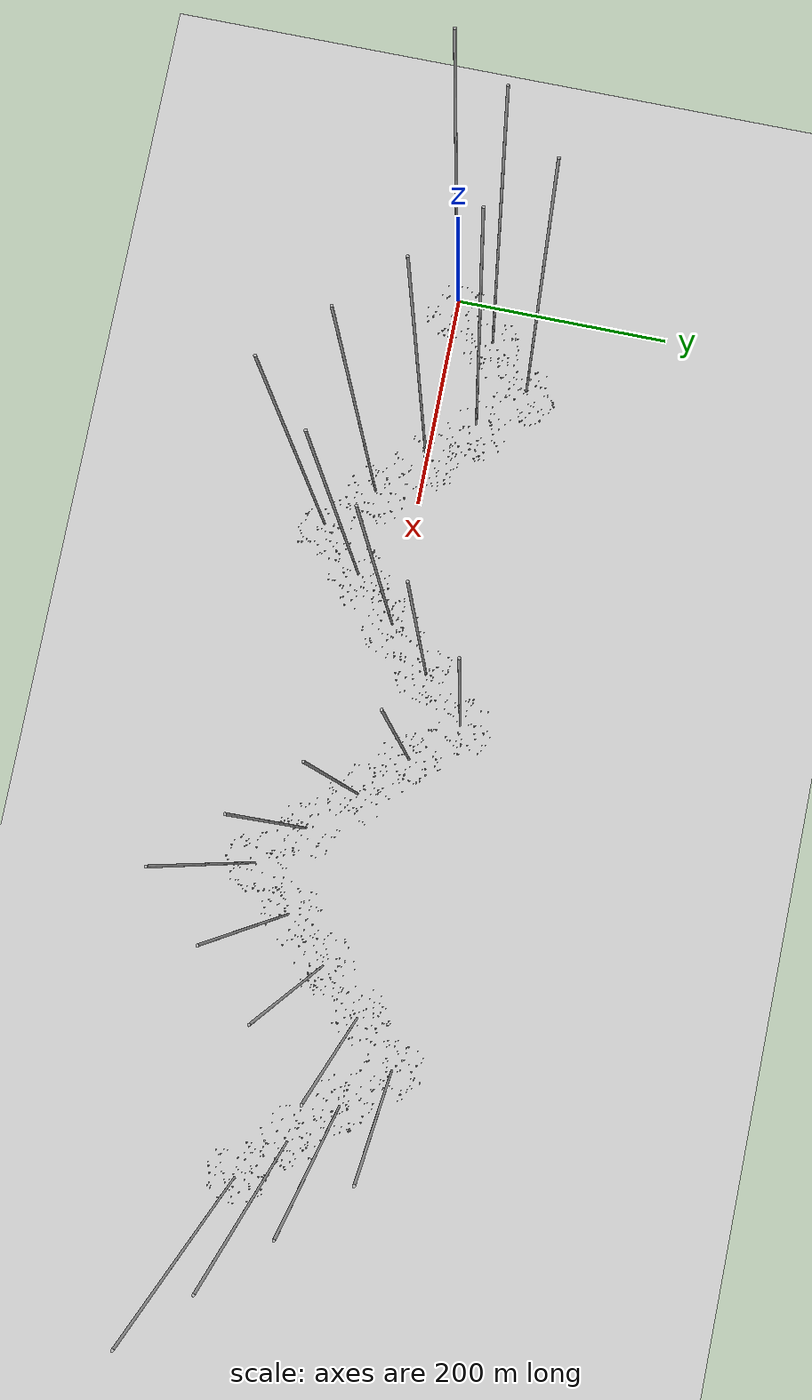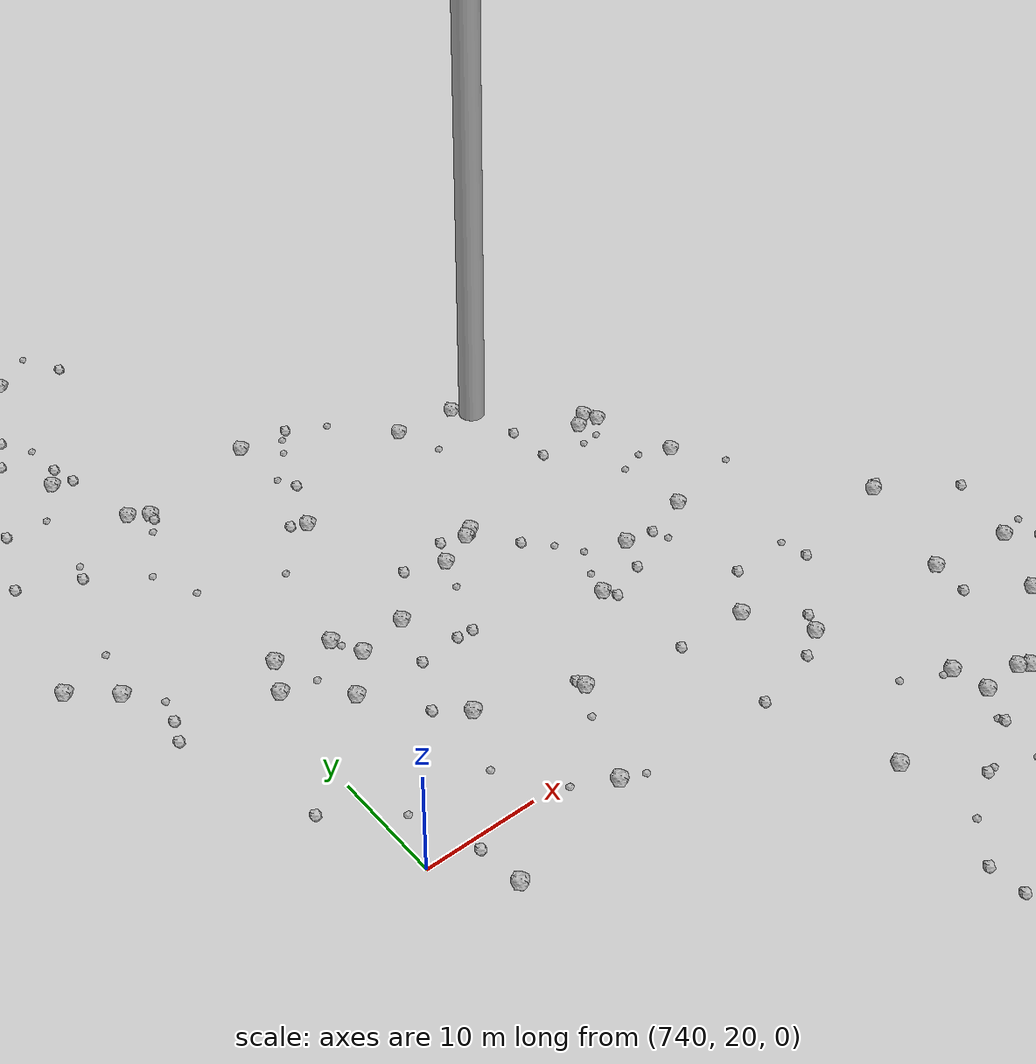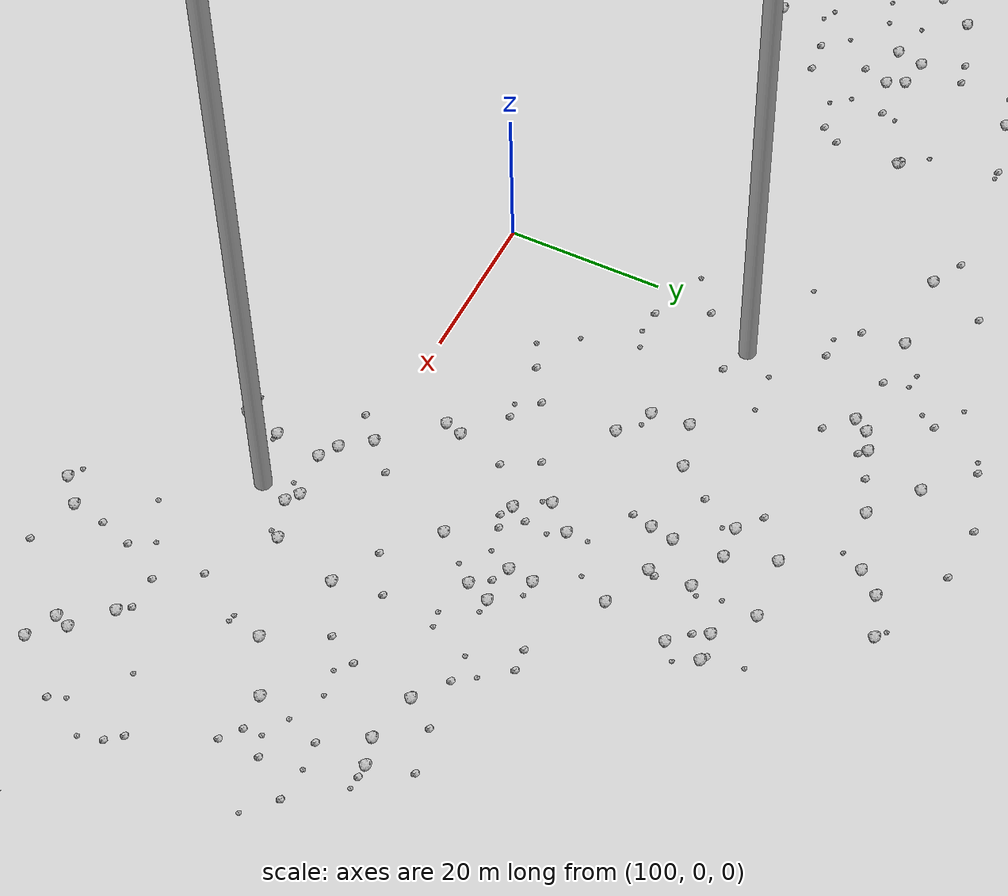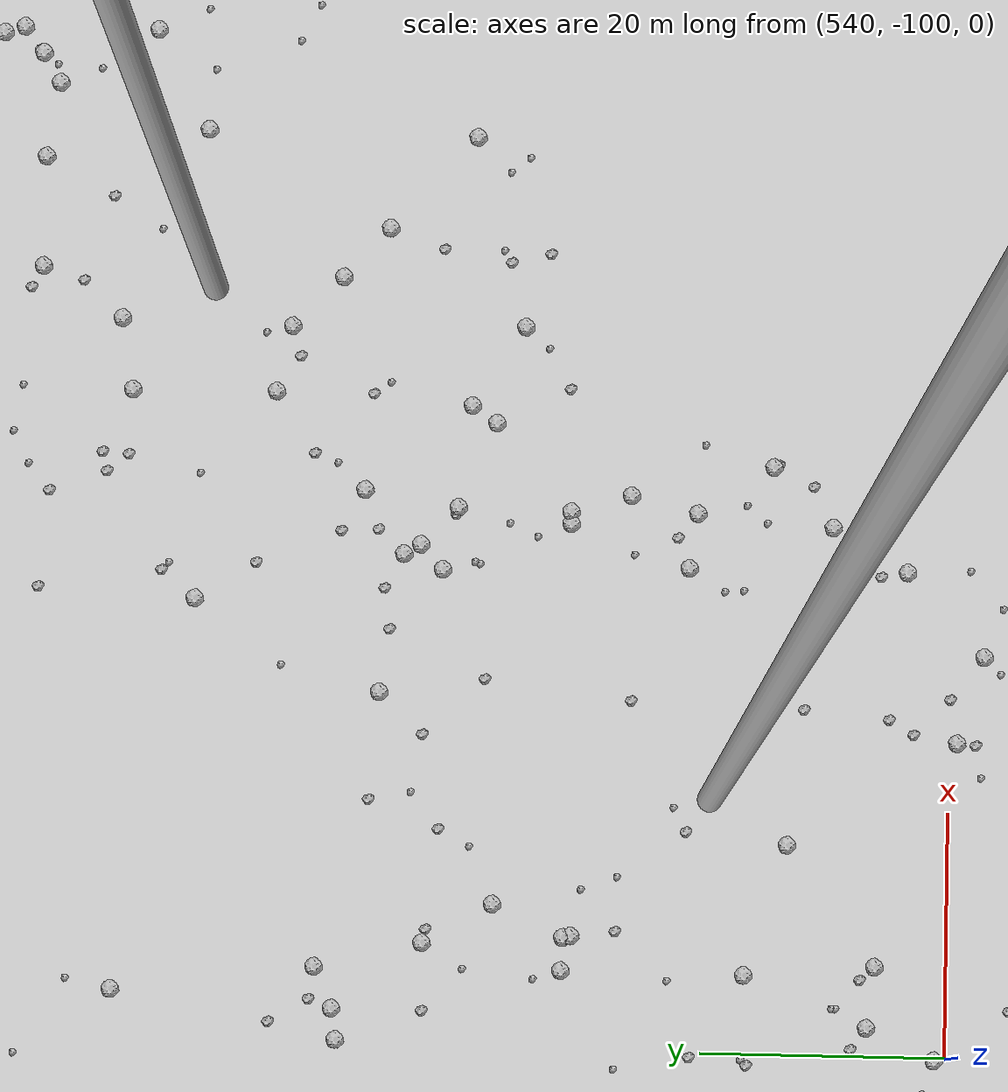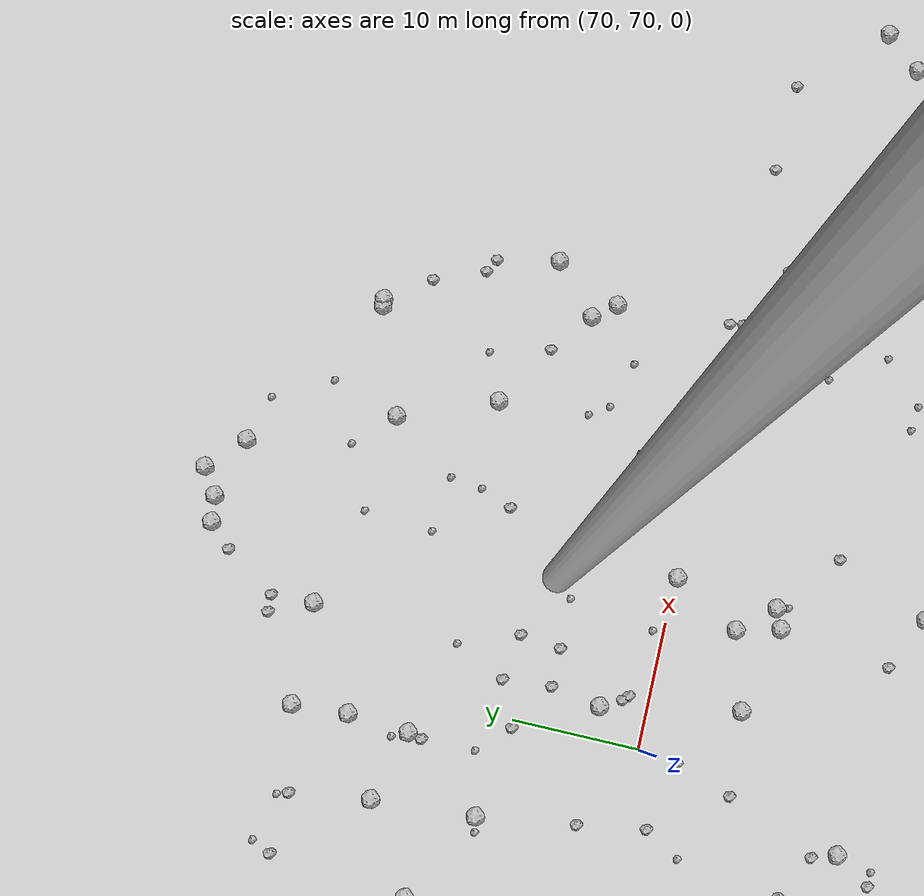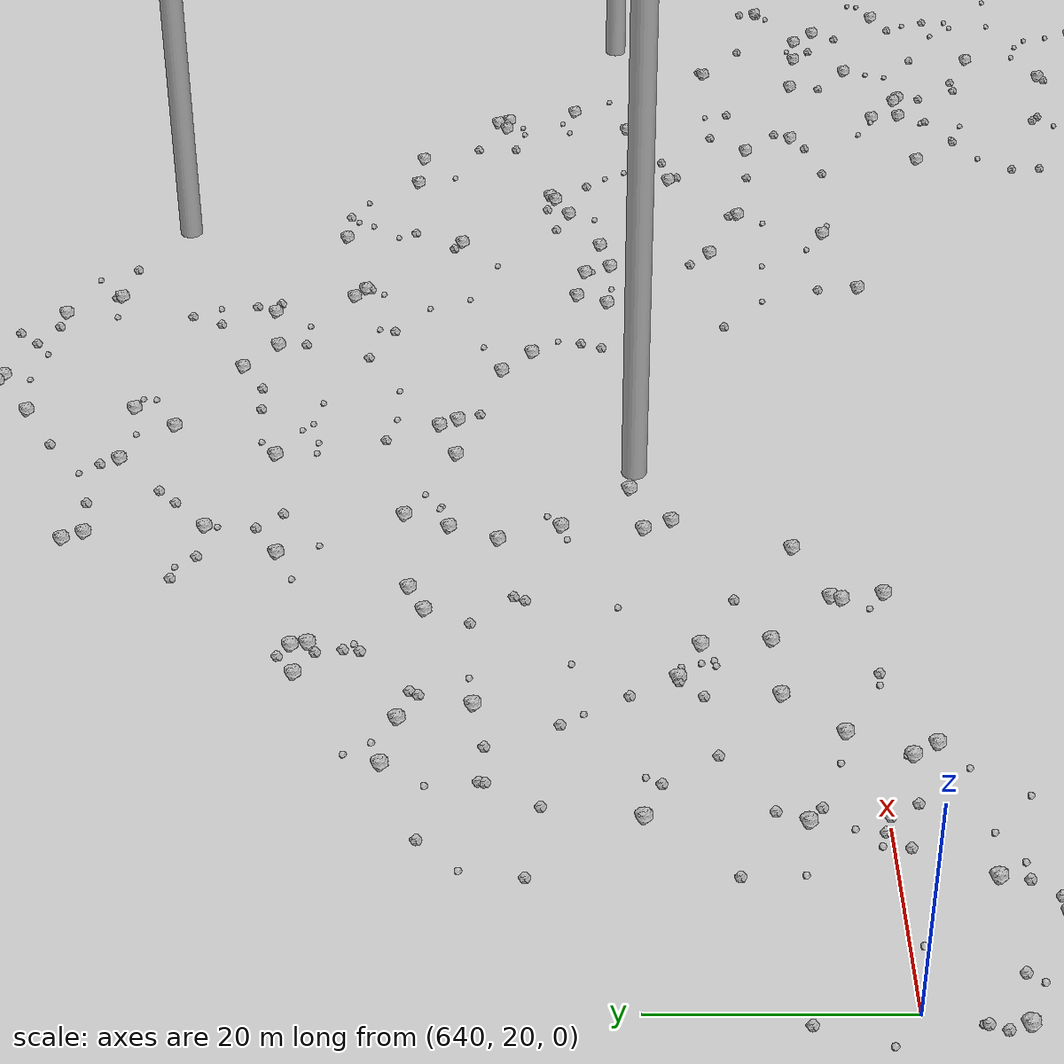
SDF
<sdf version="1.6">
 <world name="default">
  <include><uri>model://custom_ground</uri></include>
  <include><uri>model://sun</uri></include>
  <spherical_coordinates>
   <surface_model>EARTH_WGS84</surface_model>
   <latitude_deg>38.161479</latitude_deg>
   <longitude_deg>-122.454630</longitude_deg>
   <elevation>488.0</elevation>
   <heading_deg>90</heading_deg>
  </spherical_coordinates>
  <model name="rock1_0_0">
   <include><uri>model://rock1</uri><pose>28.89240392083375 -8.251447731566753 0.5 0 0 0</pose></include>
  </model>
  <model name="rock1_0_1">
   <include><uri>model://rock1</uri><pose>18.333153108932514 -20.960449020984612 0.5 0 0 0</pose></include>
  </model>
  <model name="rock1_0_2">
   <include><uri>model://rock1</uri><pose>17.022024644259425 23.800266063380334 0.5 0 0 0</pose></include>
  </model>
  <model name="rock1_0_3">
   <include><uri>model://rock1</uri><pose>29.38433361707314 18.501102311695064 0.5 0 0 0</pose></include>
  </model>
  <model name="rock1_0_4">
   <include><uri>model://rock1</uri><pose>19.326604578691985 25.033752919439166 0.5 0 0 0</pose></include>
  </model>
  <model name="rock1_0_5">
   <include><uri>model://rock1</uri><pose>-3.1407914971887223 -16.56047609525828 0.5 0 0 0</pose></include>
  </model>
  <model name="rock1_0_6">
   <include><uri>model://rock1</uri><pose>19.86674102789823 -21.36015892106568 0.5 0 0 0</pose></include>
  </model>
  <model name="rock1_0_7">
   <include><uri>model://rock1</uri><pose>-2.700845417194831 -9.88931580267041 0.5 0 0 0</pose></include>
  </model>
  <model name="rock1_0_8">
   <include><uri>model://rock1</uri><pose>-6.497884018358031 15.437609809167583 0.5 0 0 0</pose></include>
  </model>
  <model name="rock1_0_9">
   <include><uri>model://rock1</uri><pose>34.67840982071247 -13.114436952716463 0.5 0 0 0</pose></include>
  </model>
  <model name="rock1_0_10">
   <include><uri>model://rock1</uri><pose>15.447593478588331 -3.743261380759858 0.5 0 0 0</pose></include>
  </model>
  <model name="rock1_0_11">
   <include><uri>model://rock1</uri><pose>-0.28258649102653877 25.167961833343142 0.5 0 0 0</pose></include>
  </model>
  <model name="rock1_0_12">
   <include><uri>model://rock1</uri><pose>34.45447410510062 -2.0537355409042988 0.5 0 0 0</pose></include>
  </model>
  <model name="rock1_0_13">
   <include><uri>model://rock1</uri><pose>20.30266414823428 -26.571973026416323 0.5 0 0 0</pose></include>
  </model>
  <model name="rock1_0_14">
   <include><uri>model://rock1</uri><pose>-16.97392508465335 -4.047671610643334 0.5 0 0 0</pose></include>
  </model>
  <model name="rock1_0_15">
   <include><uri>model://rock1</uri><pose>14.491756993398496 -19.566163134854406 0.5 0 0 0</pose></include>
  </model>
  <model name="rock1_0_16">
   <include><uri>model://rock1</uri><pose>2.7217477200584703 24.63396864026503 0.5 0 0 0</pose></include>
  </model>
  <model name="rock1_0_17">
   <include><uri>model://rock1</uri><pose>12.129768885750295 9.42615907365986 0.5 0 0 0</pose></include>
  </model>
  <model name="rock1_0_18">
   <include><uri>model://rock1</uri><pose>24.926836774869983 13.4840445658933 0.5 0 0 0</pose></include>
  </model>
  <model name="rock1_0_19">
   <include><uri>model://rock1</uri><pose>-8.696860265631896 15.921592069049773 0.5 0 0 0</pose></include>
  </model>
  <model name="rock1_0_20">
   <include><uri>model://rock1</uri><pose>36.014163062972536 -3.0344764649587006 0.5 0 0 0</pose></include>
  </model>
  <model name="rock1_0_21">
   <include><uri>model://rock1</uri><pose>-0.7539746536106193 -12.106559816765763 0.5 0 0 0</pose></include>
  </model>
  <model name="rock1_0_22">
   <include><uri>model://rock1</uri><pose>13.017379124603337 1.2558204348869424 0.5 0 0 0</pose></include>
  </model>
  <model name="rock1_0_23">
   <include><uri>model://rock1</uri><pose>25.060243162056018 -25.09816957348127 0.5 0 0 0</pose></include>
  </model>
  <model name="rock1_0_24">
   <include><uri>model://rock1</uri><pose>29.295695108332524 -4.860907637939285 0.5 0 0 0</pose></include>
  </model>
  <model name="rock1_0_25">
   <include><uri>model://rock1</uri><pose>35.4312558306436 -7.5737950770414635 0.5 0 0 0</pose></include>
  </model>
  <model name="rock1_0_26">
   <include><uri>model://rock1</uri><pose>31.52013118284993 -9.97571056577885 0.5 0 0 0</pose></include>
  </model>
  <model name="rock2_0_0">
   <include><uri>model://rock2</uri><pose>8.409959702267084 10.918069295889346 0.3 0 0 0</pose></include>
  </model>
  <model name="rock2_0_1">
   <include><uri>model://rock2</uri><pose>35.14969078021123 3.975860039475613 0.3 0 0 0</pose></include>
  </model>
  <model name="rock2_0_2">
   <include><uri>model://rock2</uri><pose>-1.960616778971513 -10.810829314552226 0.3 0 0 0</pose></include>
  </model>
  <model name="rock2_0_3">
   <include><uri>model://rock2</uri><pose>28.351196417164523 7.47921141878728 0.3 0 0 0</pose></include>
  </model>
  <model name="rock2_0_4">
   <include><uri>model://rock2</uri><pose>-6.102040384242283 19.111430416964126 0.3 0 0 0</pose></include>
  </model>
  <model name="rock2_0_5">
   <include><uri>model://rock2</uri><pose>2.3744347944534 24.43150588320926 0.3 0 0 0</pose></include>
  </model>
  <model name="rock2_0_6">
   <include><uri>model://rock2</uri><pose>-4.542118787471484 -1.5167994713348385 0.3 0 0 0</pose></include>
  </model>
  <model name="rock2_0_7">
   <include><uri>model://rock2</uri><pose>9.40862786658062 -28.19272667543725 0.3 0 0 0</pose></include>
  </model>
  <model name="rock2_0_8">
   <include><uri>model://rock2</uri><pose>-10.920725779491994 10.058387045284519 0.3 0 0 0</pose></include>
  </model>
  <model name="rock2_0_9">
   <include><uri>model://rock2</uri><pose>11.198918185272216 -27.41175250977727 0.3 0 0 0</pose></include>
  </model>
  <model name="rock2_0_10">
   <include><uri>model://rock2</uri><pose>10.327713301319534 22.691897663526248 0.3 0 0 0</pose></include>
  </model>
  <model name="rock2_0_11">
   <include><uri>model://rock2</uri><pose>30.74784058399571 -9.09734260081217 0.3 0 0 0</pose></include>
  </model>
  <model name="rock2_0_12">
   <include><uri>model://rock2</uri><pose>29.867684540975304 -5.171842518455531 0.3 0 0 0</pose></include>
  </model>
  <model name="rock2_0_13">
   <include><uri>model://rock2</uri><pose>-14.360636923557397 0.4701424707148121 0.3 0 0 0</pose></include>
  </model>
  <model name="rock2_0_14">
   <include><uri>model://rock2</uri><pose>-13.45409045693451 -5.114570419450445 0.3 0 0 0</pose></include>
  </model>
  <model name="rock2_0_15">
   <include><uri>model://rock2</uri><pose>9.045677435270278 -18.793463533521688 0.3 0 0 0</pose></include>
  </model>
  <model name="rock2_0_16">
   <include><uri>model://rock2</uri><pose>-12.914720982900556 -12.33305118149245 0.3 0 0 0</pose></include>
  </model>
  <model name="rock2_0_17">
   <include><uri>model://rock2</uri><pose>3.1084470378243303 13.224786001444528 0.3 0 0 0</pose></include>
  </model>
  <model name="rock2_0_18">
   <include><uri>model://rock2</uri><pose>24.261189980939704 -2.002891777150392 0.3 0 0 0</pose></include>
  </model>
  <model name="rock2_0_19">
   <include><uri>model://rock2</uri><pose>16.515281659768 7.740035690139223 0.3 0 0 0</pose></include>
  </model>
  <model name="rock2_0_20">
   <include><uri>model://rock2</uri><pose>34.54586810599174 1.7447299285427427 0.3 0 0 0</pose></include>
  </model>
  <model name="rock2_0_21">
   <include><uri>model://rock2</uri><pose>-7.545576729439398 14.651509908258376 0.3 0 0 0</pose></include>
  </model>
  <model name="rock2_0_22">
   <include><uri>model://rock2</uri><pose>0.779039584692029 27.12819401540351 0.3 0 0 0</pose></include>
  </model>
  <model name="rock2_0_23">
   <include><uri>model://rock2</uri><pose>16.609082960867347 12.395080816714554 0.3 0 0 0</pose></include>
  </model>
  <model name="rock2_0_24">
   <include><uri>model://rock2</uri><pose>10.720433107522627 20.35250552904194 0.3 0 0 0</pose></include>
  </model>
  <model name="rock2_0_25">
   <include><uri>model://rock2</uri><pose>-14.707978662268781 5.105948463225779 0.3 0 0 0</pose></include>
  </model>
  <model name="rock2_0_26">
   <include><uri>model://rock2</uri><pose>18.624748010595646 24.349917835232553 0.3 0 0 0</pose></include>
  </model>
  <model name="rock3_0_0">
   <include><uri>model://rock3</uri><pose>22.584412775605216 19.09904786732416 0.2 0 0 0</pose></include>
  </model>
  <model name="rock3_0_1">
   <include><uri>model://rock3</uri><pose>-11.964555022475984 11.314814774267596 0.2 0 0 0</pose></include>
  </model>
  <model name="rock3_0_2">
   <include><uri>model://rock3</uri><pose>20.150697175165867 -11.311699165311605 0.2 0 0 0</pose></include>
  </model>
  <model name="rock3_0_3">
   <include><uri>model://rock3</uri><pose>33.25648947279714 18.815399294576217 0.2 0 0 0</pose></include>
  </model>
  <model name="rock3_0_4">
   <include><uri>model://rock3</uri><pose>-1.2023072090230542 4.285320998275424 0.2 0 0 0</pose></include>
  </model>
  <model name="rock3_0_5">
   <include><uri>model://rock3</uri><pose>28.95426515427488 -20.167820984281967 0.2 0 0 0</pose></include>
  </model>
  <model name="rock3_0_6">
   <include><uri>model://rock3</uri><pose>30.303013770773305 17.652845378268438 0.2 0 0 0</pose></include>
  </model>
  <model name="rock3_0_7">
   <include><uri>model://rock3</uri><pose>5.086083339752555 3.595791327668721 0.2 0 0 0</pose></include>
  </model>
  <model name="rock3_0_8">
   <include><uri>model://rock3</uri><pose>29.15838537394974 -13.259127037681047 0.2 0 0 0</pose></include>
  </model>
  <model name="rock3_0_9">
   <include><uri>model://rock3</uri><pose>-7.258523308717663 16.68728238266823 0.2 0 0 0</pose></include>
  </model>
  <model name="rock3_0_10">
   <include><uri>model://rock3</uri><pose>-12.668555007447814 -3.5240330340313157 0.2 0 0 0</pose></include>
  </model>
  <model name="rock3_0_11">
   <include><uri>model://rock3</uri><pose>-10.552995782800538 21.77438462699262 0.2 0 0 0</pose></include>
  </model>
  <model name="rock3_0_12">
   <include><uri>model://rock3</uri><pose>-6.250157231097678 -8.183455661477936 0.2 0 0 0</pose></include>
  </model>
  <model name="rock3_0_13">
   <include><uri>model://rock3</uri><pose>23.734350517495344 -4.384664573870591 0.2 0 0 0</pose></include>
  </model>
  <model name="rock3_0_14">
   <include><uri>model://rock3</uri><pose>21.67240039788473 7.511155154727305 0.2 0 0 0</pose></include>
  </model>
  <model name="rock3_0_15">
   <include><uri>model://rock3</uri><pose>-18.123738546656032 2.7919277395501183 0.2 0 0 0</pose></include>
  </model>
  <model name="rock3_0_16">
   <include><uri>model://rock3</uri><pose>22.584898632630207 -25.86249637134692 0.2 0 0 0</pose></include>
  </model>
  <model name="rock3_0_17">
   <include><uri>model://rock3</uri><pose>22.760274033461492 1.6839861645748826 0.2 0 0 0</pose></include>
  </model>
  <model name="rock3_0_18">
   <include><uri>model://rock3</uri><pose>-4.5785814678518815 -0.1847350532120977 0.2 0 0 0</pose></include>
  </model>
  <model name="rock3_0_19">
   <include><uri>model://rock3</uri><pose>25.651967150089185 -2.6405832558425786 0.2 0 0 0</pose></include>
  </model>
  <model name="rock3_0_20">
   <include><uri>model://rock3</uri><pose>-0.456775596524853 24.52393498544867 0.2 0 0 0</pose></include>
  </model>
  <model name="rock3_0_21">
   <include><uri>model://rock3</uri><pose>-14.526933887550888 0.1813356277921514 0.2 0 0 0</pose></include>
  </model>
  <model name="rock3_0_22">
   <include><uri>model://rock3</uri><pose>30.941990347896457 -0.03137270624051425 0.2 0 0 0</pose></include>
  </model>
  <model name="rock3_0_23">
   <include><uri>model://rock3</uri><pose>15.90900095178474 -15.492508611072404 0.2 0 0 0</pose></include>
  </model>
  <model name="rock3_0_24">
   <include><uri>model://rock3</uri><pose>1.506223609219738 4.998026528823424 0.2 0 0 0</pose></include>
  </model>
  <model name="rock3_0_25">
   <include><uri>model://rock3</uri><pose>-1.3940470131903453 4.245154569884917 0.2 0 0 0</pose></include>
  </model>
  <model name="rock3_0_26">
   <include><uri>model://rock3</uri><pose>-1.0170293580611798 -6.853460614778392 0.2 0 0 0</pose></include>
  </model>
  <model name="rock1_1_0">
   <include><uri>model://rock1</uri><pose>45.529506549643806 56.28721111853187 0.5 0 0 0</pose></include>
  </model>
  <model name="rock1_1_1">
   <include><uri>model://rock1</uri><pose>54.613909823670824 49.83888413295888 0.5 0 0 0</pose></include>
  </model>
  <model name="rock1_1_2">
   <include><uri>model://rock1</uri><pose>55.97729311889212 48.95196897918549 0.5 0 0 0</pose></include>
  </model>
  <model name="rock1_1_3">
   <include><uri>model://rock1</uri><pose>68.16594940751514 39.1350495784458 0.5 0 0 0</pose></include>
  </model>
  <model name="rock1_1_4">
   <include><uri>model://rock1</uri><pose>40.63116280127295 24.244760764973034 0.5 0 0 0</pose></include>
  </model>
  <model name="rock1_1_5">
   <include><uri>model://rock1</uri><pose>26.972192282466864 56.7276337289845 0.5 0 0 0</pose></include>
  </model>
  <model name="rock1_1_6">
   <include><uri>model://rock1</uri><pose>48.96307789803421 14.536634413715914 0.5 0 0 0</pose></include>
  </model>
  <model name="rock1_1_7">
   <include><uri>model://rock1</uri><pose>54.63448632746546 34.39713996756566 0.5 0 0 0</pose></include>
  </model>
  <model name="rock1_1_8">
   <include><uri>model://rock1</uri><pose>68.30346623666858 38.93590654358714 0.5 0 0 0</pose></include>
  </model>
  <model name="rock1_1_9">
   <include><uri>model://rock1</uri><pose>25.901911519981642 61.92714802825954 0.5 0 0 0</pose></include>
  </model>
  <model name="rock1_1_10">
   <include><uri>model://rock1</uri><pose>55.72032117217169 32.17368438069276 0.5 0 0 0</pose></include>
  </model>
  <model name="rock1_1_11">
   <include><uri>model://rock1</uri><pose>41.10969108838943 37.77806102719444 0.5 0 0 0</pose></include>
  </model>
  <model name="rock1_1_12">
   <include><uri>model://rock1</uri><pose>11.860001687957922 36.5576457840614 0.5 0 0 0</pose></include>
  </model>
  <model name="rock1_1_13">
   <include><uri>model://rock1</uri><pose>14.070679925648475 53.96104113717268 0.5 0 0 0</pose></include>
  </model>
  <model name="rock1_1_14">
   <include><uri>model://rock1</uri><pose>35.9565193017703 14.418269068318445 0.5 0 0 0</pose></include>
  </model>
  <model name="rock1_1_15">
   <include><uri>model://rock1</uri><pose>50.57560293247972 35.02367641503567 0.5 0 0 0</pose></include>
  </model>
  <model name="rock1_1_16">
   <include><uri>model://rock1</uri><pose>43.31725731290098 52.407380289631405 0.5 0 0 0</pose></include>
  </model>
  <model name="rock1_1_17">
   <include><uri>model://rock1</uri><pose>27.075033132113518 57.142410987364855 0.5 0 0 0</pose></include>
  </model>
  <model name="rock1_1_18">
   <include><uri>model://rock1</uri><pose>23.660494062088375 46.62480724698509 0.5 0 0 0</pose></include>
  </model>
  <model name="rock1_1_19">
   <include><uri>model://rock1</uri><pose>47.8976349015978 47.57931196038874 0.5 0 0 0</pose></include>
  </model>
  <model name="rock1_1_20">
   <include><uri>model://rock1</uri><pose>39.797665807239724 45.300640143564806 0.5 0 0 0</pose></include>
  </model>
  <model name="rock1_1_21">
   <include><uri>model://rock1</uri><pose>49.8190011079511 31.50862232020105 0.5 0 0 0</pose></include>
  </model>
  <model name="rock1_1_22">
   <include><uri>model://rock1</uri><pose>65.73581418628014 53.7491117533225 0.5 0 0 0</pose></include>
  </model>
  <model name="rock1_1_23">
   <include><uri>model://rock1</uri><pose>14.684862207092273 47.42428761538706 0.5 0 0 0</pose></include>
  </model>
  <model name="rock1_1_24">
   <include><uri>model://rock1</uri><pose>51.46806674398983 63.23017438973193 0.5 0 0 0</pose></include>
  </model>
  <model name="rock1_1_25">
   <include><uri>model://rock1</uri><pose>36.566479752743575 64.42789987983994 0.5 0 0 0</pose></include>
  </model>
  <model name="rock1_1_26">
   <include><uri>model://rock1</uri><pose>37.96602556233796 33.11512737118205 0.5 0 0 0</pose></include>
  </model>
  <model name="rock2_1_0">
   <include><uri>model://rock2</uri><pose>49.9380096541299 56.79587979694267 0.3 0 0 0</pose></include>
  </model>
  <model name="rock2_1_1">
   <include><uri>model://rock2</uri><pose>49.30016822787644 51.343850526108795 0.3 0 0 0</pose></include>
  </model>
  <model name="rock2_1_2">
   <include><uri>model://rock2</uri><pose>48.193916239465906 40.29894402625854 0.3 0 0 0</pose></include>
  </model>
  <model name="rock2_1_3">
   <include><uri>model://rock2</uri><pose>30.469319252890767 26.353998910938124 0.3 0 0 0</pose></include>
  </model>
  <model name="rock2_1_4">
   <include><uri>model://rock2</uri><pose>35.002380326832494 22.15154496874469 0.3 0 0 0</pose></include>
  </model>
  <model name="rock2_1_5">
   <include><uri>model://rock2</uri><pose>51.15523813042322 47.79239454536256 0.3 0 0 0</pose></include>
  </model>
  <model name="rock2_1_6">
   <include><uri>model://rock2</uri><pose>68.16188031595077 30.461002421183984 0.3 0 0 0</pose></include>
  </model>
  <model name="rock2_1_7">
   <include><uri>model://rock2</uri><pose>51.26612909233347 40.96237403549901 0.3 0 0 0</pose></include>
  </model>
  <model name="rock2_1_8">
   <include><uri>model://rock2</uri><pose>57.37493067634884 22.380801546601294 0.3 0 0 0</pose></include>
  </model>
  <model name="rock2_1_9">
   <include><uri>model://rock2</uri><pose>25.806163571171247 56.27723071474136 0.3 0 0 0</pose></include>
  </model>
  <model name="rock2_1_10">
   <include><uri>model://rock2</uri><pose>52.246715729249125 57.63739984744751 0.3 0 0 0</pose></include>
  </model>
  <model name="rock2_1_11">
   <include><uri>model://rock2</uri><pose>65.0864467226991 55.5823491878299 0.3 0 0 0</pose></include>
  </model>
  <model name="rock2_1_12">
   <include><uri>model://rock2</uri><pose>26.708067577027478 60.22706807499837 0.3 0 0 0</pose></include>
  </model>
  <model name="rock2_1_13">
   <include><uri>model://rock2</uri><pose>33.07104883185852 25.970229384041453 0.3 0 0 0</pose></include>
  </model>
  <model name="rock2_1_14">
   <include><uri>model://rock2</uri><pose>66.42159067873678 28.066070582908587 0.3 0 0 0</pose></include>
  </model>
  <model name="rock2_1_15">
   <include><uri>model://rock2</uri><pose>41.374060249340175 63.54706518257704 0.3 0 0 0</pose></include>
  </model>
  <model name="rock2_1_16">
   <include><uri>model://rock2</uri><pose>37.77145121888504 19.787067334119207 0.3 0 0 0</pose></include>
  </model>
  <model name="rock2_1_17">
   <include><uri>model://rock2</uri><pose>53.02244190982797 21.821391516116044 0.3 0 0 0</pose></include>
  </model>
  <model name="rock2_1_18">
   <include><uri>model://rock2</uri><pose>60.79307051409306 33.79566862647984 0.3 0 0 0</pose></include>
  </model>
  <model name="rock2_1_19">
   <include><uri>model://rock2</uri><pose>30.314680858635725 13.016028496470998 0.3 0 0 0</pose></include>
  </model>
  <model name="rock2_1_20">
   <include><uri>model://rock2</uri><pose>32.321633381227315 62.890674102289395 0.3 0 0 0</pose></include>
  </model>
  <model name="rock2_1_21">
   <include><uri>model://rock2</uri><pose>32.545713080327694 62.75757312161636 0.3 0 0 0</pose></include>
  </model>
  <model name="rock2_1_22">
   <include><uri>model://rock2</uri><pose>23.605758761818503 21.005697523689044 0.3 0 0 0</pose></include>
  </model>
  <model name="rock2_1_23">
   <include><uri>model://rock2</uri><pose>29.316889043816683 49.5678828133955 0.3 0 0 0</pose></include>
  </model>
  <model name="rock2_1_24">
   <include><uri>model://rock2</uri><pose>63.9166585674995 51.013047596055166 0.3 0 0 0</pose></include>
  </model>
  <model name="rock2_1_25">
   <include><uri>model://rock2</uri><pose>18.238112391316065 49.39947021465071 0.3 0 0 0</pose></include>
  </model>
  <model name="rock2_1_26">
   <include><uri>model://rock2</uri><pose>54.392442198649704 28.746845618854 0.3 0 0 0</pose></include>
  </model>
  <model name="rock3_1_0">
   <include><uri>model://rock3</uri><pose>30.025169468656262 44.905923346288155 0.2 0 0 0</pose></include>
  </model>
  <model name="rock3_1_1">
   <include><uri>model://rock3</uri><pose>61.9492319199155 26.827829595724616 0.2 0 0 0</pose></include>
  </model>
  <model name="rock3_1_2">
   <include><uri>model://rock3</uri><pose>64.99279932472403 50.908854410504816 0.2 0 0 0</pose></include>
  </model>
  <model name="rock3_1_3">
   <include><uri>model://rock3</uri><pose>13.044589696443314 29.9185873422323 0.2 0 0 0</pose></include>
  </model>
  <model name="rock3_1_4">
   <include><uri>model://rock3</uri><pose>55.20192827887964 48.77259560328943 0.2 0 0 0</pose></include>
  </model>
  <model name="rock3_1_5">
   <include><uri>model://rock3</uri><pose>21.216702595573985 58.86559307542946 0.2 0 0 0</pose></include>
  </model>
  <model name="rock3_1_6">
   <include><uri>model://rock3</uri><pose>25.408631453011 59.92656633962214 0.2 0 0 0</pose></include>
  </model>
  <model name="rock3_1_7">
   <include><uri>model://rock3</uri><pose>45.02240401275132 28.283618990909535 0.2 0 0 0</pose></include>
  </model>
  <model name="rock3_1_8">
   <include><uri>model://rock3</uri><pose>32.024760540003506 57.29926534296239 0.2 0 0 0</pose></include>
  </model>
  <model name="rock3_1_9">
   <include><uri>model://rock3</uri><pose>56.65646438837306 58.44508560842131 0.2 0 0 0</pose></include>
  </model>
  <model name="rock3_1_10">
   <include><uri>model://rock3</uri><pose>21.572472937454283 60.37207005596815 0.2 0 0 0</pose></include>
  </model>
  <model name="rock3_1_11">
   <include><uri>model://rock3</uri><pose>46.71590217986205 47.934286207283854 0.2 0 0 0</pose></include>
  </model>
  <model name="rock3_1_12">
   <include><uri>model://rock3</uri><pose>23.35194993460246 63.099971098891125 0.2 0 0 0</pose></include>
  </model>
  <model name="rock3_1_13">
   <include><uri>model://rock3</uri><pose>17.003855545905743 30.576186083167453 0.2 0 0 0</pose></include>
  </model>
  <model name="rock3_1_14">
   <include><uri>model://rock3</uri><pose>44.371618943466345 32.613074108738644 0.2 0 0 0</pose></include>
  </model>
  <model name="rock3_1_15">
   <include><uri>model://rock3</uri><pose>46.29685083101763 20.932052913717328 0.2 0 0 0</pose></include>
  </model>
  <model name="rock3_1_16">
   <include><uri>model://rock3</uri><pose>65.47911705470489 42.20572030648042 0.2 0 0 0</pose></include>
  </model>
  <model name="rock3_1_17">
   <include><uri>model://rock3</uri><pose>19.483353491919523 41.48960822573687 0.2 0 0 0</pose></include>
  </model>
  <model name="rock3_1_18">
   <include><uri>model://rock3</uri><pose>61.211998540973326 35.647490246472245 0.2 0 0 0</pose></include>
  </model>
  <model name="rock3_1_19">
   <include><uri>model://rock3</uri><pose>41.34593738435292 27.1996037471565 0.2 0 0 0</pose></include>
  </model>
  <model name="rock3_1_20">
   <include><uri>model://rock3</uri><pose>29.77384300762924 47.75260006008047 0.2 0 0 0</pose></include>
  </model>
  <model name="rock3_1_21">
   <include><uri>model://rock3</uri><pose>50.20654323875451 24.805035149138934 0.2 0 0 0</pose></include>
  </model>
  <model name="rock3_1_22">
   <include><uri>model://rock3</uri><pose>48.07090421938081 20.09135629233607 0.2 0 0 0</pose></include>
  </model>
  <model name="rock3_1_23">
   <include><uri>model://rock3</uri><pose>53.30236265957678 15.703297942665284 0.2 0 0 0</pose></include>
  </model>
  <model name="rock3_1_24">
   <include><uri>model://rock3</uri><pose>60.10248993074224 29.14172529379282 0.2 0 0 0</pose></include>
  </model>
  <model name="rock3_1_25">
   <include><uri>model://rock3</uri><pose>45.421797095311305 65.51978651147407 0.2 0 0 0</pose></include>
  </model>
  <model name="rock3_1_26">
   <include><uri>model://rock3</uri><pose>31.22946605833555 36.30106154911563 0.2 0 0 0</pose></include>
  </model>
  <model name="rock1_2_0">
   <include><uri>model://rock1</uri><pose>72.61331213319659 73.71802394677316 0.5 0 0 0</pose></include>
  </model>
  <model name="rock1_2_1">
   <include><uri>model://rock1</uri><pose>99.6961007342606 97.32512683002555 0.5 0 0 0</pose></include>
  </model>
  <model name="rock1_2_2">
   <include><uri>model://rock1</uri><pose>55.28299541464318 85.07945459166885 0.5 0 0 0</pose></include>
  </model>
  <model name="rock1_2_3">
   <include><uri>model://rock1</uri><pose>80.71818204910383 64.63786619972721 0.5 0 0 0</pose></include>
  </model>
  <model name="rock1_2_4">
   <include><uri>model://rock1</uri><pose>86.7354189460731 105.30894029687614 0.5 0 0 0</pose></include>
  </model>
  <model name="rock1_2_5">
   <include><uri>model://rock1</uri><pose>83.91850380536661 108.00605133471078 0.5 0 0 0</pose></include>
  </model>
  <model name="rock1_2_6">
   <include><uri>model://rock1</uri><pose>91.22958082915997 94.18456313549648 0.5 0 0 0</pose></include>
  </model>
  <model name="rock1_2_7">
   <include><uri>model://rock1</uri><pose>67.37619173780826 87.65154531745176 0.5 0 0 0</pose></include>
  </model>
  <model name="rock1_2_8">
   <include><uri>model://rock1</uri><pose>83.07253093619522 61.88434947149142 0.5 0 0 0</pose></include>
  </model>
  <model name="rock1_2_9">
   <include><uri>model://rock1</uri><pose>61.831638402272404 89.28484267007524 0.5 0 0 0</pose></include>
  </model>
  <model name="rock1_2_10">
   <include><uri>model://rock1</uri><pose>79.79122933467238 106.41181148758008 0.5 0 0 0</pose></include>
  </model>
  <model name="rock1_2_11">
   <include><uri>model://rock1</uri><pose>67.74115433485028 92.49756026463218 0.5 0 0 0</pose></include>
  </model>
  <model name="rock1_2_12">
   <include><uri>model://rock1</uri><pose>74.70575554777133 62.97806157023956 0.5 0 0 0</pose></include>
  </model>
  <model name="rock1_2_13">
   <include><uri>model://rock1</uri><pose>81.56289977348487 61.260923650990705 0.5 0 0 0</pose></include>
  </model>
  <model name="rock1_2_14">
   <include><uri>model://rock1</uri><pose>106.46592376584613 84.32631798590657 0.5 0 0 0</pose></include>
  </model>
  <model name="rock1_2_15">
   <include><uri>model://rock1</uri><pose>75.41631090030478 97.0895922222112 0.5 0 0 0</pose></include>
  </model>
  <model name="rock1_2_16">
   <include><uri>model://rock1</uri><pose>53.69872552304352 86.96175306188483 0.5 0 0 0</pose></include>
  </model>
  <model name="rock1_2_17">
   <include><uri>model://rock1</uri><pose>100.26896521315527 97.380589273827 0.5 0 0 0</pose></include>
  </model>
  <model name="rock1_2_18">
   <include><uri>model://rock1</uri><pose>81.85044208542232 106.68602464419155 0.5 0 0 0</pose></include>
  </model>
  <model name="rock1_2_19">
   <include><uri>model://rock1</uri><pose>102.54910352196445 80.84192982915305 0.5 0 0 0</pose></include>
  </model>
  <model name="rock1_2_20">
   <include><uri>model://rock1</uri><pose>94.2130687120177 86.56341497154368 0.5 0 0 0</pose></include>
  </model>
  <model name="rock1_2_21">
   <include><uri>model://rock1</uri><pose>83.67165206744183 69.87899920424996 0.5 0 0 0</pose></include>
  </model>
  <model name="rock1_2_22">
   <include><uri>model://rock1</uri><pose>62.36462293764227 81.19983477791034 0.5 0 0 0</pose></include>
  </model>
  <model name="rock1_2_23">
   <include><uri>model://rock1</uri><pose>67.46623500557507 96.91096702469447 0.5 0 0 0</pose></include>
  </model>
  <model name="rock1_2_24">
   <include><uri>model://rock1</uri><pose>57.21143455194293 67.60404933589123 0.5 0 0 0</pose></include>
  </model>
  <model name="rock1_2_25">
   <include><uri>model://rock1</uri><pose>84.76484121004691 50.44436366127534 0.5 0 0 0</pose></include>
  </model>
  <model name="rock1_2_26">
   <include><uri>model://rock1</uri><pose>103.96911641756829 79.02684316999942 0.5 0 0 0</pose></include>
  </model>
  <model name="rock2_2_0">
   <include><uri>model://rock2</uri><pose>73.46830637592288 72.08806866481655 0.3 0 0 0</pose></include>
  </model>
  <model name="rock2_2_1">
   <include><uri>model://rock2</uri><pose>76.24918785922105 77.60935677467845 0.3 0 0 0</pose></include>
  </model>
  <model name="rock2_2_2">
   <include><uri>model://rock2</uri><pose>104.67631201868755 68.87583560029641 0.3 0 0 0</pose></include>
  </model>
  <model name="rock2_2_3">
   <include><uri>model://rock2</uri><pose>53.82002502690375 74.48951720057487 0.3 0 0 0</pose></include>
  </model>
  <model name="rock2_2_4">
   <include><uri>model://rock2</uri><pose>73.88000330174177 71.65451372252159 0.3 0 0 0</pose></include>
  </model>
  <model name="rock2_2_5">
   <include><uri>model://rock2</uri><pose>60.87182629600103 95.56463564552797 0.3 0 0 0</pose></include>
  </model>
  <model name="rock2_2_6">
   <include><uri>model://rock2</uri><pose>80.52832181669015 52.496033832620775 0.3 0 0 0</pose></include>
  </model>
  <model name="rock2_2_7">
   <include><uri>model://rock2</uri><pose>87.90303412183653 57.75879657223888 0.3 0 0 0</pose></include>
  </model>
  <model name="rock2_2_8">
   <include><uri>model://rock2</uri><pose>75.2752531489334 100.515745533769 0.3 0 0 0</pose></include>
  </model>
  <model name="rock2_2_9">
   <include><uri>model://rock2</uri><pose>63.45575729536114 73.54100302216918 0.3 0 0 0</pose></include>
  </model>
  <model name="rock2_2_10">
   <include><uri>model://rock2</uri><pose>72.93130904247431 81.46896910498575 0.3 0 0 0</pose></include>
  </model>
  <model name="rock2_2_11">
   <include><uri>model://rock2</uri><pose>104.32856190966837 89.86890256887523 0.3 0 0 0</pose></include>
  </model>
  <model name="rock2_2_12">
   <include><uri>model://rock2</uri><pose>105.45498908255273 89.26672682272203 0.3 0 0 0</pose></include>
  </model>
  <model name="rock2_2_13">
   <include><uri>model://rock2</uri><pose>102.71038335922262 93.90986637046676 0.3 0 0 0</pose></include>
  </model>
  <model name="rock2_2_14">
   <include><uri>model://rock2</uri><pose>73.92840846165538 100.43090276499527 0.3 0 0 0</pose></include>
  </model>
  <model name="rock2_2_15">
   <include><uri>model://rock2</uri><pose>77.97383993653857 104.63161316790571 0.3 0 0 0</pose></include>
  </model>
  <model name="rock2_2_16">
   <include><uri>model://rock2</uri><pose>76.60296788664229 80.83402485173262 0.3 0 0 0</pose></include>
  </model>
  <model name="rock2_2_17">
   <include><uri>model://rock2</uri><pose>64.31430140077335 68.25530540158353 0.3 0 0 0</pose></include>
  </model>
  <model name="rock2_2_18">
   <include><uri>model://rock2</uri><pose>86.10932675572417 83.81198097638647 0.3 0 0 0</pose></include>
  </model>
  <model name="rock2_2_19">
   <include><uri>model://rock2</uri><pose>61.60733825446736 57.48767346280826 0.3 0 0 0</pose></include>
  </model>
  <model name="rock2_2_20">
   <include><uri>model://rock2</uri><pose>104.49129784120632 69.94080953900729 0.3 0 0 0</pose></include>
  </model>
  <model name="rock2_2_21">
   <include><uri>model://rock2</uri><pose>73.2383396797967 77.63580846860276 0.3 0 0 0</pose></include>
  </model>
  <model name="rock2_2_22">
   <include><uri>model://rock2</uri><pose>68.16384756423307 62.54521524562881 0.3 0 0 0</pose></include>
  </model>
  <model name="rock2_2_23">
   <include><uri>model://rock2</uri><pose>67.08679435923034 86.55897898958077 0.3 0 0 0</pose></include>
  </model>
  <model name="rock2_2_24">
   <include><uri>model://rock2</uri><pose>69.4797307049206 79.95341154080643 0.3 0 0 0</pose></include>
  </model>
  <model name="rock2_2_25">
   <include><uri>model://rock2</uri><pose>99.22495398721037 83.42317606592809 0.3 0 0 0</pose></include>
  </model>
  <model name="rock2_2_26">
   <include><uri>model://rock2</uri><pose>56.13140381804823 95.86987676049232 0.3 0 0 0</pose></include>
  </model>
  <model name="rock3_2_0">
   <include><uri>model://rock3</uri><pose>88.26049559640018 97.16389399578371 0.2 0 0 0</pose></include>
  </model>
  <model name="rock3_2_1">
   <include><uri>model://rock3</uri><pose>94.74422768367161 79.36471195286808 0.2 0 0 0</pose></include>
  </model>
  <model name="rock3_2_2">
   <include><uri>model://rock3</uri><pose>87.08378689316056 86.3117907940809 0.2 0 0 0</pose></include>
  </model>
  <model name="rock3_2_3">
   <include><uri>model://rock3</uri><pose>79.18154851500499 70.86378760480001 0.2 0 0 0</pose></include>
  </model>
  <model name="rock3_2_4">
   <include><uri>model://rock3</uri><pose>92.92424123038923 99.68123366574963 0.2 0 0 0</pose></include>
  </model>
  <model name="rock3_2_5">
   <include><uri>model://rock3</uri><pose>54.47912892412467 83.80547794681345 0.2 0 0 0</pose></include>
  </model>
  <model name="rock3_2_6">
   <include><uri>model://rock3</uri><pose>83.27474334651627 60.89732988541811 0.2 0 0 0</pose></include>
  </model>
  <model name="rock3_2_7">
   <include><uri>model://rock3</uri><pose>92.59524286382515 74.66075421065025 0.2 0 0 0</pose></include>
  </model>
  <model name="rock3_2_8">
   <include><uri>model://rock3</uri><pose>53.77372692832303 70.14948478332578 0.2 0 0 0</pose></include>
  </model>
  <model name="rock3_2_9">
   <include><uri>model://rock3</uri><pose>74.79735874078762 85.48321907100879 0.2 0 0 0</pose></include>
  </model>
  <model name="rock3_2_10">
   <include><uri>model://rock3</uri><pose>101.78156071157687 61.28131989145783 0.2 0 0 0</pose></include>
  </model>
  <model name="rock3_2_11">
   <include><uri>model://rock3</uri><pose>56.52983196969827 75.86875955523887 0.2 0 0 0</pose></include>
  </model>
  <model name="rock3_2_12">
   <include><uri>model://rock3</uri><pose>56.79075604644125 97.37482156963915 0.2 0 0 0</pose></include>
  </model>
  <model name="rock3_2_13">
   <include><uri>model://rock3</uri><pose>66.7379896826037 88.83768675323714 0.2 0 0 0</pose></include>
  </model>
  <model name="rock3_2_14">
   <include><uri>model://rock3</uri><pose>99.54658778327548 76.6669526191128 0.2 0 0 0</pose></include>
  </model>
  <model name="rock3_2_15">
   <include><uri>model://rock3</uri><pose>69.70400946164537 66.77937440245336 0.2 0 0 0</pose></include>
  </model>
  <model name="rock3_2_16">
   <include><uri>model://rock3</uri><pose>83.30822689099334 94.9157803024103 0.2 0 0 0</pose></include>
  </model>
  <model name="rock3_2_17">
   <include><uri>model://rock3</uri><pose>60.53265131062508 96.4146430587578 0.2 0 0 0</pose></include>
  </model>
  <model name="rock3_2_18">
   <include><uri>model://rock3</uri><pose>61.13193738588737 80.95544827963587 0.2 0 0 0</pose></include>
  </model>
  <model name="rock3_2_19">
   <include><uri>model://rock3</uri><pose>62.646028245294396 65.46015189203696 0.2 0 0 0</pose></include>
  </model>
  <model name="rock3_2_20">
   <include><uri>model://rock3</uri><pose>95.7363639234028 77.83286625077116 0.2 0 0 0</pose></include>
  </model>
  <model name="rock3_2_21">
   <include><uri>model://rock3</uri><pose>97.94151445695655 88.15087656621995 0.2 0 0 0</pose></include>
  </model>
  <model name="rock3_2_22">
   <include><uri>model://rock3</uri><pose>82.91997226347488 89.37560126186898 0.2 0 0 0</pose></include>
  </model>
  <model name="rock3_2_23">
   <include><uri>model://rock3</uri><pose>87.4096553305435 88.87828397292498 0.2 0 0 0</pose></include>
  </model>
  <model name="rock3_2_24">
   <include><uri>model://rock3</uri><pose>90.49203834962506 104.25801330862626 0.2 0 0 0</pose></include>
  </model>
  <model name="rock3_2_25">
   <include><uri>model://rock3</uri><pose>80.17282995009677 77.63483688134103 0.2 0 0 0</pose></include>
  </model>
  <model name="rock3_2_26">
   <include><uri>model://rock3</uri><pose>67.131793170938 82.30153470942125 0.2 0 0 0</pose></include>
  </model>
  <model name="rock1_3_0">
   <include><uri>model://rock1</uri><pose>108.80662824045389 50.111438081155185 0.5 0 0 0</pose></include>
  </model>
  <model name="rock1_3_1">
   <include><uri>model://rock1</uri><pose>122.99205263528006 25.197192229195068 0.5 0 0 0</pose></include>
  </model>
  <model name="rock1_3_2">
   <include><uri>model://rock1</uri><pose>129.79817904492617 43.845676857379544 0.5 0 0 0</pose></include>
  </model>
  <model name="rock1_3_3">
   <include><uri>model://rock1</uri><pose>112.54393208113504 53.28549539645225 0.5 0 0 0</pose></include>
  </model>
  <model name="rock1_3_4">
   <include><uri>model://rock1</uri><pose>128.75120550778075 59.21189547092178 0.5 0 0 0</pose></include>
  </model>
  <model name="rock1_3_5">
   <include><uri>model://rock1</uri><pose>121.0482303779793 56.58330891565361 0.5 0 0 0</pose></include>
  </model>
  <model name="rock1_3_6">
   <include><uri>model://rock1</uri><pose>124.24114352646635 34.58211577408957 0.5 0 0 0</pose></include>
  </model>
  <model name="rock1_3_7">
   <include><uri>model://rock1</uri><pose>133.8290097382995 34.9410826551633 0.5 0 0 0</pose></include>
  </model>
  <model name="rock1_3_8">
   <include><uri>model://rock1</uri><pose>134.0282140911654 44.20530265706267 0.5 0 0 0</pose></include>
  </model>
  <model name="rock1_3_9">
   <include><uri>model://rock1</uri><pose>138.8747267048367 26.487306043443596 0.5 0 0 0</pose></include>
  </model>
  <model name="rock1_3_10">
   <include><uri>model://rock1</uri><pose>139.33456316737013 42.60297002057236 0.5 0 0 0</pose></include>
  </model>
  <model name="rock1_3_11">
   <include><uri>model://rock1</uri><pose>131.31112847180862 62.07675940558771 0.5 0 0 0</pose></include>
  </model>
  <model name="rock1_3_12">
   <include><uri>model://rock1</uri><pose>118.74837331196746 27.848382878798354 0.5 0 0 0</pose></include>
  </model>
  <model name="rock1_3_13">
   <include><uri>model://rock1</uri><pose>95.44301683116309 51.024023843910406 0.5 0 0 0</pose></include>
  </model>
  <model name="rock1_3_14">
   <include><uri>model://rock1</uri><pose>109.95788590901124 51.99782325439227 0.5 0 0 0</pose></include>
  </model>
  <model name="rock1_3_15">
   <include><uri>model://rock1</uri><pose>147.56859334803363 43.091060787323364 0.5 0 0 0</pose></include>
  </model>
  <model name="rock1_3_16">
   <include><uri>model://rock1</uri><pose>115.17349568070235 61.0847029732825 0.5 0 0 0</pose></include>
  </model>
  <model name="rock1_3_17">
   <include><uri>model://rock1</uri><pose>136.6462360829753 64.10920665542434 0.5 0 0 0</pose></include>
  </model>
  <model name="rock1_3_18">
   <include><uri>model://rock1</uri><pose>145.6676896088197 34.71553034164701 0.5 0 0 0</pose></include>
  </model>
  <model name="rock1_3_19">
   <include><uri>model://rock1</uri><pose>139.85187653713268 51.02661059107139 0.5 0 0 0</pose></include>
  </model>
  <model name="rock1_3_20">
   <include><uri>model://rock1</uri><pose>118.28064368088712 32.70083179848915 0.5 0 0 0</pose></include>
  </model>
  <model name="rock1_3_21">
   <include><uri>model://rock1</uri><pose>139.47015476287766 37.241691150531985 0.5 0 0 0</pose></include>
  </model>
  <model name="rock1_3_22">
   <include><uri>model://rock1</uri><pose>135.80865164185258 23.097759248634087 0.5 0 0 0</pose></include>
  </model>
  <model name="rock1_3_23">
   <include><uri>model://rock1</uri><pose>131.78880032777352 50.14605351804956 0.5 0 0 0</pose></include>
  </model>
  <model name="rock1_3_24">
   <include><uri>model://rock1</uri><pose>134.37971837563927 37.942038218075204 0.5 0 0 0</pose></include>
  </model>
  <model name="rock1_3_25">
   <include><uri>model://rock1</uri><pose>148.10313874678758 47.69960722148642 0.5 0 0 0</pose></include>
  </model>
  <model name="rock1_3_26">
   <include><uri>model://rock1</uri><pose>144.3875091634601 47.302661905564584 0.5 0 0 0</pose></include>
  </model>
  <model name="rock2_3_0">
   <include><uri>model://rock2</uri><pose>109.7964232575375 66.16119024148637 0.3 0 0 0</pose></include>
  </model>
  <model name="rock2_3_1">
   <include><uri>model://rock2</uri><pose>116.35898048433087 54.58748096843134 0.3 0 0 0</pose></include>
  </model>
  <model name="rock2_3_2">
   <include><uri>model://rock2</uri><pose>126.73514412816293 46.18709592425218 0.3 0 0 0</pose></include>
  </model>
  <model name="rock2_3_3">
   <include><uri>model://rock2</uri><pose>95.99769343728701 45.60843068408325 0.3 0 0 0</pose></include>
  </model>
  <model name="rock2_3_4">
   <include><uri>model://rock2</uri><pose>101.2308995636642 27.857431628998935 0.3 0 0 0</pose></include>
  </model>
  <model name="rock2_3_5">
   <include><uri>model://rock2</uri><pose>108.59637850435827 32.76438415349672 0.3 0 0 0</pose></include>
  </model>
  <model name="rock2_3_6">
   <include><uri>model://rock2</uri><pose>125.22378075271769 68.5432804810927 0.3 0 0 0</pose></include>
  </model>
  <model name="rock2_3_7">
   <include><uri>model://rock2</uri><pose>104.30567734155878 21.668766004806486 0.3 0 0 0</pose></include>
  </model>
  <model name="rock2_3_8">
   <include><uri>model://rock2</uri><pose>118.33337297534783 12.377401328735928 0.3 0 0 0</pose></include>
  </model>
  <model name="rock2_3_9">
   <include><uri>model://rock2</uri><pose>111.67794765930785 47.0574611888858 0.3 0 0 0</pose></include>
  </model>
  <model name="rock2_3_10">
   <include><uri>model://rock2</uri><pose>102.0528764025861 50.940195188105704 0.3 0 0 0</pose></include>
  </model>
  <model name="rock2_3_11">
   <include><uri>model://rock2</uri><pose>122.88897956072066 15.339064050899736 0.3 0 0 0</pose></include>
  </model>
  <model name="rock2_3_12">
   <include><uri>model://rock2</uri><pose>139.85302590064305 38.21653589906279 0.3 0 0 0</pose></include>
  </model>
  <model name="rock2_3_13">
   <include><uri>model://rock2</uri><pose>101.21505351895367 43.130244107946055 0.3 0 0 0</pose></include>
  </model>
  <model name="rock2_3_14">
   <include><uri>model://rock2</uri><pose>105.71736540797157 59.03859882799063 0.3 0 0 0</pose></include>
  </model>
  <model name="rock2_3_15">
   <include><uri>model://rock2</uri><pose>133.0312900505744 32.2890684480606 0.3 0 0 0</pose></include>
  </model>
  <model name="rock2_3_16">
   <include><uri>model://rock2</uri><pose>127.28997859584547 38.88057653817788 0.3 0 0 0</pose></include>
  </model>
  <model name="rock2_3_17">
   <include><uri>model://rock2</uri><pose>130.89003787597363 19.31704285317693 0.3 0 0 0</pose></include>
  </model>
  <model name="rock2_3_18">
   <include><uri>model://rock2</uri><pose>112.1428584374701 53.15893812121608 0.3 0 0 0</pose></include>
  </model>
  <model name="rock2_3_19">
   <include><uri>model://rock2</uri><pose>126.45152752215712 12.899450785692675 0.3 0 0 0</pose></include>
  </model>
  <model name="rock2_3_20">
   <include><uri>model://rock2</uri><pose>133.3286567804288 15.030557340064572 0.3 0 0 0</pose></include>
  </model>
  <model name="rock2_3_21">
   <include><uri>model://rock2</uri><pose>139.85792196644 18.38934519908731 0.3 0 0 0</pose></include>
  </model>
  <model name="rock2_3_22">
   <include><uri>model://rock2</uri><pose>145.154699423973 45.42607009518599 0.3 0 0 0</pose></include>
  </model>
  <model name="rock2_3_23">
   <include><uri>model://rock2</uri><pose>113.28080945058056 52.37270850680565 0.3 0 0 0</pose></include>
  </model>
  <model name="rock2_3_24">
   <include><uri>model://rock2</uri><pose>147.3232956933577 48.13140279587342 0.3 0 0 0</pose></include>
  </model>
  <model name="rock2_3_25">
   <include><uri>model://rock2</uri><pose>117.88082852116631 68.86277289551589 0.3 0 0 0</pose></include>
  </model>
  <model name="rock2_3_26">
   <include><uri>model://rock2</uri><pose>139.4613711698618 21.45992270682814 0.3 0 0 0</pose></include>
  </model>
  <model name="rock3_3_0">
   <include><uri>model://rock3</uri><pose>111.78745714997015 15.11759112902633 0.2 0 0 0</pose></include>
  </model>
  <model name="rock3_3_1">
   <include><uri>model://rock3</uri><pose>146.74502730973848 52.56346484588902 0.2 0 0 0</pose></include>
  </model>
  <model name="rock3_3_2">
   <include><uri>model://rock3</uri><pose>104.51929315484405 56.98270372966831 0.2 0 0 0</pose></include>
  </model>
  <model name="rock3_3_3">
   <include><uri>model://rock3</uri><pose>138.7550609453255 29.126536202052865 0.2 0 0 0</pose></include>
  </model>
  <model name="rock3_3_4">
   <include><uri>model://rock3</uri><pose>124.42081129903076 12.466430694241 0.2 0 0 0</pose></include>
  </model>
  <model name="rock3_3_5">
   <include><uri>model://rock3</uri><pose>139.87871612136155 24.38867918071098 0.2 0 0 0</pose></include>
  </model>
  <model name="rock3_3_6">
   <include><uri>model://rock3</uri><pose>139.45421825299496 46.50416788199797 0.2 0 0 0</pose></include>
  </model>
  <model name="rock3_3_7">
   <include><uri>model://rock3</uri><pose>107.22957475548121 38.148983502331674 0.2 0 0 0</pose></include>
  </model>
  <model name="rock3_3_8">
   <include><uri>model://rock3</uri><pose>135.90045783063604 21.888098397884143 0.2 0 0 0</pose></include>
  </model>
  <model name="rock3_3_9">
   <include><uri>model://rock3</uri><pose>135.2349330683759 65.0547324352087 0.2 0 0 0</pose></include>
  </model>
  <model name="rock3_3_10">
   <include><uri>model://rock3</uri><pose>95.66323729277207 51.01835841957768 0.2 0 0 0</pose></include>
  </model>
  <model name="rock3_3_11">
   <include><uri>model://rock3</uri><pose>114.84373214155696 10.61841049627132 0.2 0 0 0</pose></include>
  </model>
  <model name="rock3_3_12">
   <include><uri>model://rock3</uri><pose>127.23129407433957 56.331245578287096 0.2 0 0 0</pose></include>
  </model>
  <model name="rock3_3_13">
   <include><uri>model://rock3</uri><pose>101.22491626686556 53.935723920170716 0.2 0 0 0</pose></include>
  </model>
  <model name="rock3_3_14">
   <include><uri>model://rock3</uri><pose>96.57994920868339 24.319364388403645 0.2 0 0 0</pose></include>
  </model>
  <model name="rock3_3_15">
   <include><uri>model://rock3</uri><pose>107.4053664549302 21.34659486249516 0.2 0 0 0</pose></include>
  </model>
  <model name="rock3_3_16">
   <include><uri>model://rock3</uri><pose>120.54403590941621 27.446146105187786 0.2 0 0 0</pose></include>
  </model>
  <model name="rock3_3_17">
   <include><uri>model://rock3</uri><pose>92.38575264817659 37.68022006624935 0.2 0 0 0</pose></include>
  </model>
  <model name="rock3_3_18">
   <include><uri>model://rock3</uri><pose>130.11621915919034 42.340348915999876 0.2 0 0 0</pose></include>
  </model>
  <model name="rock3_3_19">
   <include><uri>model://rock3</uri><pose>108.22187512048411 65.56709146473523 0.2 0 0 0</pose></include>
  </model>
  <model name="rock3_3_20">
   <include><uri>model://rock3</uri><pose>112.54035773869316 38.7056108753839 0.2 0 0 0</pose></include>
  </model>
  <model name="rock3_3_21">
   <include><uri>model://rock3</uri><pose>140.13888351670653 43.57794801814681 0.2 0 0 0</pose></include>
  </model>
  <model name="rock3_3_22">
   <include><uri>model://rock3</uri><pose>109.84599852074004 22.204809560129494 0.2 0 0 0</pose></include>
  </model>
  <model name="rock3_3_23">
   <include><uri>model://rock3</uri><pose>143.4642410853295 30.648087726975547 0.2 0 0 0</pose></include>
  </model>
  <model name="rock3_3_24">
   <include><uri>model://rock3</uri><pose>98.41376245370472 42.89190617000753 0.2 0 0 0</pose></include>
  </model>
  <model name="rock3_3_25">
   <include><uri>model://rock3</uri><pose>99.24397353575377 54.149090649647015 0.2 0 0 0</pose></include>
  </model>
  <model name="rock3_3_26">
   <include><uri>model://rock3</uri><pose>149.44342938027359 44.84615532687626 0.2 0 0 0</pose></include>
  </model>
  <model name="rock1_4_0">
   <include><uri>model://rock1</uri><pose>141.79436258450386 -4.752194442903001 0.5 0 0 0</pose></include>
  </model>
  <model name="rock1_4_1">
   <include><uri>model://rock1</uri><pose>173.28516209093237 19.48120858333018 0.5 0 0 0</pose></include>
  </model>
  <model name="rock1_4_2">
   <include><uri>model://rock1</uri><pose>175.44486376630158 -18.501612034647422 0.5 0 0 0</pose></include>
  </model>
  <model name="rock1_4_3">
   <include><uri>model://rock1</uri><pose>150.20382533223 19.5284390477974 0.5 0 0 0</pose></include>
  </model>
  <model name="rock1_4_4">
   <include><uri>model://rock1</uri><pose>154.24395595245744 -3.217446124546669 0.5 0 0 0</pose></include>
  </model>
  <model name="rock1_4_5">
   <include><uri>model://rock1</uri><pose>173.9919000933789 5.677781961815782 0.5 0 0 0</pose></include>
  </model>
  <model name="rock1_4_6">
   <include><uri>model://rock1</uri><pose>157.34492995404565 -29.740510856194547 0.5 0 0 0</pose></include>
  </model>
  <model name="rock1_4_7">
   <include><uri>model://rock1</uri><pose>151.34595522499143 22.52751767376359 0.5 0 0 0</pose></include>
  </model>
  <model name="rock1_4_8">
   <include><uri>model://rock1</uri><pose>171.1493201924034 -14.722947811592649 0.5 0 0 0</pose></include>
  </model>
  <model name="rock1_4_9">
   <include><uri>model://rock1</uri><pose>166.82973843979403 20.901776822136767 0.5 0 0 0</pose></include>
  </model>
  <model name="rock1_4_10">
   <include><uri>model://rock1</uri><pose>167.10828084361708 1.6490158716435168 0.5 0 0 0</pose></include>
  </model>
  <model name="rock1_4_11">
   <include><uri>model://rock1</uri><pose>146.41629859669666 22.79414948002203 0.5 0 0 0</pose></include>
  </model>
  <model name="rock1_4_12">
   <include><uri>model://rock1</uri><pose>156.86909758141275 5.32952571115117 0.5 0 0 0</pose></include>
  </model>
  <model name="rock1_4_13">
   <include><uri>model://rock1</uri><pose>138.33541993851964 19.231941633807175 0.5 0 0 0</pose></include>
  </model>
  <model name="rock1_4_14">
   <include><uri>model://rock1</uri><pose>130.8219027012826 6.571943656760453 0.5 0 0 0</pose></include>
  </model>
  <model name="rock1_4_15">
   <include><uri>model://rock1</uri><pose>136.87922100403026 0.09101325411002748 0.5 0 0 0</pose></include>
  </model>
  <model name="rock1_4_16">
   <include><uri>model://rock1</uri><pose>149.21240049127874 -5.115773308641884 0.5 0 0 0</pose></include>
  </model>
  <model name="rock1_4_17">
   <include><uri>model://rock1</uri><pose>131.50390843859392 8.822605663041053 0.5 0 0 0</pose></include>
  </model>
  <model name="rock1_4_18">
   <include><uri>model://rock1</uri><pose>147.64468290806536 -3.984948387348396 0.5 0 0 0</pose></include>
  </model>
  <model name="rock1_4_19">
   <include><uri>model://rock1</uri><pose>174.777059612085 -20.42582892699248 0.5 0 0 0</pose></include>
  </model>
  <model name="rock1_4_20">
   <include><uri>model://rock1</uri><pose>160.4702541816197 -26.930228913218826 0.5 0 0 0</pose></include>
  </model>
  <model name="rock1_4_21">
   <include><uri>model://rock1</uri><pose>146.8188691693681 26.024597823866777 0.5 0 0 0</pose></include>
  </model>
  <model name="rock1_4_22">
   <include><uri>model://rock1</uri><pose>139.51226110562618 -3.3248185702015363 0.5 0 0 0</pose></include>
  </model>
  <model name="rock1_4_23">
   <include><uri>model://rock1</uri><pose>145.0714473566234 13.676458564570368 0.5 0 0 0</pose></include>
  </model>
  <model name="rock1_4_24">
   <include><uri>model://rock1</uri><pose>139.65254659202057 -15.620697448049786 0.5 0 0 0</pose></include>
  </model>
  <model name="rock1_4_25">
   <include><uri>model://rock1</uri><pose>176.7098855553174 20.492040994203045 0.5 0 0 0</pose></include>
  </model>
  <model name="rock1_4_26">
   <include><uri>model://rock1</uri><pose>141.04719999229692 -10.764122396638665 0.5 0 0 0</pose></include>
  </model>
  <model name="rock2_4_0">
   <include><uri>model://rock2</uri><pose>166.81551425494578 -28.962436069100384 0.3 0 0 0</pose></include>
  </model>
  <model name="rock2_4_1">
   <include><uri>model://rock2</uri><pose>162.75903214608724 23.851494657934055 0.3 0 0 0</pose></include>
  </model>
  <model name="rock2_4_2">
   <include><uri>model://rock2</uri><pose>176.47458128506113 14.13831521182015 0.3 0 0 0</pose></include>
  </model>
  <model name="rock2_4_3">
   <include><uri>model://rock2</uri><pose>141.58128477032164 19.068919835448874 0.3 0 0 0</pose></include>
  </model>
  <model name="rock2_4_4">
   <include><uri>model://rock2</uri><pose>155.86293931501615 11.488804133300142 0.3 0 0 0</pose></include>
  </model>
  <model name="rock2_4_5">
   <include><uri>model://rock2</uri><pose>150.84527094572408 8.332087293417587 0.3 0 0 0</pose></include>
  </model>
  <model name="rock2_4_6">
   <include><uri>model://rock2</uri><pose>162.22400070002965 -8.301293393509493 0.3 0 0 0</pose></include>
  </model>
  <model name="rock2_4_7">
   <include><uri>model://rock2</uri><pose>175.11171715650437 25.871856426238622 0.3 0 0 0</pose></include>
  </model>
  <model name="rock2_4_8">
   <include><uri>model://rock2</uri><pose>140.32469767353882 3.5008629475611457 0.3 0 0 0</pose></include>
  </model>
  <model name="rock2_4_9">
   <include><uri>model://rock2</uri><pose>133.82079967771188 -2.720650618749243 0.3 0 0 0</pose></include>
  </model>
  <model name="rock2_4_10">
   <include><uri>model://rock2</uri><pose>178.41133316224762 6.07640271133161 0.3 0 0 0</pose></include>
  </model>
  <model name="rock2_4_11">
   <include><uri>model://rock2</uri><pose>180.83539163800518 9.43178371156165 0.3 0 0 0</pose></include>
  </model>
  <model name="rock2_4_12">
   <include><uri>model://rock2</uri><pose>155.45246763590217 29.333738965949102 0.3 0 0 0</pose></include>
  </model>
  <model name="rock2_4_13">
   <include><uri>model://rock2</uri><pose>169.35088043352562 24.580520483142365 0.3 0 0 0</pose></include>
  </model>
  <model name="rock2_4_14">
   <include><uri>model://rock2</uri><pose>184.96617048370206 -5.2020313713064255 0.3 0 0 0</pose></include>
  </model>
  <model name="rock2_4_15">
   <include><uri>model://rock2</uri><pose>184.44625184450067 14.223859351940938 0.3 0 0 0</pose></include>
  </model>
  <model name="rock2_4_16">
   <include><uri>model://rock2</uri><pose>165.53023597505398 -13.342829184183337 0.3 0 0 0</pose></include>
  </model>
  <model name="rock2_4_17">
   <include><uri>model://rock2</uri><pose>165.4861374934894 12.912618707675136 0.3 0 0 0</pose></include>
  </model>
  <model name="rock2_4_18">
   <include><uri>model://rock2</uri><pose>169.88314014622986 -13.392427894486794 0.3 0 0 0</pose></include>
  </model>
  <model name="rock2_4_19">
   <include><uri>model://rock2</uri><pose>186.44428148260386 -7.018040569433705 0.3 0 0 0</pose></include>
  </model>
  <model name="rock2_4_20">
   <include><uri>model://rock2</uri><pose>148.51405941773643 21.75235151908361 0.3 0 0 0</pose></include>
  </model>
  <model name="rock2_4_21">
   <include><uri>model://rock2</uri><pose>163.3565799045224 8.980182969956182 0.3 0 0 0</pose></include>
  </model>
  <model name="rock2_4_22">
   <include><uri>model://rock2</uri><pose>158.3449469618817 29.643650692916545 0.3 0 0 0</pose></include>
  </model>
  <model name="rock2_4_23">
   <include><uri>model://rock2</uri><pose>178.25875301093316 20.4723871791574 0.3 0 0 0</pose></include>
  </model>
  <model name="rock2_4_24">
   <include><uri>model://rock2</uri><pose>161.15265025370866 -22.604234279893674 0.3 0 0 0</pose></include>
  </model>
  <model name="rock2_4_25">
   <include><uri>model://rock2</uri><pose>180.7418276720923 4.269292164274347 0.3 0 0 0</pose></include>
  </model>
  <model name="rock2_4_26">
   <include><uri>model://rock2</uri><pose>162.47171445461927 -18.43787082853577 0.3 0 0 0</pose></include>
  </model>
  <model name="rock3_4_0">
   <include><uri>model://rock3</uri><pose>155.4952609993763 -18.54072300118429 0.2 0 0 0</pose></include>
  </model>
  <model name="rock3_4_1">
   <include><uri>model://rock3</uri><pose>160.81328038060826 -15.637609374551003 0.2 0 0 0</pose></include>
  </model>
  <model name="rock3_4_2">
   <include><uri>model://rock3</uri><pose>155.07790587294056 18.149706221461514 0.2 0 0 0</pose></include>
  </model>
  <model name="rock3_4_3">
   <include><uri>model://rock3</uri><pose>148.02892404790492 17.175294130152224 0.2 0 0 0</pose></include>
  </model>
  <model name="rock3_4_4">
   <include><uri>model://rock3</uri><pose>183.51346214313963 -13.696922080976822 0.2 0 0 0</pose></include>
  </model>
  <model name="rock3_4_5">
   <include><uri>model://rock3</uri><pose>177.45955460485354 -8.68404789654701 0.2 0 0 0</pose></include>
  </model>
  <model name="rock3_4_6">
   <include><uri>model://rock3</uri><pose>152.9984627137083 22.361090529623276 0.2 0 0 0</pose></include>
  </model>
  <model name="rock3_4_7">
   <include><uri>model://rock3</uri><pose>187.225939440316 -10.031792257193509 0.2 0 0 0</pose></include>
  </model>
  <model name="rock3_4_8">
   <include><uri>model://rock3</uri><pose>166.59334113957456 -2.590328566495053 0.2 0 0 0</pose></include>
  </model>
  <model name="rock3_4_9">
   <include><uri>model://rock3</uri><pose>161.0363449344734 26.180969876508442 0.2 0 0 0</pose></include>
  </model>
  <model name="rock3_4_10">
   <include><uri>model://rock3</uri><pose>157.10303323618618 18.56581370711192 0.2 0 0 0</pose></include>
  </model>
  <model name="rock3_4_11">
   <include><uri>model://rock3</uri><pose>175.0273046559389 9.963379292122 0.2 0 0 0</pose></include>
  </model>
  <model name="rock3_4_12">
   <include><uri>model://rock3</uri><pose>146.32980483300773 -5.567469868210072 0.2 0 0 0</pose></include>
  </model>
  <model name="rock3_4_13">
   <include><uri>model://rock3</uri><pose>155.48417170839772 -28.879146464066366 0.2 0 0 0</pose></include>
  </model>
  <model name="rock3_4_14">
   <include><uri>model://rock3</uri><pose>170.6117741460838 11.918551528630907 0.2 0 0 0</pose></include>
  </model>
  <model name="rock3_4_15">
   <include><uri>model://rock3</uri><pose>165.69085373702174 -2.4600721092793094 0.2 0 0 0</pose></include>
  </model>
  <model name="rock3_4_16">
   <include><uri>model://rock3</uri><pose>141.73234011057525 -10.937635200737816 0.2 0 0 0</pose></include>
  </model>
  <model name="rock3_4_17">
   <include><uri>model://rock3</uri><pose>148.78352203219237 25.837167337393375 0.2 0 0 0</pose></include>
  </model>
  <model name="rock3_4_18">
   <include><uri>model://rock3</uri><pose>167.24603695480917 11.288132244556834 0.2 0 0 0</pose></include>
  </model>
  <model name="rock3_4_19">
   <include><uri>model://rock3</uri><pose>136.8959848686918 -15.338002401447211 0.2 0 0 0</pose></include>
  </model>
  <model name="rock3_4_20">
   <include><uri>model://rock3</uri><pose>180.04057441234852 14.51061407385545 0.2 0 0 0</pose></include>
  </model>
  <model name="rock3_4_21">
   <include><uri>model://rock3</uri><pose>144.8042050142821 19.741394364302295 0.2 0 0 0</pose></include>
  </model>
  <model name="rock3_4_22">
   <include><uri>model://rock3</uri><pose>178.19832556774722 8.29541315587364 0.2 0 0 0</pose></include>
  </model>
  <model name="rock3_4_23">
   <include><uri>model://rock3</uri><pose>153.47024061767848 -4.504130947478785 0.2 0 0 0</pose></include>
  </model>
  <model name="rock3_4_24">
   <include><uri>model://rock3</uri><pose>179.84593308045396 20.319421644146075 0.2 0 0 0</pose></include>
  </model>
  <model name="rock3_4_25">
   <include><uri>model://rock3</uri><pose>159.05689452133132 23.651378657084628 0.2 0 0 0</pose></include>
  </model>
  <model name="rock3_4_26">
   <include><uri>model://rock3</uri><pose>187.86106076101268 10.925369279925107 0.2 0 0 0</pose></include>
  </model>
  <model name="rock1_5_0">
   <include><uri>model://rock1</uri><pose>181.4554924165828 -44.40637951311308 0.5 0 0 0</pose></include>
  </model>
  <model name="rock1_5_1">
   <include><uri>model://rock1</uri><pose>219.11061034394666 -42.13903830189979 0.5 0 0 0</pose></include>
  </model>
  <model name="rock1_5_2">
   <include><uri>model://rock1</uri><pose>217.14767262962016 -45.35666872403778 0.5 0 0 0</pose></include>
  </model>
  <model name="rock1_5_3">
   <include><uri>model://rock1</uri><pose>208.45794285724105 -45.85848530092528 0.5 0 0 0</pose></include>
  </model>
  <model name="rock1_5_4">
   <include><uri>model://rock1</uri><pose>217.45976023666017 -34.1568047014224 0.5 0 0 0</pose></include>
  </model>
  <model name="rock1_5_5">
   <include><uri>model://rock1</uri><pose>217.4378881766803 -50.178809972793104 0.5 0 0 0</pose></include>
  </model>
  <model name="rock1_5_6">
   <include><uri>model://rock1</uri><pose>186.62084869058893 -30.146203053566538 0.5 0 0 0</pose></include>
  </model>
  <model name="rock1_5_7">
   <include><uri>model://rock1</uri><pose>220.5045715986569 -38.50934193348529 0.5 0 0 0</pose></include>
  </model>
  <model name="rock1_5_8">
   <include><uri>model://rock1</uri><pose>207.59222780353355 -14.239207002793037 0.5 0 0 0</pose></include>
  </model>
  <model name="rock1_5_9">
   <include><uri>model://rock1</uri><pose>208.50220272350464 -50.0225926007436 0.5 0 0 0</pose></include>
  </model>
  <model name="rock1_5_10">
   <include><uri>model://rock1</uri><pose>226.77947065911627 -48.36291238755618 0.5 0 0 0</pose></include>
  </model>
  <model name="rock1_5_11">
   <include><uri>model://rock1</uri><pose>183.25997937861175 -33.454408554248005 0.5 0 0 0</pose></include>
  </model>
  <model name="rock1_5_12">
   <include><uri>model://rock1</uri><pose>185.82237217465777 -65.1993803382012 0.5 0 0 0</pose></include>
  </model>
  <model name="rock1_5_13">
   <include><uri>model://rock1</uri><pose>221.32030306334923 -53.184801910752185 0.5 0 0 0</pose></include>
  </model>
  <model name="rock1_5_14">
   <include><uri>model://rock1</uri><pose>195.49500989386533 -27.103915950077337 0.5 0 0 0</pose></include>
  </model>
  <model name="rock1_5_15">
   <include><uri>model://rock1</uri><pose>181.5973645676756 -33.34160508913811 0.5 0 0 0</pose></include>
  </model>
  <model name="rock1_5_16">
   <include><uri>model://rock1</uri><pose>178.62599895053978 -22.222266249590177 0.5 0 0 0</pose></include>
  </model>
  <model name="rock1_5_17">
   <include><uri>model://rock1</uri><pose>195.45258391088677 -67.72130416186627 0.5 0 0 0</pose></include>
  </model>
  <model name="rock1_5_18">
   <include><uri>model://rock1</uri><pose>197.51140942719928 -14.12731900055978 0.5 0 0 0</pose></include>
  </model>
  <model name="rock1_5_19">
   <include><uri>model://rock1</uri><pose>212.60394229723758 -23.253849579287632 0.5 0 0 0</pose></include>
  </model>
  <model name="rock1_5_20">
   <include><uri>model://rock1</uri><pose>187.34289273826084 -49.50249620051937 0.5 0 0 0</pose></include>
  </model>
  <model name="rock1_5_21">
   <include><uri>model://rock1</uri><pose>206.8883195359574 -67.70552633402447 0.5 0 0 0</pose></include>
  </model>
  <model name="rock1_5_22">
   <include><uri>model://rock1</uri><pose>197.8902923194021 -36.411631786592544 0.5 0 0 0</pose></include>
  </model>
  <model name="rock1_5_23">
   <include><uri>model://rock1</uri><pose>212.94753767697108 -63.80951684721172 0.5 0 0 0</pose></include>
  </model>
  <model name="rock1_5_24">
   <include><uri>model://rock1</uri><pose>224.90389946995785 -55.89497987965566 0.5 0 0 0</pose></include>
  </model>
  <model name="rock1_5_25">
   <include><uri>model://rock1</uri><pose>215.59780183837907 -28.984579717616242 0.5 0 0 0</pose></include>
  </model>
  <model name="rock1_5_26">
   <include><uri>model://rock1</uri><pose>219.23459069674996 -51.987291485803254 0.5 0 0 0</pose></include>
  </model>
  <model name="rock2_5_0">
   <include><uri>model://rock2</uri><pose>178.1570679079006 -43.13046313902778 0.3 0 0 0</pose></include>
  </model>
  <model name="rock2_5_1">
   <include><uri>model://rock2</uri><pose>184.12020474902357 -46.07421233348477 0.3 0 0 0</pose></include>
  </model>
  <model name="rock2_5_2">
   <include><uri>model://rock2</uri><pose>192.9759265831616 -43.8259706192281 0.3 0 0 0</pose></include>
  </model>
  <model name="rock2_5_3">
   <include><uri>model://rock2</uri><pose>224.5718067608409 -26.975715017060757 0.3 0 0 0</pose></include>
  </model>
  <model name="rock2_5_4">
   <include><uri>model://rock2</uri><pose>217.41979069351555 -57.94393412637494 0.3 0 0 0</pose></include>
  </model>
  <model name="rock2_5_5">
   <include><uri>model://rock2</uri><pose>207.77102166419107 -14.438808366086597 0.3 0 0 0</pose></include>
  </model>
  <model name="rock2_5_6">
   <include><uri>model://rock2</uri><pose>174.4085801754137 -54.711859597125226 0.3 0 0 0</pose></include>
  </model>
  <model name="rock2_5_7">
   <include><uri>model://rock2</uri><pose>214.34338923206468 -62.153398618879905 0.3 0 0 0</pose></include>
  </model>
  <model name="rock2_5_8">
   <include><uri>model://rock2</uri><pose>210.42440831385233 -23.307782515142748 0.3 0 0 0</pose></include>
  </model>
  <model name="rock2_5_9">
   <include><uri>model://rock2</uri><pose>211.9693910920385 -24.00874144352302 0.3 0 0 0</pose></include>
  </model>
  <model name="rock2_5_10">
   <include><uri>model://rock2</uri><pose>203.6486299563732 -27.6822959170107 0.3 0 0 0</pose></include>
  </model>
  <model name="rock2_5_11">
   <include><uri>model://rock2</uri><pose>201.45782968125627 -53.64908875816931 0.3 0 0 0</pose></include>
  </model>
  <model name="rock2_5_12">
   <include><uri>model://rock2</uri><pose>193.6046781008962 -58.920370358548816 0.3 0 0 0</pose></include>
  </model>
  <model name="rock2_5_13">
   <include><uri>model://rock2</uri><pose>223.55617048836962 -35.575832800242374 0.3 0 0 0</pose></include>
  </model>
  <model name="rock2_5_14">
   <include><uri>model://rock2</uri><pose>218.03233107271518 -19.241064505380244 0.3 0 0 0</pose></include>
  </model>
  <model name="rock2_5_15">
   <include><uri>model://rock2</uri><pose>208.44423562776387 -41.456299379975334 0.3 0 0 0</pose></include>
  </model>
  <model name="rock2_5_16">
   <include><uri>model://rock2</uri><pose>172.5461635142084 -35.46937613862617 0.3 0 0 0</pose></include>
  </model>
  <model name="rock2_5_17">
   <include><uri>model://rock2</uri><pose>219.1083681317347 -38.51199216550433 0.3 0 0 0</pose></include>
  </model>
  <model name="rock2_5_18">
   <include><uri>model://rock2</uri><pose>184.43698006719598 -15.641657280818436 0.3 0 0 0</pose></include>
  </model>
  <model name="rock2_5_19">
   <include><uri>model://rock2</uri><pose>191.45749055812962 -62.400409459711625 0.3 0 0 0</pose></include>
  </model>
  <model name="rock2_5_20">
   <include><uri>model://rock2</uri><pose>198.49654131914073 -13.60380624877672 0.3 0 0 0</pose></include>
  </model>
  <model name="rock2_5_21">
   <include><uri>model://rock2</uri><pose>216.5400760068076 -64.96032609974613 0.3 0 0 0</pose></include>
  </model>
  <model name="rock2_5_22">
   <include><uri>model://rock2</uri><pose>219.55008483257023 -32.588509360026784 0.3 0 0 0</pose></include>
  </model>
  <model name="rock2_5_23">
   <include><uri>model://rock2</uri><pose>195.38345452740293 -22.779377022548836 0.3 0 0 0</pose></include>
  </model>
  <model name="rock2_5_24">
   <include><uri>model://rock2</uri><pose>200.50709462329786 -58.82259723282252 0.3 0 0 0</pose></include>
  </model>
  <model name="rock2_5_25">
   <include><uri>model://rock2</uri><pose>175.92249890829405 -45.360707450653365 0.3 0 0 0</pose></include>
  </model>
  <model name="rock2_5_26">
   <include><uri>model://rock2</uri><pose>191.19121144294314 -33.991146538092636 0.3 0 0 0</pose></include>
  </model>
  <model name="rock3_5_0">
   <include><uri>model://rock3</uri><pose>210.4316791122104 -19.775451088695725 0.2 0 0 0</pose></include>
  </model>
  <model name="rock3_5_1">
   <include><uri>model://rock3</uri><pose>197.56688106705752 -40.15665946088251 0.2 0 0 0</pose></include>
  </model>
  <model name="rock3_5_2">
   <include><uri>model://rock3</uri><pose>172.29538107145797 -48.77562630406709 0.2 0 0 0</pose></include>
  </model>
  <model name="rock3_5_3">
   <include><uri>model://rock3</uri><pose>171.3330823311041 -42.250267715261764 0.2 0 0 0</pose></include>
  </model>
  <model name="rock3_5_4">
   <include><uri>model://rock3</uri><pose>176.43747502641313 -42.5105870827567 0.2 0 0 0</pose></include>
  </model>
  <model name="rock3_5_5">
   <include><uri>model://rock3</uri><pose>193.35880537459667 -38.47384215491573 0.2 0 0 0</pose></include>
  </model>
  <model name="rock3_5_6">
   <include><uri>model://rock3</uri><pose>219.26425684447034 -34.139395571096244 0.2 0 0 0</pose></include>
  </model>
  <model name="rock3_5_7">
   <include><uri>model://rock3</uri><pose>205.23429791652762 -18.88600150750868 0.2 0 0 0</pose></include>
  </model>
  <model name="rock3_5_8">
   <include><uri>model://rock3</uri><pose>205.9041903236984 -60.13510371648343 0.2 0 0 0</pose></include>
  </model>
  <model name="rock3_5_9">
   <include><uri>model://rock3</uri><pose>194.70943028613115 -38.692058677327864 0.2 0 0 0</pose></include>
  </model>
  <model name="rock3_5_10">
   <include><uri>model://rock3</uri><pose>208.93817334502899 -18.62707269242639 0.2 0 0 0</pose></include>
  </model>
  <model name="rock3_5_11">
   <include><uri>model://rock3</uri><pose>192.31894207115894 -20.376932669650444 0.2 0 0 0</pose></include>
  </model>
  <model name="rock3_5_12">
   <include><uri>model://rock3</uri><pose>176.16108830344785 -38.2816588384221 0.2 0 0 0</pose></include>
  </model>
  <model name="rock3_5_13">
   <include><uri>model://rock3</uri><pose>200.3212442840607 -17.525407623246224 0.2 0 0 0</pose></include>
  </model>
  <model name="rock3_5_14">
   <include><uri>model://rock3</uri><pose>202.92666013197518 -17.118256694557147 0.2 0 0 0</pose></include>
  </model>
  <model name="rock3_5_15">
   <include><uri>model://rock3</uri><pose>190.23132614345897 -46.87891453932225 0.2 0 0 0</pose></include>
  </model>
  <model name="rock3_5_16">
   <include><uri>model://rock3</uri><pose>202.01463217953793 -55.61281686172248 0.2 0 0 0</pose></include>
  </model>
  <model name="rock3_5_17">
   <include><uri>model://rock3</uri><pose>225.7844034580042 -34.23660252159051 0.2 0 0 0</pose></include>
  </model>
  <model name="rock3_5_18">
   <include><uri>model://rock3</uri><pose>222.47090026976466 -49.14010416252427 0.2 0 0 0</pose></include>
  </model>
  <model name="rock3_5_19">
   <include><uri>model://rock3</uri><pose>197.23380628871098 -50.15500752673729 0.2 0 0 0</pose></include>
  </model>
  <model name="rock3_5_20">
   <include><uri>model://rock3</uri><pose>193.45815643510483 -44.06436422336202 0.2 0 0 0</pose></include>
  </model>
  <model name="rock3_5_21">
   <include><uri>model://rock3</uri><pose>224.54022676336513 -43.0468388809858 0.2 0 0 0</pose></include>
  </model>
  <model name="rock3_5_22">
   <include><uri>model://rock3</uri><pose>182.16333319918536 -52.40589181312775 0.2 0 0 0</pose></include>
  </model>
  <model name="rock3_5_23">
   <include><uri>model://rock3</uri><pose>210.76361110801784 -57.327719311937 0.2 0 0 0</pose></include>
  </model>
  <model name="rock3_5_24">
   <include><uri>model://rock3</uri><pose>214.40448095029376 -27.050335196689225 0.2 0 0 0</pose></include>
  </model>
  <model name="rock3_5_25">
   <include><uri>model://rock3</uri><pose>222.2226768933906 -27.798565867616617 0.2 0 0 0</pose></include>
  </model>
  <model name="rock3_5_26">
   <include><uri>model://rock3</uri><pose>187.82283853378837 -34.31275417433875 0.2 0 0 0</pose></include>
  </model>
  <model name="rock1_6_0">
   <include><uri>model://rock1</uri><pose>249.9137625481759 -59.33948776507584 0.5 0 0 0</pose></include>
  </model>
  <model name="rock1_6_1">
   <include><uri>model://rock1</uri><pose>251.25428918790791 -74.3940268701777 0.5 0 0 0</pose></include>
  </model>
  <model name="rock1_6_2">
   <include><uri>model://rock1</uri><pose>257.66916532066796 -103.68467031383875 0.5 0 0 0</pose></include>
  </model>
  <model name="rock1_6_3">
   <include><uri>model://rock1</uri><pose>261.32987196526153 -77.48317043429213 0.5 0 0 0</pose></include>
  </model>
  <model name="rock1_6_4">
   <include><uri>model://rock1</uri><pose>242.72907097387244 -87.99002738498334 0.5 0 0 0</pose></include>
  </model>
  <model name="rock1_6_5">
   <include><uri>model://rock1</uri><pose>225.8707371441297 -81.36542452290885 0.5 0 0 0</pose></include>
  </model>
  <model name="rock1_6_6">
   <include><uri>model://rock1</uri><pose>255.78069854485648 -57.65505104231352 0.5 0 0 0</pose></include>
  </model>
  <model name="rock1_6_7">
   <include><uri>model://rock1</uri><pose>252.2017458337429 -100.11501772677553 0.5 0 0 0</pose></include>
  </model>
  <model name="rock1_6_8">
   <include><uri>model://rock1</uri><pose>243.08848223179703 -75.6583882238757 0.5 0 0 0</pose></include>
  </model>
  <model name="rock1_6_9">
   <include><uri>model://rock1</uri><pose>237.69282972076206 -69.19806978234107 0.5 0 0 0</pose></include>
  </model>
  <model name="rock1_6_10">
   <include><uri>model://rock1</uri><pose>229.28359349805964 -99.87245073510728 0.5 0 0 0</pose></include>
  </model>
  <model name="rock1_6_11">
   <include><uri>model://rock1</uri><pose>243.0878345685731 -74.18445908312118 0.5 0 0 0</pose></include>
  </model>
  <model name="rock1_6_12">
   <include><uri>model://rock1</uri><pose>267.7253375708139 -71.88731212712118 0.5 0 0 0</pose></include>
  </model>
  <model name="rock1_6_13">
   <include><uri>model://rock1</uri><pose>255.2534030556008 -92.77559691777839 0.5 0 0 0</pose></include>
  </model>
  <model name="rock1_6_14">
   <include><uri>model://rock1</uri><pose>222.1016745714013 -84.49460615858035 0.5 0 0 0</pose></include>
  </model>
  <model name="rock1_6_15">
   <include><uri>model://rock1</uri><pose>259.74180368818554 -66.39113042089738 0.5 0 0 0</pose></include>
  </model>
  <model name="rock1_6_16">
   <include><uri>model://rock1</uri><pose>249.95261280169424 -55.46862192883681 0.5 0 0 0</pose></include>
  </model>
  <model name="rock1_6_17">
   <include><uri>model://rock1</uri><pose>255.31594773199478 -94.41353837521255 0.5 0 0 0</pose></include>
  </model>
  <model name="rock1_6_18">
   <include><uri>model://rock1</uri><pose>256.96038043793584 -100.40037201451922 0.5 0 0 0</pose></include>
  </model>
  <model name="rock1_6_19">
   <include><uri>model://rock1</uri><pose>235.79974791571465 -101.01577402998079 0.5 0 0 0</pose></include>
  </model>
  <model name="rock1_6_20">
   <include><uri>model://rock1</uri><pose>255.40371978887325 -55.7558538424764 0.5 0 0 0</pose></include>
  </model>
  <model name="rock1_6_21">
   <include><uri>model://rock1</uri><pose>242.98279404927752 -80.63780393761206 0.5 0 0 0</pose></include>
  </model>
  <model name="rock1_6_22">
   <include><uri>model://rock1</uri><pose>211.2218072369835 -73.05646792944245 0.5 0 0 0</pose></include>
  </model>
  <model name="rock1_6_23">
   <include><uri>model://rock1</uri><pose>226.19272793591676 -72.59391654811255 0.5 0 0 0</pose></include>
  </model>
  <model name="rock1_6_24">
   <include><uri>model://rock1</uri><pose>257.1037992383931 -84.96161052574902 0.5 0 0 0</pose></include>
  </model>
  <model name="rock1_6_25">
   <include><uri>model://rock1</uri><pose>261.6166130039739 -63.49835338233239 0.5 0 0 0</pose></include>
  </model>
  <model name="rock1_6_26">
   <include><uri>model://rock1</uri><pose>234.85899596689617 -73.72229098886328 0.5 0 0 0</pose></include>
  </model>
  <model name="rock2_6_0">
   <include><uri>model://rock2</uri><pose>215.22024372177066 -71.33445740208504 0.3 0 0 0</pose></include>
  </model>
  <model name="rock2_6_1">
   <include><uri>model://rock2</uri><pose>264.6633921615402 -79.48176092861492 0.3 0 0 0</pose></include>
  </model>
  <model name="rock2_6_2">
   <include><uri>model://rock2</uri><pose>245.2027445363164 -62.348572528863656 0.3 0 0 0</pose></include>
  </model>
  <model name="rock2_6_3">
   <include><uri>model://rock2</uri><pose>225.99434566057457 -101.65107369751448 0.3 0 0 0</pose></include>
  </model>
  <model name="rock2_6_4">
   <include><uri>model://rock2</uri><pose>240.62943147310216 -88.93068352846339 0.3 0 0 0</pose></include>
  </model>
  <model name="rock2_6_5">
   <include><uri>model://rock2</uri><pose>224.18624342707704 -56.854466115828146 0.3 0 0 0</pose></include>
  </model>
  <model name="rock2_6_6">
   <include><uri>model://rock2</uri><pose>246.47245217355766 -103.54135116880782 0.3 0 0 0</pose></include>
  </model>
  <model name="rock2_6_7">
   <include><uri>model://rock2</uri><pose>253.46973098738175 -96.34948022830369 0.3 0 0 0</pose></include>
  </model>
  <model name="rock2_6_8">
   <include><uri>model://rock2</uri><pose>264.98849522364645 -84.20082102775989 0.3 0 0 0</pose></include>
  </model>
  <model name="rock2_6_9">
   <include><uri>model://rock2</uri><pose>216.1462901900514 -96.6279635314204 0.3 0 0 0</pose></include>
  </model>
  <model name="rock2_6_10">
   <include><uri>model://rock2</uri><pose>230.2521775066295 -87.5027280512843 0.3 0 0 0</pose></include>
  </model>
  <model name="rock2_6_11">
   <include><uri>model://rock2</uri><pose>235.91614328181262 -57.5350605976775 0.3 0 0 0</pose></include>
  </model>
  <model name="rock2_6_12">
   <include><uri>model://rock2</uri><pose>252.15413565462148 -68.08232507046105 0.3 0 0 0</pose></include>
  </model>
  <model name="rock2_6_13">
   <include><uri>model://rock2</uri><pose>227.55047461784702 -99.37667114979773 0.3 0 0 0</pose></include>
  </model>
  <model name="rock2_6_14">
   <include><uri>model://rock2</uri><pose>213.6590967004414 -78.0891913913515 0.3 0 0 0</pose></include>
  </model>
  <model name="rock2_6_15">
   <include><uri>model://rock2</uri><pose>251.99262473092756 -105.69717557341649 0.3 0 0 0</pose></include>
  </model>
  <model name="rock2_6_16">
   <include><uri>model://rock2</uri><pose>266.2314398895468 -83.74046855067473 0.3 0 0 0</pose></include>
  </model>
  <model name="rock2_6_17">
   <include><uri>model://rock2</uri><pose>250.25644298805145 -78.47669609133001 0.3 0 0 0</pose></include>
  </model>
  <model name="rock2_6_18">
   <include><uri>model://rock2</uri><pose>237.89300904357805 -57.1711823285176 0.3 0 0 0</pose></include>
  </model>
  <model name="rock2_6_19">
   <include><uri>model://rock2</uri><pose>224.3329377259142 -97.50608989273971 0.3 0 0 0</pose></include>
  </model>
  <model name="rock2_6_20">
   <include><uri>model://rock2</uri><pose>251.29256085998588 -67.42533071952661 0.3 0 0 0</pose></include>
  </model>
  <model name="rock2_6_21">
   <include><uri>model://rock2</uri><pose>248.6321917313755 -102.50905039198892 0.3 0 0 0</pose></include>
  </model>
  <model name="rock2_6_22">
   <include><uri>model://rock2</uri><pose>219.27227146292293 -81.496160517279 0.3 0 0 0</pose></include>
  </model>
  <model name="rock2_6_23">
   <include><uri>model://rock2</uri><pose>253.0127302702636 -68.6677340938873 0.3 0 0 0</pose></include>
  </model>
  <model name="rock2_6_24">
   <include><uri>model://rock2</uri><pose>229.66679610676653 -101.72201246596937 0.3 0 0 0</pose></include>
  </model>
  <model name="rock2_6_25">
   <include><uri>model://rock2</uri><pose>228.3468137697281 -57.85988047416481 0.3 0 0 0</pose></include>
  </model>
  <model name="rock2_6_26">
   <include><uri>model://rock2</uri><pose>236.50426538151675 -73.80062410951591 0.3 0 0 0</pose></include>
  </model>
  <model name="rock3_6_0">
   <include><uri>model://rock3</uri><pose>258.4342269613709 -67.14468108601628 0.2 0 0 0</pose></include>
  </model>
  <model name="rock3_6_1">
   <include><uri>model://rock3</uri><pose>250.942059703833 -61.13580692749493 0.2 0 0 0</pose></include>
  </model>
  <model name="rock3_6_2">
   <include><uri>model://rock3</uri><pose>239.9388045629107 -104.33829037164914 0.2 0 0 0</pose></include>
  </model>
  <model name="rock3_6_3">
   <include><uri>model://rock3</uri><pose>221.0470123662217 -77.67611049620345 0.2 0 0 0</pose></include>
  </model>
  <model name="rock3_6_4">
   <include><uri>model://rock3</uri><pose>244.7174449125586 -105.54155983844164 0.2 0 0 0</pose></include>
  </model>
  <model name="rock3_6_5">
   <include><uri>model://rock3</uri><pose>254.06472926302112 -103.69746524922515 0.2 0 0 0</pose></include>
  </model>
  <model name="rock3_6_6">
   <include><uri>model://rock3</uri><pose>255.9243723067832 -70.35890133235769 0.2 0 0 0</pose></include>
  </model>
  <model name="rock3_6_7">
   <include><uri>model://rock3</uri><pose>251.6874663164483 -88.7594902344312 0.2 0 0 0</pose></include>
  </model>
  <model name="rock3_6_8">
   <include><uri>model://rock3</uri><pose>256.9031643068121 -70.29618106175751 0.2 0 0 0</pose></include>
  </model>
  <model name="rock3_6_9">
   <include><uri>model://rock3</uri><pose>246.9823930666626 -103.19961179069884 0.2 0 0 0</pose></include>
  </model>
  <model name="rock3_6_10">
   <include><uri>model://rock3</uri><pose>228.79828370244618 -54.83687541799982 0.2 0 0 0</pose></include>
  </model>
  <model name="rock3_6_11">
   <include><uri>model://rock3</uri><pose>263.6502656799705 -81.3381761232186 0.2 0 0 0</pose></include>
  </model>
  <model name="rock3_6_12">
   <include><uri>model://rock3</uri><pose>264.5103018157685 -91.01946506974167 0.2 0 0 0</pose></include>
  </model>
  <model name="rock3_6_13">
   <include><uri>model://rock3</uri><pose>253.8343964567235 -54.36870881324767 0.2 0 0 0</pose></include>
  </model>
  <model name="rock3_6_14">
   <include><uri>model://rock3</uri><pose>262.831311089601 -78.52020765380628 0.2 0 0 0</pose></include>
  </model>
  <model name="rock3_6_15">
   <include><uri>model://rock3</uri><pose>267.36344856753834 -79.91889550032425 0.2 0 0 0</pose></include>
  </model>
  <model name="rock3_6_16">
   <include><uri>model://rock3</uri><pose>254.09485603433257 -88.37415414453656 0.2 0 0 0</pose></include>
  </model>
  <model name="rock3_6_17">
   <include><uri>model://rock3</uri><pose>249.17074595448054 -59.16396523034443 0.2 0 0 0</pose></include>
  </model>
  <model name="rock3_6_18">
   <include><uri>model://rock3</uri><pose>220.44509136012556 -101.89460787353744 0.2 0 0 0</pose></include>
  </model>
  <model name="rock3_6_19">
   <include><uri>model://rock3</uri><pose>233.6315631764125 -57.163308487367544 0.2 0 0 0</pose></include>
  </model>
  <model name="rock3_6_20">
   <include><uri>model://rock3</uri><pose>228.87086323712467 -89.04653723155246 0.2 0 0 0</pose></include>
  </model>
  <model name="rock3_6_21">
   <include><uri>model://rock3</uri><pose>236.70971820268966 -72.19079994756912 0.2 0 0 0</pose></include>
  </model>
  <model name="rock3_6_22">
   <include><uri>model://rock3</uri><pose>258.67481615899766 -100.91134999382403 0.2 0 0 0</pose></include>
  </model>
  <model name="rock3_6_23">
   <include><uri>model://rock3</uri><pose>217.50119612168285 -61.890965808743246 0.2 0 0 0</pose></include>
  </model>
  <model name="rock3_6_24">
   <include><uri>model://rock3</uri><pose>241.13597893240456 -84.67588723808805 0.2 0 0 0</pose></include>
  </model>
  <model name="rock3_6_25">
   <include><uri>model://rock3</uri><pose>243.42333672348522 -106.10074544263844 0.2 0 0 0</pose></include>
  </model>
  <model name="rock3_6_26">
   <include><uri>model://rock3</uri><pose>231.3326518848288 -100.19780553397612 0.2 0 0 0</pose></include>
  </model>
  <model name="rock1_7_0">
   <include><uri>model://rock1</uri><pose>290.2762632989046 -17.218085322262944 0.5 0 0 0</pose></include>
  </model>
  <model name="rock1_7_1">
   <include><uri>model://rock1</uri><pose>286.9526209320454 -62.678960192480105 0.5 0 0 0</pose></include>
  </model>
  <model name="rock1_7_2">
   <include><uri>model://rock1</uri><pose>290.78465987536515 -53.67150552180461 0.5 0 0 0</pose></include>
  </model>
  <model name="rock1_7_3">
   <include><uri>model://rock1</uri><pose>258.15160298226976 -25.66412618653905 0.5 0 0 0</pose></include>
  </model>
  <model name="rock1_7_4">
   <include><uri>model://rock1</uri><pose>300.9847514264168 -51.614319541594696 0.5 0 0 0</pose></include>
  </model>
  <model name="rock1_7_5">
   <include><uri>model://rock1</uri><pose>290.67137737014036 -56.63283484170293 0.5 0 0 0</pose></include>
  </model>
  <model name="rock1_7_6">
   <include><uri>model://rock1</uri><pose>308.09852592132233 -49.10067668379409 0.5 0 0 0</pose></include>
  </model>
  <model name="rock1_7_7">
   <include><uri>model://rock1</uri><pose>254.83541323214553 -32.42369580352646 0.5 0 0 0</pose></include>
  </model>
  <model name="rock1_7_8">
   <include><uri>model://rock1</uri><pose>295.31587525696324 -47.8753689006503 0.5 0 0 0</pose></include>
  </model>
  <model name="rock1_7_9">
   <include><uri>model://rock1</uri><pose>281.4788056858376 -52.66493282660271 0.5 0 0 0</pose></include>
  </model>
  <model name="rock1_7_10">
   <include><uri>model://rock1</uri><pose>263.88941345031753 -32.69100668370261 0.5 0 0 0</pose></include>
  </model>
  <model name="rock1_7_11">
   <include><uri>model://rock1</uri><pose>262.4742458671194 -39.116814384497005 0.5 0 0 0</pose></include>
  </model>
  <model name="rock1_7_12">
   <include><uri>model://rock1</uri><pose>285.09912175251907 -11.858781838053467 0.5 0 0 0</pose></include>
  </model>
  <model name="rock1_7_13">
   <include><uri>model://rock1</uri><pose>301.80596560971907 -53.723986498783624 0.5 0 0 0</pose></include>
  </model>
  <model name="rock1_7_14">
   <include><uri>model://rock1</uri><pose>288.70550655689124 -34.683706584707245 0.5 0 0 0</pose></include>
  </model>
  <model name="rock1_7_15">
   <include><uri>model://rock1</uri><pose>267.8645791253402 -65.35852715688223 0.5 0 0 0</pose></include>
  </model>
  <model name="rock1_7_16">
   <include><uri>model://rock1</uri><pose>287.2096018122137 -15.596910428317472 0.5 0 0 0</pose></include>
  </model>
  <model name="rock1_7_17">
   <include><uri>model://rock1</uri><pose>279.1466497717659 -37.41292835563796 0.5 0 0 0</pose></include>
  </model>
  <model name="rock1_7_18">
   <include><uri>model://rock1</uri><pose>289.4422561499047 -24.708635964498647 0.5 0 0 0</pose></include>
  </model>
  <model name="rock1_7_19">
   <include><uri>model://rock1</uri><pose>297.83560394251117 -17.1313796221299 0.5 0 0 0</pose></include>
  </model>
  <model name="rock1_7_20">
   <include><uri>model://rock1</uri><pose>288.33182997918504 -37.15914255222028 0.5 0 0 0</pose></include>
  </model>
  <model name="rock1_7_21">
   <include><uri>model://rock1</uri><pose>302.31212636060025 -43.488284535876595 0.5 0 0 0</pose></include>
  </model>
  <model name="rock1_7_22">
   <include><uri>model://rock1</uri><pose>253.6107338192393 -31.78101170456307 0.5 0 0 0</pose></include>
  </model>
  <model name="rock1_7_23">
   <include><uri>model://rock1</uri><pose>278.2654160686933 -55.70321422184132 0.5 0 0 0</pose></include>
  </model>
  <model name="rock1_7_24">
   <include><uri>model://rock1</uri><pose>288.9613024775246 -47.31428000016013 0.5 0 0 0</pose></include>
  </model>
  <model name="rock1_7_25">
   <include><uri>model://rock1</uri><pose>287.3422340639146 -68.46921798145013 0.5 0 0 0</pose></include>
  </model>
  <model name="rock1_7_26">
   <include><uri>model://rock1</uri><pose>251.79149426506834 -31.699697331603417 0.5 0 0 0</pose></include>
  </model>
  <model name="rock2_7_0">
   <include><uri>model://rock2</uri><pose>274.5897089152868 -52.51525320652102 0.3 0 0 0</pose></include>
  </model>
  <model name="rock2_7_1">
   <include><uri>model://rock2</uri><pose>298.92641757202006 -18.283931610519204 0.3 0 0 0</pose></include>
  </model>
  <model name="rock2_7_2">
   <include><uri>model://rock2</uri><pose>295.40803235916155 -23.805757395138833 0.3 0 0 0</pose></include>
  </model>
  <model name="rock2_7_3">
   <include><uri>model://rock2</uri><pose>264.8583673131343 -43.70315728714871 0.3 0 0 0</pose></include>
  </model>
  <model name="rock2_7_4">
   <include><uri>model://rock2</uri><pose>282.5700438375807 -68.92300088105233 0.3 0 0 0</pose></include>
  </model>
  <model name="rock2_7_5">
   <include><uri>model://rock2</uri><pose>297.661981070502 -39.6211484100545 0.3 0 0 0</pose></include>
  </model>
  <model name="rock2_7_6">
   <include><uri>model://rock2</uri><pose>276.3048849272147 -30.295572674957192 0.3 0 0 0</pose></include>
  </model>
  <model name="rock2_7_7">
   <include><uri>model://rock2</uri><pose>287.3750633468366 -64.33991592037722 0.3 0 0 0</pose></include>
  </model>
  <model name="rock2_7_8">
   <include><uri>model://rock2</uri><pose>294.0858747874138 -44.020019639382895 0.3 0 0 0</pose></include>
  </model>
  <model name="rock2_7_9">
   <include><uri>model://rock2</uri><pose>274.8666019274347 -50.252216369459475 0.3 0 0 0</pose></include>
  </model>
  <model name="rock2_7_10">
   <include><uri>model://rock2</uri><pose>266.5820566745 -62.07585349903266 0.3 0 0 0</pose></include>
  </model>
  <model name="rock2_7_11">
   <include><uri>model://rock2</uri><pose>274.9315625184055 -49.966248312614134 0.3 0 0 0</pose></include>
  </model>
  <model name="rock2_7_12">
   <include><uri>model://rock2</uri><pose>274.4839450919938 -28.04289567098889 0.3 0 0 0</pose></include>
  </model>
  <model name="rock2_7_13">
   <include><uri>model://rock2</uri><pose>274.1314971224634 -57.40479424733216 0.3 0 0 0</pose></include>
  </model>
  <model name="rock2_7_14">
   <include><uri>model://rock2</uri><pose>292.5298893134151 -42.57626887599928 0.3 0 0 0</pose></include>
  </model>
  <model name="rock2_7_15">
   <include><uri>model://rock2</uri><pose>280.5315422559239 -12.957929937918678 0.3 0 0 0</pose></include>
  </model>
  <model name="rock2_7_16">
   <include><uri>model://rock2</uri><pose>290.72246714602915 -30.372922724647594 0.3 0 0 0</pose></include>
  </model>
  <model name="rock2_7_17">
   <include><uri>model://rock2</uri><pose>275.6983074263762 -63.965652972113844 0.3 0 0 0</pose></include>
  </model>
  <model name="rock2_7_18">
   <include><uri>model://rock2</uri><pose>297.1978275112159 -15.808395936336673 0.3 0 0 0</pose></include>
  </model>
  <model name="rock2_7_19">
   <include><uri>model://rock2</uri><pose>292.4402074507072 -19.626425846975344 0.3 0 0 0</pose></include>
  </model>
  <model name="rock2_7_20">
   <include><uri>model://rock2</uri><pose>301.6988544145801 -60.37208326975239 0.3 0 0 0</pose></include>
  </model>
  <model name="rock2_7_21">
   <include><uri>model://rock2</uri><pose>284.04968314304455 -23.31751021604513 0.3 0 0 0</pose></include>
  </model>
  <model name="rock2_7_22">
   <include><uri>model://rock2</uri><pose>270.0836960600227 -20.90617810195598 0.3 0 0 0</pose></include>
  </model>
  <model name="rock2_7_23">
   <include><uri>model://rock2</uri><pose>298.2612039902248 -47.39792489218304 0.3 0 0 0</pose></include>
  </model>
  <model name="rock2_7_24">
   <include><uri>model://rock2</uri><pose>282.7156248732474 -27.73503307078971 0.3 0 0 0</pose></include>
  </model>
  <model name="rock2_7_25">
   <include><uri>model://rock2</uri><pose>289.25973185262484 -18.573328274015353 0.3 0 0 0</pose></include>
  </model>
  <model name="rock2_7_26">
   <include><uri>model://rock2</uri><pose>251.85837326709597 -38.255368215901655 0.3 0 0 0</pose></include>
  </model>
  <model name="rock3_7_0">
   <include><uri>model://rock3</uri><pose>289.6542490688164 -15.900007637710225 0.2 0 0 0</pose></include>
  </model>
  <model name="rock3_7_1">
   <include><uri>model://rock3</uri><pose>266.1265246498245 -51.39556404029932 0.2 0 0 0</pose></include>
  </model>
  <model name="rock3_7_2">
   <include><uri>model://rock3</uri><pose>294.4656435906495 -44.86934399112439 0.2 0 0 0</pose></include>
  </model>
  <model name="rock3_7_3">
   <include><uri>model://rock3</uri><pose>297.50816601961293 -24.020836956938673 0.2 0 0 0</pose></include>
  </model>
  <model name="rock3_7_4">
   <include><uri>model://rock3</uri><pose>275.9503923270979 -16.384873555522937 0.2 0 0 0</pose></include>
  </model>
  <model name="rock3_7_5">
   <include><uri>model://rock3</uri><pose>286.91981665594625 -54.97917097114521 0.2 0 0 0</pose></include>
  </model>
  <model name="rock3_7_6">
   <include><uri>model://rock3</uri><pose>283.018757894459 -34.93249728355492 0.2 0 0 0</pose></include>
  </model>
  <model name="rock3_7_7">
   <include><uri>model://rock3</uri><pose>257.038358412747 -34.887510345591565 0.2 0 0 0</pose></include>
  </model>
  <model name="rock3_7_8">
   <include><uri>model://rock3</uri><pose>275.9308104437562 -16.130434483734824 0.2 0 0 0</pose></include>
  </model>
  <model name="rock3_7_9">
   <include><uri>model://rock3</uri><pose>272.3508861759458 -52.272230259081624 0.2 0 0 0</pose></include>
  </model>
  <model name="rock3_7_10">
   <include><uri>model://rock3</uri><pose>292.9294249550442 -40.337150040606154 0.2 0 0 0</pose></include>
  </model>
  <model name="rock3_7_11">
   <include><uri>model://rock3</uri><pose>265.2226000573208 -38.4992968078136 0.2 0 0 0</pose></include>
  </model>
  <model name="rock3_7_12">
   <include><uri>model://rock3</uri><pose>258.8553389533435 -23.37909598486933 0.2 0 0 0</pose></include>
  </model>
  <model name="rock3_7_13">
   <include><uri>model://rock3</uri><pose>292.91650839669677 -54.14155841879183 0.2 0 0 0</pose></include>
  </model>
  <model name="rock3_7_14">
   <include><uri>model://rock3</uri><pose>272.5385323769016 -12.988660955222024 0.2 0 0 0</pose></include>
  </model>
  <model name="rock3_7_15">
   <include><uri>model://rock3</uri><pose>297.6031090630056 -24.797576190046904 0.2 0 0 0</pose></include>
  </model>
  <model name="rock3_7_16">
   <include><uri>model://rock3</uri><pose>286.3580259508253 -44.74637807562366 0.2 0 0 0</pose></include>
  </model>
  <model name="rock3_7_17">
   <include><uri>model://rock3</uri><pose>294.19838424013346 -15.515170700436833 0.2 0 0 0</pose></include>
  </model>
  <model name="rock3_7_18">
   <include><uri>model://rock3</uri><pose>257.2829559724534 -29.056815469146102 0.2 0 0 0</pose></include>
  </model>
  <model name="rock3_7_19">
   <include><uri>model://rock3</uri><pose>268.58790771661427 -62.723137350416465 0.2 0 0 0</pose></include>
  </model>
  <model name="rock3_7_20">
   <include><uri>model://rock3</uri><pose>277.2924347891482 -48.505444180693985 0.2 0 0 0</pose></include>
  </model>
  <model name="rock3_7_21">
   <include><uri>model://rock3</uri><pose>300.56968718252926 -22.26055462593991 0.2 0 0 0</pose></include>
  </model>
  <model name="rock3_7_22">
   <include><uri>model://rock3</uri><pose>289.88731335672065 -31.739868370790234 0.2 0 0 0</pose></include>
  </model>
  <model name="rock3_7_23">
   <include><uri>model://rock3</uri><pose>295.7827761122822 -28.407887491093952 0.2 0 0 0</pose></include>
  </model>
  <model name="rock3_7_24">
   <include><uri>model://rock3</uri><pose>296.87296413426816 -32.967372406771844 0.2 0 0 0</pose></include>
  </model>
  <model name="rock3_7_25">
   <include><uri>model://rock3</uri><pose>309.89692425087065 -39.040196637587314 0.2 0 0 0</pose></include>
  </model>
  <model name="rock3_7_26">
   <include><uri>model://rock3</uri><pose>300.52098526212137 -23.390083282213155 0.2 0 0 0</pose></include>
  </model>
  <model name="rock1_8_0">
   <include><uri>model://rock1</uri><pose>324.1680791957015 4.117601688786948 0.5 0 0 0</pose></include>
  </model>
  <model name="rock1_8_1">
   <include><uri>model://rock1</uri><pose>325.42466496839575 9.46383993808707 0.5 0 0 0</pose></include>
  </model>
  <model name="rock1_8_2">
   <include><uri>model://rock1</uri><pose>334.69422391686976 -19.03869059653089 0.5 0 0 0</pose></include>
  </model>
  <model name="rock1_8_3">
   <include><uri>model://rock1</uri><pose>318.8663881432591 7.754081669859495 0.5 0 0 0</pose></include>
  </model>
  <model name="rock1_8_4">
   <include><uri>model://rock1</uri><pose>307.5161722507399 -10.903873150700434 0.5 0 0 0</pose></include>
  </model>
  <model name="rock1_8_5">
   <include><uri>model://rock1</uri><pose>332.77409792564015 25.318539796383348 0.5 0 0 0</pose></include>
  </model>
  <model name="rock1_8_6">
   <include><uri>model://rock1</uri><pose>346.6034255031782 6.711135251918726 0.5 0 0 0</pose></include>
  </model>
  <model name="rock1_8_7">
   <include><uri>model://rock1</uri><pose>325.08773320329203 -27.9833462567788 0.5 0 0 0</pose></include>
  </model>
  <model name="rock1_8_8">
   <include><uri>model://rock1</uri><pose>318.87552269974816 9.302118053560953 0.5 0 0 0</pose></include>
  </model>
  <model name="rock1_8_9">
   <include><uri>model://rock1</uri><pose>303.4402022385598 6.477201955346324 0.5 0 0 0</pose></include>
  </model>
  <model name="rock1_8_10">
   <include><uri>model://rock1</uri><pose>311.8116510563375 2.7820783878514064 0.5 0 0 0</pose></include>
  </model>
  <model name="rock1_8_11">
   <include><uri>model://rock1</uri><pose>343.3240352177479 5.438199717730505 0.5 0 0 0</pose></include>
  </model>
  <model name="rock1_8_12">
   <include><uri>model://rock1</uri><pose>300.67654205719094 -3.6778417940097015 0.5 0 0 0</pose></include>
  </model>
  <model name="rock1_8_13">
   <include><uri>model://rock1</uri><pose>329.4718552680835 1.8257965105635776 0.5 0 0 0</pose></include>
  </model>
  <model name="rock1_8_14">
   <include><uri>model://rock1</uri><pose>321.6119412062313 9.491035620721789 0.5 0 0 0</pose></include>
  </model>
  <model name="rock1_8_15">
   <include><uri>model://rock1</uri><pose>342.8876173568217 12.081795682614633 0.5 0 0 0</pose></include>
  </model>
  <model name="rock1_8_16">
   <include><uri>model://rock1</uri><pose>329.53910840366007 18.91587456354126 0.5 0 0 0</pose></include>
  </model>
  <model name="rock1_8_17">
   <include><uri>model://rock1</uri><pose>295.79951704513564 -9.85798981866374 0.5 0 0 0</pose></include>
  </model>
  <model name="rock1_8_18">
   <include><uri>model://rock1</uri><pose>333.1057555694661 -3.1739508668871466 0.5 0 0 0</pose></include>
  </model>
  <model name="rock1_8_19">
   <include><uri>model://rock1</uri><pose>303.67539967739316 -4.167592207355476 0.5 0 0 0</pose></include>
  </model>
  <model name="rock1_8_20">
   <include><uri>model://rock1</uri><pose>296.7611860978618 -2.08018189703062 0.5 0 0 0</pose></include>
  </model>
  <model name="rock1_8_21">
   <include><uri>model://rock1</uri><pose>346.0624438060082 12.120095820532 0.5 0 0 0</pose></include>
  </model>
  <model name="rock1_8_22">
   <include><uri>model://rock1</uri><pose>340.6780010094019 -21.387153756961347 0.5 0 0 0</pose></include>
  </model>
  <model name="rock1_8_23">
   <include><uri>model://rock1</uri><pose>313.89841238087837 -24.40969589430038 0.5 0 0 0</pose></include>
  </model>
  <model name="rock1_8_24">
   <include><uri>model://rock1</uri><pose>316.07552969563 -12.145629018579719 0.5 0 0 0</pose></include>
  </model>
  <model name="rock1_8_25">
   <include><uri>model://rock1</uri><pose>329.2085702422617 -0.07992154818182229 0.5 0 0 0</pose></include>
  </model>
  <model name="rock1_8_26">
   <include><uri>model://rock1</uri><pose>309.12338880498896 -2.3275016594145406 0.5 0 0 0</pose></include>
  </model>
  <model name="rock2_8_0">
   <include><uri>model://rock2</uri><pose>336.548152830942 -18.35857411665721 0.3 0 0 0</pose></include>
  </model>
  <model name="rock2_8_1">
   <include><uri>model://rock2</uri><pose>338.0898747501852 -17.264391083494218 0.3 0 0 0</pose></include>
  </model>
  <model name="rock2_8_2">
   <include><uri>model://rock2</uri><pose>305.22822830328795 -6.769435457987662 0.3 0 0 0</pose></include>
  </model>
  <model name="rock2_8_3">
   <include><uri>model://rock2</uri><pose>327.5163802431223 -3.467463706833616 0.3 0 0 0</pose></include>
  </model>
  <model name="rock2_8_4">
   <include><uri>model://rock2</uri><pose>320.9494569542775 -19.494778174836462 0.3 0 0 0</pose></include>
  </model>
  <model name="rock2_8_5">
   <include><uri>model://rock2</uri><pose>312.48181459929384 6.896468450503946 0.3 0 0 0</pose></include>
  </model>
  <model name="rock2_8_6">
   <include><uri>model://rock2</uri><pose>324.82716474574204 25.15535922174125 0.3 0 0 0</pose></include>
  </model>
  <model name="rock2_8_7">
   <include><uri>model://rock2</uri><pose>312.93145797464246 20.12729869110548 0.3 0 0 0</pose></include>
  </model>
  <model name="rock2_8_8">
   <include><uri>model://rock2</uri><pose>347.8864993986697 6.5377632703741 0.3 0 0 0</pose></include>
  </model>
  <model name="rock2_8_9">
   <include><uri>model://rock2</uri><pose>319.6901818279299 29.921595128091916 0.3 0 0 0</pose></include>
  </model>
  <model name="rock2_8_10">
   <include><uri>model://rock2</uri><pose>342.6598266151518 -18.607472922326878 0.3 0 0 0</pose></include>
  </model>
  <model name="rock2_8_11">
   <include><uri>model://rock2</uri><pose>323.2225200160011 6.961498568358095 0.3 0 0 0</pose></include>
  </model>
  <model name="rock2_8_12">
   <include><uri>model://rock2</uri><pose>310.19584659310794 2.9329840894547274 0.3 0 0 0</pose></include>
  </model>
  <model name="rock2_8_13">
   <include><uri>model://rock2</uri><pose>327.77647098411364 -8.886112738542707 0.3 0 0 0</pose></include>
  </model>
  <model name="rock2_8_14">
   <include><uri>model://rock2</uri><pose>312.795542940118 1.8836612772870467 0.3 0 0 0</pose></include>
  </model>
  <model name="rock2_8_15">
   <include><uri>model://rock2</uri><pose>328.2431074014482 -27.74420588949116 0.3 0 0 0</pose></include>
  </model>
  <model name="rock2_8_16">
   <include><uri>model://rock2</uri><pose>340.1275413686589 -6.332564810851306 0.3 0 0 0</pose></include>
  </model>
  <model name="rock2_8_17">
   <include><uri>model://rock2</uri><pose>294.00499106910183 0.7134618003602782 0.3 0 0 0</pose></include>
  </model>
  <model name="rock2_8_18">
   <include><uri>model://rock2</uri><pose>301.84090791042405 3.785789833585511 0.3 0 0 0</pose></include>
  </model>
  <model name="rock2_8_19">
   <include><uri>model://rock2</uri><pose>306.6846630112727 20.711838491450294 0.3 0 0 0</pose></include>
  </model>
  <model name="rock2_8_20">
   <include><uri>model://rock2</uri><pose>322.2097348041635 3.7067302840166576 0.3 0 0 0</pose></include>
  </model>
  <model name="rock2_8_21">
   <include><uri>model://rock2</uri><pose>349.883375447915 -1.0302010706299711 0.3 0 0 0</pose></include>
  </model>
  <model name="rock2_8_22">
   <include><uri>model://rock2</uri><pose>324.4614069371339 -12.582186078890583 0.3 0 0 0</pose></include>
  </model>
  <model name="rock2_8_23">
   <include><uri>model://rock2</uri><pose>323.8876355085838 4.179167118829092 0.3 0 0 0</pose></include>
  </model>
  <model name="rock2_8_24">
   <include><uri>model://rock2</uri><pose>294.7919625013494 13.891604290054794 0.3 0 0 0</pose></include>
  </model>
  <model name="rock2_8_25">
   <include><uri>model://rock2</uri><pose>291.80704074638726 5.050493427537319 0.3 0 0 0</pose></include>
  </model>
  <model name="rock2_8_26">
   <include><uri>model://rock2</uri><pose>311.18965737679144 -16.141692448458773 0.3 0 0 0</pose></include>
  </model>
  <model name="rock3_8_0">
   <include><uri>model://rock3</uri><pose>345.4446049100757 -11.226406275894256 0.2 0 0 0</pose></include>
  </model>
  <model name="rock3_8_1">
   <include><uri>model://rock3</uri><pose>326.39914809136775 -17.210327182785555 0.2 0 0 0</pose></include>
  </model>
  <model name="rock3_8_2">
   <include><uri>model://rock3</uri><pose>308.5828361464801 25.81886812063042 0.2 0 0 0</pose></include>
  </model>
  <model name="rock3_8_3">
   <include><uri>model://rock3</uri><pose>310.2125401304876 27.087884489624365 0.2 0 0 0</pose></include>
  </model>
  <model name="rock3_8_4">
   <include><uri>model://rock3</uri><pose>315.17184007509786 -2.4148957736996763 0.2 0 0 0</pose></include>
  </model>
  <model name="rock3_8_5">
   <include><uri>model://rock3</uri><pose>294.8244780604402 1.4328414192214325 0.2 0 0 0</pose></include>
  </model>
  <model name="rock3_8_6">
   <include><uri>model://rock3</uri><pose>330.4998993448037 18.164402920982347 0.2 0 0 0</pose></include>
  </model>
  <model name="rock3_8_7">
   <include><uri>model://rock3</uri><pose>299.53625147310873 13.991630525060167 0.2 0 0 0</pose></include>
  </model>
  <model name="rock3_8_8">
   <include><uri>model://rock3</uri><pose>326.13546535606133 -15.242993436690684 0.2 0 0 0</pose></include>
  </model>
  <model name="rock3_8_9">
   <include><uri>model://rock3</uri><pose>324.021775775151 27.23688524671669 0.2 0 0 0</pose></include>
  </model>
  <model name="rock3_8_10">
   <include><uri>model://rock3</uri><pose>310.87698476468125 27.344834047324476 0.2 0 0 0</pose></include>
  </model>
  <model name="rock3_8_11">
   <include><uri>model://rock3</uri><pose>319.43597266122714 26.04595500165678 0.2 0 0 0</pose></include>
  </model>
  <model name="rock3_8_12">
   <include><uri>model://rock3</uri><pose>335.8831490244578 -23.505638460818318 0.2 0 0 0</pose></include>
  </model>
  <model name="rock3_8_13">
   <include><uri>model://rock3</uri><pose>320.2501777844005 28.22719571942556 0.2 0 0 0</pose></include>
  </model>
  <model name="rock3_8_14">
   <include><uri>model://rock3</uri><pose>307.1786242257722 -21.314045641019632 0.2 0 0 0</pose></include>
  </model>
  <model name="rock3_8_15">
   <include><uri>model://rock3</uri><pose>307.785534570781 -3.088487318481821 0.2 0 0 0</pose></include>
  </model>
  <model name="rock3_8_16">
   <include><uri>model://rock3</uri><pose>312.47929015067 1.4083989670972237 0.2 0 0 0</pose></include>
  </model>
  <model name="rock3_8_17">
   <include><uri>model://rock3</uri><pose>296.9629651823522 -13.456844377100477 0.2 0 0 0</pose></include>
  </model>
  <model name="rock3_8_18">
   <include><uri>model://rock3</uri><pose>345.6287645187052 -0.1405607342841968 0.2 0 0 0</pose></include>
  </model>
  <model name="rock3_8_19">
   <include><uri>model://rock3</uri><pose>324.2419705529189 26.36809266087623 0.2 0 0 0</pose></include>
  </model>
  <model name="rock3_8_20">
   <include><uri>model://rock3</uri><pose>314.26793543294224 -8.336846012036546 0.2 0 0 0</pose></include>
  </model>
  <model name="rock3_8_21">
   <include><uri>model://rock3</uri><pose>294.37628308732013 5.718761380410072 0.2 0 0 0</pose></include>
  </model>
  <model name="rock3_8_22">
   <include><uri>model://rock3</uri><pose>291.96386029339715 8.367182975099318 0.2 0 0 0</pose></include>
  </model>
  <model name="rock3_8_23">
   <include><uri>model://rock3</uri><pose>325.7807030760142 14.040760803205501 0.2 0 0 0</pose></include>
  </model>
  <model name="rock3_8_24">
   <include><uri>model://rock3</uri><pose>333.3224191046188 26.355413216552726 0.2 0 0 0</pose></include>
  </model>
  <model name="rock3_8_25">
   <include><uri>model://rock3</uri><pose>299.21108616348255 6.7205571120166425 0.2 0 0 0</pose></include>
  </model>
  <model name="rock3_8_26">
   <include><uri>model://rock3</uri><pose>316.762377644627 -1.9850497858783065 0.2 0 0 0</pose></include>
  </model>
  <model name="rock1_9_0">
   <include><uri>model://rock1</uri><pose>360.1686849772414 14.287931272906878 0.5 0 0 0</pose></include>
  </model>
  <model name="rock1_9_1">
   <include><uri>model://rock1</uri><pose>348.784192125442 12.964174680663401 0.5 0 0 0</pose></include>
  </model>
  <model name="rock1_9_2">
   <include><uri>model://rock1</uri><pose>381.82246788372845 48.05760901668476 0.5 0 0 0</pose></include>
  </model>
  <model name="rock1_9_3">
   <include><uri>model://rock1</uri><pose>351.46418477484804 53.709992996133565 0.5 0 0 0</pose></include>
  </model>
  <model name="rock1_9_4">
   <include><uri>model://rock1</uri><pose>352.61274577152983 44.99897742980071 0.5 0 0 0</pose></include>
  </model>
  <model name="rock1_9_5">
   <include><uri>model://rock1</uri><pose>364.16596901007665 28.181579315901313 0.5 0 0 0</pose></include>
  </model>
  <model name="rock1_9_6">
   <include><uri>model://rock1</uri><pose>337.94483186118816 56.7548230417101 0.5 0 0 0</pose></include>
  </model>
  <model name="rock1_9_7">
   <include><uri>model://rock1</uri><pose>349.7117714649416 17.086931208048355 0.5 0 0 0</pose></include>
  </model>
  <model name="rock1_9_8">
   <include><uri>model://rock1</uri><pose>347.24917470249113 31.584994892975065 0.5 0 0 0</pose></include>
  </model>
  <model name="rock1_9_9">
   <include><uri>model://rock1</uri><pose>362.638521882198 45.62822423498671 0.5 0 0 0</pose></include>
  </model>
  <model name="rock1_9_10">
   <include><uri>model://rock1</uri><pose>345.753389754936 16.95750773241015 0.5 0 0 0</pose></include>
  </model>
  <model name="rock1_9_11">
   <include><uri>model://rock1</uri><pose>351.55143272221346 58.834976737348406 0.5 0 0 0</pose></include>
  </model>
  <model name="rock1_9_12">
   <include><uri>model://rock1</uri><pose>362.69624205191184 13.654085796687799 0.5 0 0 0</pose></include>
  </model>
  <model name="rock1_9_13">
   <include><uri>model://rock1</uri><pose>352.26967777716044 41.27503487248515 0.5 0 0 0</pose></include>
  </model>
  <model name="rock1_9_14">
   <include><uri>model://rock1</uri><pose>345.0796044559213 29.08498240142138 0.5 0 0 0</pose></include>
  </model>
  <model name="rock1_9_15">
   <include><uri>model://rock1</uri><pose>385.10812607165894 45.39085938540077 0.5 0 0 0</pose></include>
  </model>
  <model name="rock1_9_16">
   <include><uri>model://rock1</uri><pose>359.5330576196111 46.15403689323771 0.5 0 0 0</pose></include>
  </model>
  <model name="rock1_9_17">
   <include><uri>model://rock1</uri><pose>347.29036454368395 35.299807044536294 0.5 0 0 0</pose></include>
  </model>
  <model name="rock1_9_18">
   <include><uri>model://rock1</uri><pose>380.21236395978354 52.42078122158673 0.5 0 0 0</pose></include>
  </model>
  <model name="rock1_9_19">
   <include><uri>model://rock1</uri><pose>369.2026055985978 38.94271999112253 0.5 0 0 0</pose></include>
  </model>
  <model name="rock1_9_20">
   <include><uri>model://rock1</uri><pose>358.0507303399176 43.88842204014296 0.5 0 0 0</pose></include>
  </model>
  <model name="rock1_9_21">
   <include><uri>model://rock1</uri><pose>364.2870928927095 20.956533834944416 0.5 0 0 0</pose></include>
  </model>
  <model name="rock1_9_22">
   <include><uri>model://rock1</uri><pose>368.43302940204387 12.762217445032855 0.5 0 0 0</pose></include>
  </model>
  <model name="rock1_9_23">
   <include><uri>model://rock1</uri><pose>356.2429134181216 32.93206277050433 0.5 0 0 0</pose></include>
  </model>
  <model name="rock1_9_24">
   <include><uri>model://rock1</uri><pose>362.0329819003814 10.77610128186878 0.5 0 0 0</pose></include>
  </model>
  <model name="rock1_9_25">
   <include><uri>model://rock1</uri><pose>379.088998926323 43.414302613857195 0.5 0 0 0</pose></include>
  </model>
  <model name="rock1_9_26">
   <include><uri>model://rock1</uri><pose>376.73277685769887 22.42703011290729 0.5 0 0 0</pose></include>
  </model>
  <model name="rock2_9_0">
   <include><uri>model://rock2</uri><pose>362.6342800268655 41.029936302833676 0.3 0 0 0</pose></include>
  </model>
  <model name="rock2_9_1">
   <include><uri>model://rock2</uri><pose>354.13415904606444 41.51161731515472 0.3 0 0 0</pose></include>
  </model>
  <model name="rock2_9_2">
   <include><uri>model://rock2</uri><pose>380.5046214705889 48.502297082657265 0.3 0 0 0</pose></include>
  </model>
  <model name="rock2_9_3">
   <include><uri>model://rock2</uri><pose>337.14262455553956 28.42920832060048 0.3 0 0 0</pose></include>
  </model>
  <model name="rock2_9_4">
   <include><uri>model://rock2</uri><pose>349.6926424282081 58.89938969798989 0.3 0 0 0</pose></include>
  </model>
  <model name="rock2_9_5">
   <include><uri>model://rock2</uri><pose>377.45868594296263 39.65435203624703 0.3 0 0 0</pose></include>
  </model>
  <model name="rock2_9_6">
   <include><uri>model://rock2</uri><pose>371.3307259280803 65.58618427200786 0.3 0 0 0</pose></include>
  </model>
  <model name="rock2_9_7">
   <include><uri>model://rock2</uri><pose>373.9884545839037 42.547081678919376 0.3 0 0 0</pose></include>
  </model>
  <model name="rock2_9_8">
   <include><uri>model://rock2</uri><pose>384.1148468815519 38.357518559748726 0.3 0 0 0</pose></include>
  </model>
  <model name="rock2_9_9">
   <include><uri>model://rock2</uri><pose>387.2379062542217 39.30094359934647 0.3 0 0 0</pose></include>
  </model>
  <model name="rock2_9_10">
   <include><uri>model://rock2</uri><pose>364.0046684775634 28.306771633696023 0.3 0 0 0</pose></include>
  </model>
  <model name="rock2_9_11">
   <include><uri>model://rock2</uri><pose>377.12825549477714 47.84826066183035 0.3 0 0 0</pose></include>
  </model>
  <model name="rock2_9_12">
   <include><uri>model://rock2</uri><pose>354.1639107168567 57.24680364761153 0.3 0 0 0</pose></include>
  </model>
  <model name="rock2_9_13">
   <include><uri>model://rock2</uri><pose>349.048063284031 48.75006270579129 0.3 0 0 0</pose></include>
  </model>
  <model name="rock2_9_14">
   <include><uri>model://rock2</uri><pose>369.3834810187344 30.261478964028818 0.3 0 0 0</pose></include>
  </model>
  <model name="rock2_9_15">
   <include><uri>model://rock2</uri><pose>378.57873245310054 45.0646688076218 0.3 0 0 0</pose></include>
  </model>
  <model name="rock2_9_16">
   <include><uri>model://rock2</uri><pose>363.9627067279995 52.71393617350196 0.3 0 0 0</pose></include>
  </model>
  <model name="rock2_9_17">
   <include><uri>model://rock2</uri><pose>381.0990151259938 49.03939976638082 0.3 0 0 0</pose></include>
  </model>
  <model name="rock2_9_18">
   <include><uri>model://rock2</uri><pose>345.64562915964797 59.61386884306758 0.3 0 0 0</pose></include>
  </model>
  <model name="rock2_9_19">
   <include><uri>model://rock2</uri><pose>362.0843822300671 55.597818444677124 0.3 0 0 0</pose></include>
  </model>
  <model name="rock2_9_20">
   <include><uri>model://rock2</uri><pose>379.14257748520265 18.742906683843675 0.3 0 0 0</pose></include>
  </model>
  <model name="rock2_9_21">
   <include><uri>model://rock2</uri><pose>382.0641895055411 30.94443355576183 0.3 0 0 0</pose></include>
  </model>
  <model name="rock2_9_22">
   <include><uri>model://rock2</uri><pose>374.49948063150566 55.50730603529302 0.3 0 0 0</pose></include>
  </model>
  <model name="rock2_9_23">
   <include><uri>model://rock2</uri><pose>382.8114728406209 34.759711517340875 0.3 0 0 0</pose></include>
  </model>
  <model name="rock2_9_24">
   <include><uri>model://rock2</uri><pose>339.8160288649742 60.193339996091574 0.3 0 0 0</pose></include>
  </model>
  <model name="rock2_9_25">
   <include><uri>model://rock2</uri><pose>334.03552193397695 46.41911377619272 0.3 0 0 0</pose></include>
  </model>
  <model name="rock2_9_26">
   <include><uri>model://rock2</uri><pose>378.4884343993568 48.43166766436669 0.3 0 0 0</pose></include>
  </model>
  <model name="rock3_9_0">
   <include><uri>model://rock3</uri><pose>359.57408200354826 33.05818574043371 0.2 0 0 0</pose></include>
  </model>
  <model name="rock3_9_1">
   <include><uri>model://rock3</uri><pose>332.9134383585268 33.64390960558063 0.2 0 0 0</pose></include>
  </model>
  <model name="rock3_9_2">
   <include><uri>model://rock3</uri><pose>385.3472319706441 53.05155994884131 0.2 0 0 0</pose></include>
  </model>
  <model name="rock3_9_3">
   <include><uri>model://rock3</uri><pose>359.7389937013983 52.8637870826124 0.2 0 0 0</pose></include>
  </model>
  <model name="rock3_9_4">
   <include><uri>model://rock3</uri><pose>347.3566851514188 18.50184168879868 0.2 0 0 0</pose></include>
  </model>
  <model name="rock3_9_5">
   <include><uri>model://rock3</uri><pose>336.00345251949744 36.406443525831385 0.2 0 0 0</pose></include>
  </model>
  <model name="rock3_9_6">
   <include><uri>model://rock3</uri><pose>367.6047688777202 60.90831673847557 0.2 0 0 0</pose></include>
  </model>
  <model name="rock3_9_7">
   <include><uri>model://rock3</uri><pose>354.77076091423567 34.51259783489472 0.2 0 0 0</pose></include>
  </model>
  <model name="rock3_9_8">
   <include><uri>model://rock3</uri><pose>376.14149470761197 36.82049584867917 0.2 0 0 0</pose></include>
  </model>
  <model name="rock3_9_9">
   <include><uri>model://rock3</uri><pose>354.4021674956099 65.86187833442176 0.2 0 0 0</pose></include>
  </model>
  <model name="rock3_9_10">
   <include><uri>model://rock3</uri><pose>336.195132374408 48.11923675953208 0.2 0 0 0</pose></include>
  </model>
  <model name="rock3_9_11">
   <include><uri>model://rock3</uri><pose>372.79923575601987 14.778601621456872 0.2 0 0 0</pose></include>
  </model>
  <model name="rock3_9_12">
   <include><uri>model://rock3</uri><pose>349.91597312159564 34.61247187718676 0.2 0 0 0</pose></include>
  </model>
  <model name="rock3_9_13">
   <include><uri>model://rock3</uri><pose>365.60711626764305 27.580471458298117 0.2 0 0 0</pose></include>
  </model>
  <model name="rock3_9_14">
   <include><uri>model://rock3</uri><pose>389.8090391278567 38.926387956179525 0.2 0 0 0</pose></include>
  </model>
  <model name="rock3_9_15">
   <include><uri>model://rock3</uri><pose>345.58252450111667 27.67454595882238 0.2 0 0 0</pose></include>
  </model>
  <model name="rock3_9_16">
   <include><uri>model://rock3</uri><pose>334.11180085710726 32.17876171033774 0.2 0 0 0</pose></include>
  </model>
  <model name="rock3_9_17">
   <include><uri>model://rock3</uri><pose>361.0473253034716 29.494258143168175 0.2 0 0 0</pose></include>
  </model>
  <model name="rock3_9_18">
   <include><uri>model://rock3</uri><pose>386.3944166145805 33.072472422513 0.2 0 0 0</pose></include>
  </model>
  <model name="rock3_9_19">
   <include><uri>model://rock3</uri><pose>360.47121479328933 26.805730603245163 0.2 0 0 0</pose></include>
  </model>
  <model name="rock3_9_20">
   <include><uri>model://rock3</uri><pose>377.10977306072857 61.81501597947765 0.2 0 0 0</pose></include>
  </model>
  <model name="rock3_9_21">
   <include><uri>model://rock3</uri><pose>352.0619368950625 24.904217459562634 0.2 0 0 0</pose></include>
  </model>
  <model name="rock3_9_22">
   <include><uri>model://rock3</uri><pose>338.51226591856124 40.60627626862616 0.2 0 0 0</pose></include>
  </model>
  <model name="rock3_9_23">
   <include><uri>model://rock3</uri><pose>330.14207127932275 38.13665137868654 0.2 0 0 0</pose></include>
  </model>
  <model name="rock3_9_24">
   <include><uri>model://rock3</uri><pose>368.1210032449496 15.226087435372953 0.2 0 0 0</pose></include>
  </model>
  <model name="rock3_9_25">
   <include><uri>model://rock3</uri><pose>377.0059533983889 45.35624486330774 0.2 0 0 0</pose></include>
  </model>
  <model name="rock3_9_26">
   <include><uri>model://rock3</uri><pose>349.08747438872587 47.39228737486546 0.2 0 0 0</pose></include>
  </model>
  <model name="rock1_10_0">
   <include><uri>model://rock1</uri><pose>381.4177244309605 102.81906562131248 0.5 0 0 0</pose></include>
  </model>
  <model name="rock1_10_1">
   <include><uri>model://rock1</uri><pose>372.80980493126725 87.52619664248681 0.5 0 0 0</pose></include>
  </model>
  <model name="rock1_10_2">
   <include><uri>model://rock1</uri><pose>405.5632662608686 79.03162417635087 0.5 0 0 0</pose></include>
  </model>
  <model name="rock1_10_3">
   <include><uri>model://rock1</uri><pose>416.13794558961075 84.51977013123759 0.5 0 0 0</pose></include>
  </model>
  <model name="rock1_10_4">
   <include><uri>model://rock1</uri><pose>417.3093975612398 83.85164447887365 0.5 0 0 0</pose></include>
  </model>
  <model name="rock1_10_5">
   <include><uri>model://rock1</uri><pose>408.70291402162667 96.24113322928645 0.5 0 0 0</pose></include>
  </model>
  <model name="rock1_10_6">
   <include><uri>model://rock1</uri><pose>415.87639878298666 89.90348293179864 0.5 0 0 0</pose></include>
  </model>
  <model name="rock1_10_7">
   <include><uri>model://rock1</uri><pose>406.8772174246738 80.21549356598395 0.5 0 0 0</pose></include>
  </model>
  <model name="rock1_10_8">
   <include><uri>model://rock1</uri><pose>408.7732827251259 51.82818198084626 0.5 0 0 0</pose></include>
  </model>
  <model name="rock1_10_9">
   <include><uri>model://rock1</uri><pose>407.8801430914304 54.03579276965347 0.5 0 0 0</pose></include>
  </model>
  <model name="rock1_10_10">
   <include><uri>model://rock1</uri><pose>373.20986336450125 83.62533567268417 0.5 0 0 0</pose></include>
  </model>
  <model name="rock1_10_11">
   <include><uri>model://rock1</uri><pose>414.2189356222123 73.17064177244357 0.5 0 0 0</pose></include>
  </model>
  <model name="rock1_10_12">
   <include><uri>model://rock1</uri><pose>389.9244384420839 67.06029634363409 0.5 0 0 0</pose></include>
  </model>
  <model name="rock1_10_13">
   <include><uri>model://rock1</uri><pose>411.7742948195955 68.69199090746088 0.5 0 0 0</pose></include>
  </model>
  <model name="rock1_10_14">
   <include><uri>model://rock1</uri><pose>376.06373735161253 87.2626716087278 0.5 0 0 0</pose></include>
  </model>
  <model name="rock1_10_15">
   <include><uri>model://rock1</uri><pose>379.62080043650406 61.943362598355705 0.5 0 0 0</pose></include>
  </model>
  <model name="rock1_10_16">
   <include><uri>model://rock1</uri><pose>380.5229213226242 74.56758248749115 0.5 0 0 0</pose></include>
  </model>
  <model name="rock1_10_17">
   <include><uri>model://rock1</uri><pose>425.41759505343987 79.44952122413905 0.5 0 0 0</pose></include>
  </model>
  <model name="rock1_10_18">
   <include><uri>model://rock1</uri><pose>407.06976638433565 58.60778556019099 0.5 0 0 0</pose></include>
  </model>
  <model name="rock1_10_19">
   <include><uri>model://rock1</uri><pose>425.40317633264806 81.89848646980592 0.5 0 0 0</pose></include>
  </model>
  <model name="rock1_10_20">
   <include><uri>model://rock1</uri><pose>421.5783987589463 100.72196281412043 0.5 0 0 0</pose></include>
  </model>
  <model name="rock1_10_21">
   <include><uri>model://rock1</uri><pose>403.99027204261347 94.42602653580175 0.5 0 0 0</pose></include>
  </model>
  <model name="rock1_10_22">
   <include><uri>model://rock1</uri><pose>375.1734558538514 80.4274527416377 0.5 0 0 0</pose></include>
  </model>
  <model name="rock1_10_23">
   <include><uri>model://rock1</uri><pose>425.4736702444807 83.12394786686875 0.5 0 0 0</pose></include>
  </model>
  <model name="rock1_10_24">
   <include><uri>model://rock1</uri><pose>397.1630274737471 92.6894009199863 0.5 0 0 0</pose></include>
  </model>
  <model name="rock1_10_25">
   <include><uri>model://rock1</uri><pose>401.708049352316 102.34208309079503 0.5 0 0 0</pose></include>
  </model>
  <model name="rock1_10_26">
   <include><uri>model://rock1</uri><pose>416.0458278621147 83.44904389738267 0.5 0 0 0</pose></include>
  </model>
  <model name="rock2_10_0">
   <include><uri>model://rock2</uri><pose>406.83326768577024 56.181199580686595 0.3 0 0 0</pose></include>
  </model>
  <model name="rock2_10_1">
   <include><uri>model://rock2</uri><pose>401.94080222472235 97.22804044448205 0.3 0 0 0</pose></include>
  </model>
  <model name="rock2_10_2">
   <include><uri>model://rock2</uri><pose>396.98006443943143 87.19587748285022 0.3 0 0 0</pose></include>
  </model>
  <model name="rock2_10_3">
   <include><uri>model://rock2</uri><pose>378.6755110172084 71.06615822419276 0.3 0 0 0</pose></include>
  </model>
  <model name="rock2_10_4">
   <include><uri>model://rock2</uri><pose>381.98546621108204 96.58761548422044 0.3 0 0 0</pose></include>
  </model>
  <model name="rock2_10_5">
   <include><uri>model://rock2</uri><pose>395.4725673822214 98.97003233116675 0.3 0 0 0</pose></include>
  </model>
  <model name="rock2_10_6">
   <include><uri>model://rock2</uri><pose>423.6672445381828 69.29603297033354 0.3 0 0 0</pose></include>
  </model>
  <model name="rock2_10_7">
   <include><uri>model://rock2</uri><pose>382.55269750377266 71.95161622823022 0.3 0 0 0</pose></include>
  </model>
  <model name="rock2_10_8">
   <include><uri>model://rock2</uri><pose>395.73949742599643 76.200400638443 0.3 0 0 0</pose></include>
  </model>
  <model name="rock2_10_9">
   <include><uri>model://rock2</uri><pose>413.35351740006536 79.12613933933444 0.3 0 0 0</pose></include>
  </model>
  <model name="rock2_10_10">
   <include><uri>model://rock2</uri><pose>411.48836096123904 83.34692861459015 0.3 0 0 0</pose></include>
  </model>
  <model name="rock2_10_11">
   <include><uri>model://rock2</uri><pose>419.6230798625231 93.00785460770635 0.3 0 0 0</pose></include>
  </model>
  <model name="rock2_10_12">
   <include><uri>model://rock2</uri><pose>374.8016430483407 67.37022984038047 0.3 0 0 0</pose></include>
  </model>
  <model name="rock2_10_13">
   <include><uri>model://rock2</uri><pose>375.16599393270934 83.21841674008178 0.3 0 0 0</pose></include>
  </model>
  <model name="rock2_10_14">
   <include><uri>model://rock2</uri><pose>378.27608371486735 86.28281136287012 0.3 0 0 0</pose></include>
  </model>
  <model name="rock2_10_15">
   <include><uri>model://rock2</uri><pose>384.9592122294792 77.65017483632535 0.3 0 0 0</pose></include>
  </model>
  <model name="rock2_10_16">
   <include><uri>model://rock2</uri><pose>404.51757850430886 109.06846296430564 0.3 0 0 0</pose></include>
  </model>
  <model name="rock2_10_17">
   <include><uri>model://rock2</uri><pose>395.64214862554303 60.480843035368096 0.3 0 0 0</pose></include>
  </model>
  <model name="rock2_10_18">
   <include><uri>model://rock2</uri><pose>413.41346580368423 103.15366188738705 0.3 0 0 0</pose></include>
  </model>
  <model name="rock2_10_19">
   <include><uri>model://rock2</uri><pose>398.92798080456924 105.43849575349374 0.3 0 0 0</pose></include>
  </model>
  <model name="rock2_10_20">
   <include><uri>model://rock2</uri><pose>419.5449737796182 80.84187575138934 0.3 0 0 0</pose></include>
  </model>
  <model name="rock2_10_21">
   <include><uri>model://rock2</uri><pose>392.1587872074378 100.4389974651482 0.3 0 0 0</pose></include>
  </model>
  <model name="rock2_10_22">
   <include><uri>model://rock2</uri><pose>390.057032592561 69.1956179126866 0.3 0 0 0</pose></include>
  </model>
  <model name="rock2_10_23">
   <include><uri>model://rock2</uri><pose>386.08017597680373 62.25266589424346 0.3 0 0 0</pose></include>
  </model>
  <model name="rock2_10_24">
   <include><uri>model://rock2</uri><pose>387.6290849025845 55.278241760416435 0.3 0 0 0</pose></include>
  </model>
  <model name="rock2_10_25">
   <include><uri>model://rock2</uri><pose>383.846614444043 83.08474319047144 0.3 0 0 0</pose></include>
  </model>
  <model name="rock2_10_26">
   <include><uri>model://rock2</uri><pose>409.2723997952515 54.88534296104554 0.3 0 0 0</pose></include>
  </model>
  <model name="rock3_10_0">
   <include><uri>model://rock3</uri><pose>389.4059880142632 56.665704136544726 0.2 0 0 0</pose></include>
  </model>
  <model name="rock3_10_1">
   <include><uri>model://rock3</uri><pose>380.0970826543749 69.76184765724842 0.2 0 0 0</pose></include>
  </model>
  <model name="rock3_10_2">
   <include><uri>model://rock3</uri><pose>417.5949717332934 58.833484556113326 0.2 0 0 0</pose></include>
  </model>
  <model name="rock3_10_3">
   <include><uri>model://rock3</uri><pose>377.83709109152653 63.40444898326109 0.2 0 0 0</pose></include>
  </model>
  <model name="rock3_10_4">
   <include><uri>model://rock3</uri><pose>406.05175998752065 54.661607034955594 0.2 0 0 0</pose></include>
  </model>
  <model name="rock3_10_5">
   <include><uri>model://rock3</uri><pose>391.1685193233458 72.00986220390615 0.2 0 0 0</pose></include>
  </model>
  <model name="rock3_10_6">
   <include><uri>model://rock3</uri><pose>397.14221796537294 62.63535754163456 0.2 0 0 0</pose></include>
  </model>
  <model name="rock3_10_7">
   <include><uri>model://rock3</uri><pose>396.1542681551216 94.17039647005282 0.2 0 0 0</pose></include>
  </model>
  <model name="rock3_10_8">
   <include><uri>model://rock3</uri><pose>377.2084346810593 95.73871247621503 0.2 0 0 0</pose></include>
  </model>
  <model name="rock3_10_9">
   <include><uri>model://rock3</uri><pose>383.2414420318534 87.74650317716132 0.2 0 0 0</pose></include>
  </model>
  <model name="rock3_10_10">
   <include><uri>model://rock3</uri><pose>414.540883262615 71.81805514030566 0.2 0 0 0</pose></include>
  </model>
  <model name="rock3_10_11">
   <include><uri>model://rock3</uri><pose>408.8380902902961 107.1046522558791 0.2 0 0 0</pose></include>
  </model>
  <model name="rock3_10_12">
   <include><uri>model://rock3</uri><pose>381.46305372854266 96.30519214045853 0.2 0 0 0</pose></include>
  </model>
  <model name="rock3_10_13">
   <include><uri>model://rock3</uri><pose>402.78887664963366 103.00944381341071 0.2 0 0 0</pose></include>
  </model>
  <model name="rock3_10_14">
   <include><uri>model://rock3</uri><pose>404.6519755337608 104.78619068632355 0.2 0 0 0</pose></include>
  </model>
  <model name="rock3_10_15">
   <include><uri>model://rock3</uri><pose>382.66273871126316 88.34592277717357 0.2 0 0 0</pose></include>
  </model>
  <model name="rock3_10_16">
   <include><uri>model://rock3</uri><pose>417.5593634087703 59.63156463608236 0.2 0 0 0</pose></include>
  </model>
  <model name="rock3_10_17">
   <include><uri>model://rock3</uri><pose>418.36535405186913 103.14173307101414 0.2 0 0 0</pose></include>
  </model>
  <model name="rock3_10_18">
   <include><uri>model://rock3</uri><pose>399.6536802407442 60.00003075758756 0.2 0 0 0</pose></include>
  </model>
  <model name="rock3_10_19">
   <include><uri>model://rock3</uri><pose>412.39940222672584 106.71243574778754 0.2 0 0 0</pose></include>
  </model>
  <model name="rock3_10_20">
   <include><uri>model://rock3</uri><pose>418.34920518917073 77.09838687664589 0.2 0 0 0</pose></include>
  </model>
  <model name="rock3_10_21">
   <include><uri>model://rock3</uri><pose>421.83021873169236 78.29026350769367 0.2 0 0 0</pose></include>
  </model>
  <model name="rock3_10_22">
   <include><uri>model://rock3</uri><pose>389.754607482689 86.44748192691071 0.2 0 0 0</pose></include>
  </model>
  <model name="rock3_10_23">
   <include><uri>model://rock3</uri><pose>414.4505911085856 70.7701137156585 0.2 0 0 0</pose></include>
  </model>
  <model name="rock3_10_24">
   <include><uri>model://rock3</uri><pose>393.97811963259585 79.50840003939481 0.2 0 0 0</pose></include>
  </model>
  <model name="rock3_10_25">
   <include><uri>model://rock3</uri><pose>388.922959557641 83.38912071616136 0.2 0 0 0</pose></include>
  </model>
  <model name="rock3_10_26">
   <include><uri>model://rock3</uri><pose>395.6804470641449 89.74187657836589 0.2 0 0 0</pose></include>
  </model>
  <model name="rock1_11_0">
   <include><uri>model://rock1</uri><pose>454.89770085246835 52.62769380400877 0.5 0 0 0</pose></include>
  </model>
  <model name="rock1_11_1">
   <include><uri>model://rock1</uri><pose>458.6516329777642 43.58894376430949 0.5 0 0 0</pose></include>
  </model>
  <model name="rock1_11_2">
   <include><uri>model://rock1</uri><pose>424.5969762186285 52.46556317370243 0.5 0 0 0</pose></include>
  </model>
  <model name="rock1_11_3">
   <include><uri>model://rock1</uri><pose>434.3322102023573 63.81011352550204 0.5 0 0 0</pose></include>
  </model>
  <model name="rock1_11_4">
   <include><uri>model://rock1</uri><pose>430.2988069373057 41.45063005266019 0.5 0 0 0</pose></include>
  </model>
  <model name="rock1_11_5">
   <include><uri>model://rock1</uri><pose>458.1481320097805 42.12111353889836 0.5 0 0 0</pose></include>
  </model>
  <model name="rock1_11_6">
   <include><uri>model://rock1</uri><pose>458.1304053749335 37.27432723612127 0.5 0 0 0</pose></include>
  </model>
  <model name="rock1_11_7">
   <include><uri>model://rock1</uri><pose>428.31381782957374 13.604303478574254 0.5 0 0 0</pose></include>
  </model>
  <model name="rock1_11_8">
   <include><uri>model://rock1</uri><pose>426.06205843496053 37.747102139596635 0.5 0 0 0</pose></include>
  </model>
  <model name="rock1_11_9">
   <include><uri>model://rock1</uri><pose>449.68217011802096 19.25733760789231 0.5 0 0 0</pose></include>
  </model>
  <model name="rock1_11_10">
   <include><uri>model://rock1</uri><pose>445.1414289069926 55.78768829562668 0.5 0 0 0</pose></include>
  </model>
  <model name="rock1_11_11">
   <include><uri>model://rock1</uri><pose>414.1389863175355 40.20707494542627 0.5 0 0 0</pose></include>
  </model>
  <model name="rock1_11_12">
   <include><uri>model://rock1</uri><pose>426.3470111385046 41.25880776398961 0.5 0 0 0</pose></include>
  </model>
  <model name="rock1_11_13">
   <include><uri>model://rock1</uri><pose>430.01831051532474 47.99052399168851 0.5 0 0 0</pose></include>
  </model>
  <model name="rock1_11_14">
   <include><uri>model://rock1</uri><pose>446.01806141416205 27.173784832502275 0.5 0 0 0</pose></include>
  </model>
  <model name="rock1_11_15">
   <include><uri>model://rock1</uri><pose>420.9248426362977 26.000033406637765 0.5 0 0 0</pose></include>
  </model>
  <model name="rock1_11_16">
   <include><uri>model://rock1</uri><pose>450.62350027822345 57.01054934965259 0.5 0 0 0</pose></include>
  </model>
  <model name="rock1_11_17">
   <include><uri>model://rock1</uri><pose>432.4742863514401 60.70057371130221 0.5 0 0 0</pose></include>
  </model>
  <model name="rock1_11_18">
   <include><uri>model://rock1</uri><pose>454.57185059355186 37.573208201010374 0.5 0 0 0</pose></include>
  </model>
  <model name="rock1_11_19">
   <include><uri>model://rock1</uri><pose>438.274648686049 53.947722941037455 0.5 0 0 0</pose></include>
  </model>
  <model name="rock1_11_20">
   <include><uri>model://rock1</uri><pose>422.0870597173972 22.91878035609143 0.5 0 0 0</pose></include>
  </model>
  <model name="rock1_11_21">
   <include><uri>model://rock1</uri><pose>426.60367254233995 41.11337001250159 0.5 0 0 0</pose></include>
  </model>
  <model name="rock1_11_22">
   <include><uri>model://rock1</uri><pose>455.0492701901105 33.48406981164527 0.5 0 0 0</pose></include>
  </model>
  <model name="rock1_11_23">
   <include><uri>model://rock1</uri><pose>459.8278280743021 49.883886064345496 0.5 0 0 0</pose></include>
  </model>
  <model name="rock1_11_24">
   <include><uri>model://rock1</uri><pose>437.0784523710701 29.085424187323504 0.5 0 0 0</pose></include>
  </model>
  <model name="rock1_11_25">
   <include><uri>model://rock1</uri><pose>457.1152580925891 52.837569154170446 0.5 0 0 0</pose></include>
  </model>
  <model name="rock1_11_26">
   <include><uri>model://rock1</uri><pose>431.50246561383756 44.57038920734499 0.5 0 0 0</pose></include>
  </model>
  <model name="rock2_11_0">
   <include><uri>model://rock2</uri><pose>444.01406580660756 67.55720404422831 0.3 0 0 0</pose></include>
  </model>
  <model name="rock2_11_1">
   <include><uri>model://rock2</uri><pose>419.9726838858525 37.79942165085233 0.3 0 0 0</pose></include>
  </model>
  <model name="rock2_11_2">
   <include><uri>model://rock2</uri><pose>424.2286304187705 44.484995415663356 0.3 0 0 0</pose></include>
  </model>
  <model name="rock2_11_3">
   <include><uri>model://rock2</uri><pose>463.6657098658144 25.3258309916405 0.3 0 0 0</pose></include>
  </model>
  <model name="rock2_11_4">
   <include><uri>model://rock2</uri><pose>453.5295175127953 37.709103791622994 0.3 0 0 0</pose></include>
  </model>
  <model name="rock2_11_5">
   <include><uri>model://rock2</uri><pose>440.7720540867563 64.11786859828239 0.3 0 0 0</pose></include>
  </model>
  <model name="rock2_11_6">
   <include><uri>model://rock2</uri><pose>462.0277160722662 34.19465499843345 0.3 0 0 0</pose></include>
  </model>
  <model name="rock2_11_7">
   <include><uri>model://rock2</uri><pose>464.3079158462299 29.03221858946836 0.3 0 0 0</pose></include>
  </model>
  <model name="rock2_11_8">
   <include><uri>model://rock2</uri><pose>421.2246818737479 47.064812452437806 0.3 0 0 0</pose></include>
  </model>
  <model name="rock2_11_9">
   <include><uri>model://rock2</uri><pose>462.5974112408442 44.294185068795706 0.3 0 0 0</pose></include>
  </model>
  <model name="rock2_11_10">
   <include><uri>model://rock2</uri><pose>451.9508731361387 30.314055415183763 0.3 0 0 0</pose></include>
  </model>
  <model name="rock2_11_11">
   <include><uri>model://rock2</uri><pose>435.606371004577 32.011378055250916 0.3 0 0 0</pose></include>
  </model>
  <model name="rock2_11_12">
   <include><uri>model://rock2</uri><pose>447.19093373726565 52.92243656690913 0.3 0 0 0</pose></include>
  </model>
  <model name="rock2_11_13">
   <include><uri>model://rock2</uri><pose>460.4461034690547 47.641431630487084 0.3 0 0 0</pose></include>
  </model>
  <model name="rock2_11_14">
   <include><uri>model://rock2</uri><pose>430.748977305688 21.099114578016565 0.3 0 0 0</pose></include>
  </model>
  <model name="rock2_11_15">
   <include><uri>model://rock2</uri><pose>449.1161765095646 37.39532872570803 0.3 0 0 0</pose></include>
  </model>
  <model name="rock2_11_16">
   <include><uri>model://rock2</uri><pose>459.19101572887854 33.21085680720321 0.3 0 0 0</pose></include>
  </model>
  <model name="rock2_11_17">
   <include><uri>model://rock2</uri><pose>414.47364550522235 38.91259044909318 0.3 0 0 0</pose></include>
  </model>
  <model name="rock2_11_18">
   <include><uri>model://rock2</uri><pose>444.2727293984546 55.45110527876439 0.3 0 0 0</pose></include>
  </model>
  <model name="rock2_11_19">
   <include><uri>model://rock2</uri><pose>469.73311346220754 38.903730828394536 0.3 0 0 0</pose></include>
  </model>
  <model name="rock2_11_20">
   <include><uri>model://rock2</uri><pose>418.546600161884 32.37995141337825 0.3 0 0 0</pose></include>
  </model>
  <model name="rock2_11_21">
   <include><uri>model://rock2</uri><pose>442.7020921828964 69.77406903572623 0.3 0 0 0</pose></include>
  </model>
  <model name="rock2_11_22">
   <include><uri>model://rock2</uri><pose>448.79396645610393 16.196101308396017 0.3 0 0 0</pose></include>
  </model>
  <model name="rock2_11_23">
   <include><uri>model://rock2</uri><pose>462.1488716401665 34.647096750342286 0.3 0 0 0</pose></include>
  </model>
  <model name="rock2_11_24">
   <include><uri>model://rock2</uri><pose>437.64644479970207 16.02010824939118 0.3 0 0 0</pose></include>
  </model>
  <model name="rock2_11_25">
   <include><uri>model://rock2</uri><pose>418.5958013857903 48.420838063554335 0.3 0 0 0</pose></include>
  </model>
  <model name="rock2_11_26">
   <include><uri>model://rock2</uri><pose>458.6073373872987 49.521302669870856 0.3 0 0 0</pose></include>
  </model>
  <model name="rock3_11_0">
   <include><uri>model://rock3</uri><pose>417.3264269994464 47.747044172149984 0.2 0 0 0</pose></include>
  </model>
  <model name="rock3_11_1">
   <include><uri>model://rock3</uri><pose>454.09597993462444 21.1179839746429 0.2 0 0 0</pose></include>
  </model>
  <model name="rock3_11_2">
   <include><uri>model://rock3</uri><pose>440.51480854639993 46.13665779918257 0.2 0 0 0</pose></include>
  </model>
  <model name="rock3_11_3">
   <include><uri>model://rock3</uri><pose>440.16843052913975 10.43174729427512 0.2 0 0 0</pose></include>
  </model>
  <model name="rock3_11_4">
   <include><uri>model://rock3</uri><pose>444.07982403006577 29.52413107024965 0.2 0 0 0</pose></include>
  </model>
  <model name="rock3_11_5">
   <include><uri>model://rock3</uri><pose>415.7779330898105 27.673070360578983 0.2 0 0 0</pose></include>
  </model>
  <model name="rock3_11_6">
   <include><uri>model://rock3</uri><pose>422.76366206470425 24.341074156104796 0.2 0 0 0</pose></include>
  </model>
  <model name="rock3_11_7">
   <include><uri>model://rock3</uri><pose>423.9319280676776 30.3439506596565 0.2 0 0 0</pose></include>
  </model>
  <model name="rock3_11_8">
   <include><uri>model://rock3</uri><pose>434.4229638963857 32.7477402306846 0.2 0 0 0</pose></include>
  </model>
  <model name="rock3_11_9">
   <include><uri>model://rock3</uri><pose>435.2614328648406 34.13683373136206 0.2 0 0 0</pose></include>
  </model>
  <model name="rock3_11_10">
   <include><uri>model://rock3</uri><pose>426.75864189016824 50.53167653736051 0.2 0 0 0</pose></include>
  </model>
  <model name="rock3_11_11">
   <include><uri>model://rock3</uri><pose>431.53312637719154 47.18828567465152 0.2 0 0 0</pose></include>
  </model>
  <model name="rock3_11_12">
   <include><uri>model://rock3</uri><pose>416.64374855541445 57.607887685222906 0.2 0 0 0</pose></include>
  </model>
  <model name="rock3_11_13">
   <include><uri>model://rock3</uri><pose>442.0079910617201 22.142261690556992 0.2 0 0 0</pose></include>
  </model>
  <model name="rock3_11_14">
   <include><uri>model://rock3</uri><pose>428.54591861030576 44.976668673493556 0.2 0 0 0</pose></include>
  </model>
  <model name="rock3_11_15">
   <include><uri>model://rock3</uri><pose>417.17310866312124 32.02929285685353 0.2 0 0 0</pose></include>
  </model>
  <model name="rock3_11_16">
   <include><uri>model://rock3</uri><pose>441.9064998510331 15.48846682152118 0.2 0 0 0</pose></include>
  </model>
  <model name="rock3_11_17">
   <include><uri>model://rock3</uri><pose>424.72845746219303 24.58442935564858 0.2 0 0 0</pose></include>
  </model>
  <model name="rock3_11_18">
   <include><uri>model://rock3</uri><pose>445.5343028251009 41.20362388475124 0.2 0 0 0</pose></include>
  </model>
  <model name="rock3_11_19">
   <include><uri>model://rock3</uri><pose>447.92091981172086 14.75393187534316 0.2 0 0 0</pose></include>
  </model>
  <model name="rock3_11_20">
   <include><uri>model://rock3</uri><pose>417.27825411398805 39.00463866377183 0.2 0 0 0</pose></include>
  </model>
  <model name="rock3_11_21">
   <include><uri>model://rock3</uri><pose>465.6710656171453 43.24676272017108 0.2 0 0 0</pose></include>
  </model>
  <model name="rock3_11_22">
   <include><uri>model://rock3</uri><pose>426.9462074233468 61.90496330870374 0.2 0 0 0</pose></include>
  </model>
  <model name="rock3_11_23">
   <include><uri>model://rock3</uri><pose>436.94440861772654 65.65296757621721 0.2 0 0 0</pose></include>
  </model>
  <model name="rock3_11_24">
   <include><uri>model://rock3</uri><pose>445.7993729321271 53.0559132488043 0.2 0 0 0</pose></include>
  </model>
  <model name="rock3_11_25">
   <include><uri>model://rock3</uri><pose>467.11475074822295 30.02642783932965 0.2 0 0 0</pose></include>
  </model>
  <model name="rock3_11_26">
   <include><uri>model://rock3</uri><pose>431.9119517467186 68.22656600001699 0.2 0 0 0</pose></include>
  </model>
  <model name="rock1_12_0">
   <include><uri>model://rock1</uri><pose>474.2268966877765 3.746575200830378 0.5 0 0 0</pose></include>
  </model>
  <model name="rock1_12_1">
   <include><uri>model://rock1</uri><pose>466.8100663892516 9.934568489521261 0.5 0 0 0</pose></include>
  </model>
  <model name="rock1_12_2">
   <include><uri>model://rock1</uri><pose>470.25624609298075 20.325865688271733 0.5 0 0 0</pose></include>
  </model>
  <model name="rock1_12_3">
   <include><uri>model://rock1</uri><pose>472.915153390679 16.559895212350185 0.5 0 0 0</pose></include>
  </model>
  <model name="rock1_12_4">
   <include><uri>model://rock1</uri><pose>491.04137182089 4.237750727334088 0.5 0 0 0</pose></include>
  </model>
  <model name="rock1_12_5">
   <include><uri>model://rock1</uri><pose>453.2536513979383 -5.396458081030254 0.5 0 0 0</pose></include>
  </model>
  <model name="rock1_12_6">
   <include><uri>model://rock1</uri><pose>493.3529560925353 -2.6046405452249424 0.5 0 0 0</pose></include>
  </model>
  <model name="rock1_12_7">
   <include><uri>model://rock1</uri><pose>495.45170965564535 1.5028054694299087 0.5 0 0 0</pose></include>
  </model>
  <model name="rock1_12_8">
   <include><uri>model://rock1</uri><pose>486.8222781977965 -6.71371151461452 0.5 0 0 0</pose></include>
  </model>
  <model name="rock1_12_9">
   <include><uri>model://rock1</uri><pose>471.6288484180834 12.805922883200047 0.5 0 0 0</pose></include>
  </model>
  <model name="rock1_12_10">
   <include><uri>model://rock1</uri><pose>497.9869145282183 -0.3493708003984537 0.5 0 0 0</pose></include>
  </model>
  <model name="rock1_12_11">
   <include><uri>model://rock1</uri><pose>471.2104259212193 2.740379320443573 0.5 0 0 0</pose></include>
  </model>
  <model name="rock1_12_12">
   <include><uri>model://rock1</uri><pose>490.0038197564996 -27.346397701485728 0.5 0 0 0</pose></include>
  </model>
  <model name="rock1_12_13">
   <include><uri>model://rock1</uri><pose>461.28705701870103 10.417997565646516 0.5 0 0 0</pose></include>
  </model>
  <model name="rock1_12_14">
   <include><uri>model://rock1</uri><pose>458.0305902688489 18.484666986143175 0.5 0 0 0</pose></include>
  </model>
  <model name="rock1_12_15">
   <include><uri>model://rock1</uri><pose>476.30062449653246 17.006951018859155 0.5 0 0 0</pose></include>
  </model>
  <model name="rock1_12_16">
   <include><uri>model://rock1</uri><pose>474.65832933542083 -27.91550133365699 0.5 0 0 0</pose></include>
  </model>
  <model name="rock1_12_17">
   <include><uri>model://rock1</uri><pose>453.36142057101995 -9.618098817809177 0.5 0 0 0</pose></include>
  </model>
  <model name="rock1_12_18">
   <include><uri>model://rock1</uri><pose>496.4864375239165 -6.1893550156283474 0.5 0 0 0</pose></include>
  </model>
  <model name="rock1_12_19">
   <include><uri>model://rock1</uri><pose>457.43125274532537 9.916621094025174 0.5 0 0 0</pose></include>
  </model>
  <model name="rock1_12_20">
   <include><uri>model://rock1</uri><pose>481.22736470270524 -21.646576163631437 0.5 0 0 0</pose></include>
  </model>
  <model name="rock1_12_21">
   <include><uri>model://rock1</uri><pose>495.8790819861419 1.17064951662066 0.5 0 0 0</pose></include>
  </model>
  <model name="rock1_12_22">
   <include><uri>model://rock1</uri><pose>452.8832348264747 9.304791575622474 0.5 0 0 0</pose></include>
  </model>
  <model name="rock1_12_23">
   <include><uri>model://rock1</uri><pose>453.9999431144106 4.902142758191047 0.5 0 0 0</pose></include>
  </model>
  <model name="rock1_12_24">
   <include><uri>model://rock1</uri><pose>460.322731929293 11.28962887495274 0.5 0 0 0</pose></include>
  </model>
  <model name="rock1_12_25">
   <include><uri>model://rock1</uri><pose>494.5140477492078 -10.644913761295236 0.5 0 0 0</pose></include>
  </model>
  <model name="rock1_12_26">
   <include><uri>model://rock1</uri><pose>478.836439914528 28.07478897905868 0.5 0 0 0</pose></include>
  </model>
  <model name="rock2_12_0">
   <include><uri>model://rock2</uri><pose>474.39086345427535 5.022532758092048 0.3 0 0 0</pose></include>
  </model>
  <model name="rock2_12_1">
   <include><uri>model://rock2</uri><pose>487.10078777398667 0.1744136570155348 0.3 0 0 0</pose></include>
  </model>
  <model name="rock2_12_2">
   <include><uri>model://rock2</uri><pose>470.0223761933831 -16.402970270363813 0.3 0 0 0</pose></include>
  </model>
  <model name="rock2_12_3">
   <include><uri>model://rock2</uri><pose>450.3235604139703 3.7295869300855244 0.3 0 0 0</pose></include>
  </model>
  <model name="rock2_12_4">
   <include><uri>model://rock2</uri><pose>483.0243212402101 -2.014122374138374 0.3 0 0 0</pose></include>
  </model>
  <model name="rock2_12_5">
   <include><uri>model://rock2</uri><pose>473.77991858009307 18.93111454252128 0.3 0 0 0</pose></include>
  </model>
  <model name="rock2_12_6">
   <include><uri>model://rock2</uri><pose>474.08642978683054 -7.480348303512155 0.3 0 0 0</pose></include>
  </model>
  <model name="rock2_12_7">
   <include><uri>model://rock2</uri><pose>499.2921872136834 -13.328378669284145 0.3 0 0 0</pose></include>
  </model>
  <model name="rock2_12_8">
   <include><uri>model://rock2</uri><pose>491.9361352700461 -15.013538591390677 0.3 0 0 0</pose></include>
  </model>
  <model name="rock2_12_9">
   <include><uri>model://rock2</uri><pose>496.9743492337972 20.064933791249103 0.3 0 0 0</pose></include>
  </model>
  <model name="rock2_12_10">
   <include><uri>model://rock2</uri><pose>478.08629560533996 10.57989163698992 0.3 0 0 0</pose></include>
  </model>
  <model name="rock2_12_11">
   <include><uri>model://rock2</uri><pose>484.37168417358373 -15.39736819679148 0.3 0 0 0</pose></include>
  </model>
  <model name="rock2_12_12">
   <include><uri>model://rock2</uri><pose>485.17701415314457 12.71283769690217 0.3 0 0 0</pose></include>
  </model>
  <model name="rock2_12_13">
   <include><uri>model://rock2</uri><pose>479.49116568847757 -28.056772890979424 0.3 0 0 0</pose></include>
  </model>
  <model name="rock2_12_14">
   <include><uri>model://rock2</uri><pose>485.9385441069034 17.13494699794976 0.3 0 0 0</pose></include>
  </model>
  <model name="rock2_12_15">
   <include><uri>model://rock2</uri><pose>478.47139909552146 -25.653684626012474 0.3 0 0 0</pose></include>
  </model>
  <model name="rock2_12_16">
   <include><uri>model://rock2</uri><pose>502.70980006480016 -17.240591894176024 0.3 0 0 0</pose></include>
  </model>
  <model name="rock2_12_17">
   <include><uri>model://rock2</uri><pose>492.01178644298494 -25.06713113641355 0.3 0 0 0</pose></include>
  </model>
  <model name="rock2_12_18">
   <include><uri>model://rock2</uri><pose>476.6132547291272 24.870602481641214 0.3 0 0 0</pose></include>
  </model>
  <model name="rock2_12_19">
   <include><uri>model://rock2</uri><pose>457.6839618805029 10.45145595103478 0.3 0 0 0</pose></include>
  </model>
  <model name="rock2_12_20">
   <include><uri>model://rock2</uri><pose>493.4888918141354 0.6334113986742693 0.3 0 0 0</pose></include>
  </model>
  <model name="rock2_12_21">
   <include><uri>model://rock2</uri><pose>498.80013237092936 -13.107676169850986 0.3 0 0 0</pose></include>
  </model>
  <model name="rock2_12_22">
   <include><uri>model://rock2</uri><pose>485.35435852534937 18.023908418872303 0.3 0 0 0</pose></include>
  </model>
  <model name="rock2_12_23">
   <include><uri>model://rock2</uri><pose>509.15344575486375 -5.4120783004888615 0.3 0 0 0</pose></include>
  </model>
  <model name="rock2_12_24">
   <include><uri>model://rock2</uri><pose>474.77881285611136 17.423584404332594 0.3 0 0 0</pose></include>
  </model>
  <model name="rock2_12_25">
   <include><uri>model://rock2</uri><pose>462.7016775361449 -12.667645389483578 0.3 0 0 0</pose></include>
  </model>
  <model name="rock2_12_26">
   <include><uri>model://rock2</uri><pose>455.49716631866625 15.310615178883552 0.3 0 0 0</pose></include>
  </model>
  <model name="rock3_12_0">
   <include><uri>model://rock3</uri><pose>455.6548360651681 -3.215312670331013 0.2 0 0 0</pose></include>
  </model>
  <model name="rock3_12_1">
   <include><uri>model://rock3</uri><pose>474.97330563760954 -17.887417786584628 0.2 0 0 0</pose></include>
  </model>
  <model name="rock3_12_2">
   <include><uri>model://rock3</uri><pose>462.25539735326487 9.681632762797236 0.2 0 0 0</pose></include>
  </model>
  <model name="rock3_12_3">
   <include><uri>model://rock3</uri><pose>485.76158940205227 -12.38235096758244 0.2 0 0 0</pose></include>
  </model>
  <model name="rock3_12_4">
   <include><uri>model://rock3</uri><pose>457.7738218357451 7.684812519031027 0.2 0 0 0</pose></include>
  </model>
  <model name="rock3_12_5">
   <include><uri>model://rock3</uri><pose>470.3434205677508 -8.36678700690469 0.2 0 0 0</pose></include>
  </model>
  <model name="rock3_12_6">
   <include><uri>model://rock3</uri><pose>506.8257288479561 10.33472376140638 0.2 0 0 0</pose></include>
  </model>
  <model name="rock3_12_7">
   <include><uri>model://rock3</uri><pose>469.3468013896761 18.441087162751543 0.2 0 0 0</pose></include>
  </model>
  <model name="rock3_12_8">
   <include><uri>model://rock3</uri><pose>464.0310760084031 -13.574518336860464 0.2 0 0 0</pose></include>
  </model>
  <model name="rock3_12_9">
   <include><uri>model://rock3</uri><pose>468.57991389734394 -25.715012464516924 0.2 0 0 0</pose></include>
  </model>
  <model name="rock3_12_10">
   <include><uri>model://rock3</uri><pose>488.4777267453173 -10.320119338703627 0.2 0 0 0</pose></include>
  </model>
  <model name="rock3_12_11">
   <include><uri>model://rock3</uri><pose>491.56947822739056 -10.737283822938288 0.2 0 0 0</pose></include>
  </model>
  <model name="rock3_12_12">
   <include><uri>model://rock3</uri><pose>505.53486101454706 -12.550752362048044 0.2 0 0 0</pose></include>
  </model>
  <model name="rock3_12_13">
   <include><uri>model://rock3</uri><pose>504.36852398710874 5.080989369329977 0.2 0 0 0</pose></include>
  </model>
  <model name="rock3_12_14">
   <include><uri>model://rock3</uri><pose>457.5092744155306 10.011401375270083 0.2 0 0 0</pose></include>
  </model>
  <model name="rock3_12_15">
   <include><uri>model://rock3</uri><pose>461.07354446376684 -10.5455758405671 0.2 0 0 0</pose></include>
  </model>
  <model name="rock3_12_16">
   <include><uri>model://rock3</uri><pose>483.80343460272843 6.55319899141719 0.2 0 0 0</pose></include>
  </model>
  <model name="rock3_12_17">
   <include><uri>model://rock3</uri><pose>504.19528043815643 2.6513043429704624 0.2 0 0 0</pose></include>
  </model>
  <model name="rock3_12_18">
   <include><uri>model://rock3</uri><pose>484.25576195105884 -24.34709402161511 0.2 0 0 0</pose></include>
  </model>
  <model name="rock3_12_19">
   <include><uri>model://rock3</uri><pose>491.57385376917557 -8.486209266060012 0.2 0 0 0</pose></include>
  </model>
  <model name="rock3_12_20">
   <include><uri>model://rock3</uri><pose>480.86014728396503 -24.268884095061374 0.2 0 0 0</pose></include>
  </model>
  <model name="rock3_12_21">
   <include><uri>model://rock3</uri><pose>476.6233310052467 0.3989512017403314 0.2 0 0 0</pose></include>
  </model>
  <model name="rock3_12_22">
   <include><uri>model://rock3</uri><pose>454.3348339680277 12.457152198072713 0.2 0 0 0</pose></include>
  </model>
  <model name="rock3_12_23">
   <include><uri>model://rock3</uri><pose>460.4164004341044 2.542640419303737 0.2 0 0 0</pose></include>
  </model>
  <model name="rock3_12_24">
   <include><uri>model://rock3</uri><pose>504.6419430812718 8.51740812378307 0.2 0 0 0</pose></include>
  </model>
  <model name="rock3_12_25">
   <include><uri>model://rock3</uri><pose>477.02282473489896 15.407205150577411 0.2 0 0 0</pose></include>
  </model>
  <model name="rock3_12_26">
   <include><uri>model://rock3</uri><pose>500.05637188864716 -11.580085889258342 0.2 0 0 0</pose></include>
  </model>
  <model name="rock1_13_0">
   <include><uri>model://rock1</uri><pose>517.3145221825122 -63.11529461799874 0.5 0 0 0</pose></include>
  </model>
  <model name="rock1_13_1">
   <include><uri>model://rock1</uri><pose>523.2971292991509 -14.268613289006055 0.5 0 0 0</pose></include>
  </model>
  <model name="rock1_13_2">
   <include><uri>model://rock1</uri><pose>531.6593623179671 -27.79631312215455 0.5 0 0 0</pose></include>
  </model>
  <model name="rock1_13_3">
   <include><uri>model://rock1</uri><pose>540.6622472068703 -50.23764891529406 0.5 0 0 0</pose></include>
  </model>
  <model name="rock1_13_4">
   <include><uri>model://rock1</uri><pose>496.72957781284254 -37.759193644569805 0.5 0 0 0</pose></include>
  </model>
  <model name="rock1_13_5">
   <include><uri>model://rock1</uri><pose>520.0286696792732 -48.045346613451116 0.5 0 0 0</pose></include>
  </model>
  <model name="rock1_13_6">
   <include><uri>model://rock1</uri><pose>534.7464404643584 -29.13368575064102 0.5 0 0 0</pose></include>
  </model>
  <model name="rock1_13_7">
   <include><uri>model://rock1</uri><pose>543.2102603746655 -49.86429779940051 0.5 0 0 0</pose></include>
  </model>
  <model name="rock1_13_8">
   <include><uri>model://rock1</uri><pose>508.7329048260153 -40.593339306264305 0.5 0 0 0</pose></include>
  </model>
  <model name="rock1_13_9">
   <include><uri>model://rock1</uri><pose>505.52973796419036 -33.6317941861299 0.5 0 0 0</pose></include>
  </model>
  <model name="rock1_13_10">
   <include><uri>model://rock1</uri><pose>518.1092342117516 -35.86712172368378 0.5 0 0 0</pose></include>
  </model>
  <model name="rock1_13_11">
   <include><uri>model://rock1</uri><pose>499.5480081515772 -23.672511148997806 0.5 0 0 0</pose></include>
  </model>
  <model name="rock1_13_12">
   <include><uri>model://rock1</uri><pose>510.6828417240547 -56.83022335102625 0.5 0 0 0</pose></include>
  </model>
  <model name="rock1_13_13">
   <include><uri>model://rock1</uri><pose>517.2295829212823 -59.15789680281931 0.5 0 0 0</pose></include>
  </model>
  <model name="rock1_13_14">
   <include><uri>model://rock1</uri><pose>493.53759177881074 -26.817282779964017 0.5 0 0 0</pose></include>
  </model>
  <model name="rock1_13_15">
   <include><uri>model://rock1</uri><pose>527.2571538633822 -67.80744285029897 0.5 0 0 0</pose></include>
  </model>
  <model name="rock1_13_16">
   <include><uri>model://rock1</uri><pose>518.8856923036341 -65.89059917644386 0.5 0 0 0</pose></include>
  </model>
  <model name="rock1_13_17">
   <include><uri>model://rock1</uri><pose>521.7621516860931 -51.76403845296273 0.5 0 0 0</pose></include>
  </model>
  <model name="rock1_13_18">
   <include><uri>model://rock1</uri><pose>500.88835757125224 -50.59066040145972 0.5 0 0 0</pose></include>
  </model>
  <model name="rock1_13_19">
   <include><uri>model://rock1</uri><pose>522.8852205401973 -53.641403439051274 0.5 0 0 0</pose></include>
  </model>
  <model name="rock1_13_20">
   <include><uri>model://rock1</uri><pose>540.2380410328619 -19.6499105988103 0.5 0 0 0</pose></include>
  </model>
  <model name="rock1_13_21">
   <include><uri>model://rock1</uri><pose>516.6356570446601 -41.664279933125215 0.5 0 0 0</pose></include>
  </model>
  <model name="rock1_13_22">
   <include><uri>model://rock1</uri><pose>546.5880246033411 -48.37860366285866 0.5 0 0 0</pose></include>
  </model>
  <model name="rock1_13_23">
   <include><uri>model://rock1</uri><pose>515.7390584563008 -46.9998308695661 0.5 0 0 0</pose></include>
  </model>
  <model name="rock1_13_24">
   <include><uri>model://rock1</uri><pose>537.2892241767934 -19.411906295141208 0.5 0 0 0</pose></include>
  </model>
  <model name="rock1_13_25">
   <include><uri>model://rock1</uri><pose>517.9515067593844 -50.67820435413445 0.5 0 0 0</pose></include>
  </model>
  <model name="rock1_13_26">
   <include><uri>model://rock1</uri><pose>544.4581581994369 -31.81266691153767 0.5 0 0 0</pose></include>
  </model>
  <model name="rock2_13_0">
   <include><uri>model://rock2</uri><pose>518.4911981970841 -42.486278188435 0.3 0 0 0</pose></include>
  </model>
  <model name="rock2_13_1">
   <include><uri>model://rock2</uri><pose>516.0202715474844 -56.84031177325679 0.3 0 0 0</pose></include>
  </model>
  <model name="rock2_13_2">
   <include><uri>model://rock2</uri><pose>515.861454723604 -64.76027409476913 0.3 0 0 0</pose></include>
  </model>
  <model name="rock2_13_3">
   <include><uri>model://rock2</uri><pose>527.3216734722336 -45.213614416307024 0.3 0 0 0</pose></include>
  </model>
  <model name="rock2_13_4">
   <include><uri>model://rock2</uri><pose>516.167028209514 -13.512378990712243 0.3 0 0 0</pose></include>
  </model>
  <model name="rock2_13_5">
   <include><uri>model://rock2</uri><pose>543.1314092764044 -57.22127417601227 0.3 0 0 0</pose></include>
  </model>
  <model name="rock2_13_6">
   <include><uri>model://rock2</uri><pose>512.9671432129933 -62.83976139892905 0.3 0 0 0</pose></include>
  </model>
  <model name="rock2_13_7">
   <include><uri>model://rock2</uri><pose>513.9688579662812 -50.137552766554236 0.3 0 0 0</pose></include>
  </model>
  <model name="rock2_13_8">
   <include><uri>model://rock2</uri><pose>529.5484285037708 -61.05045806001207 0.3 0 0 0</pose></include>
  </model>
  <model name="rock2_13_9">
   <include><uri>model://rock2</uri><pose>535.4071633639403 -59.33470849731633 0.3 0 0 0</pose></include>
  </model>
  <model name="rock2_13_10">
   <include><uri>model://rock2</uri><pose>534.195465711777 -59.937319623748884 0.3 0 0 0</pose></include>
  </model>
  <model name="rock2_13_11">
   <include><uri>model://rock2</uri><pose>514.5414122050705 -60.03467558948937 0.3 0 0 0</pose></include>
  </model>
  <model name="rock2_13_12">
   <include><uri>model://rock2</uri><pose>525.4815774295937 -25.29112480609035 0.3 0 0 0</pose></include>
  </model>
  <model name="rock2_13_13">
   <include><uri>model://rock2</uri><pose>490.7167699281838 -37.49977415915291 0.3 0 0 0</pose></include>
  </model>
  <model name="rock2_13_14">
   <include><uri>model://rock2</uri><pose>542.0277160615819 -44.71585178897464 0.3 0 0 0</pose></include>
  </model>
  <model name="rock2_13_15">
   <include><uri>model://rock2</uri><pose>534.0929594144696 -27.549797523781564 0.3 0 0 0</pose></include>
  </model>
  <model name="rock2_13_16">
   <include><uri>model://rock2</uri><pose>507.04986585178204 -38.816584047045026 0.3 0 0 0</pose></include>
  </model>
  <model name="rock2_13_17">
   <include><uri>model://rock2</uri><pose>514.7761325144214 -68.30666112372843 0.3 0 0 0</pose></include>
  </model>
  <model name="rock2_13_18">
   <include><uri>model://rock2</uri><pose>500.65078627379177 -45.93214538258047 0.3 0 0 0</pose></include>
  </model>
  <model name="rock2_13_19">
   <include><uri>model://rock2</uri><pose>522.5735895876052 -23.35772351253233 0.3 0 0 0</pose></include>
  </model>
  <model name="rock2_13_20">
   <include><uri>model://rock2</uri><pose>529.7866585549189 -38.84543611805931 0.3 0 0 0</pose></include>
  </model>
  <model name="rock2_13_21">
   <include><uri>model://rock2</uri><pose>519.3289897616423 -66.13979151369094 0.3 0 0 0</pose></include>
  </model>
  <model name="rock2_13_22">
   <include><uri>model://rock2</uri><pose>498.6551198201472 -50.672899589760554 0.3 0 0 0</pose></include>
  </model>
  <model name="rock2_13_23">
   <include><uri>model://rock2</uri><pose>543.9289068661838 -47.97455576395278 0.3 0 0 0</pose></include>
  </model>
  <model name="rock2_13_24">
   <include><uri>model://rock2</uri><pose>510.5160025472452 -16.16311055075611 0.3 0 0 0</pose></include>
  </model>
  <model name="rock2_13_25">
   <include><uri>model://rock2</uri><pose>516.560025859111 -10.883936593721813 0.3 0 0 0</pose></include>
  </model>
  <model name="rock2_13_26">
   <include><uri>model://rock2</uri><pose>514.7617134142562 -65.84905868097707 0.3 0 0 0</pose></include>
  </model>
  <model name="rock3_13_0">
   <include><uri>model://rock3</uri><pose>528.5233174728867 -38.459674731908905 0.2 0 0 0</pose></include>
  </model>
  <model name="rock3_13_1">
   <include><uri>model://rock3</uri><pose>522.1339473394706 -48.04904053350244 0.2 0 0 0</pose></include>
  </model>
  <model name="rock3_13_2">
   <include><uri>model://rock3</uri><pose>497.94462292897776 -43.424591231157876 0.2 0 0 0</pose></include>
  </model>
  <model name="rock3_13_3">
   <include><uri>model://rock3</uri><pose>523.6333984003204 -17.28307177073821 0.2 0 0 0</pose></include>
  </model>
  <model name="rock3_13_4">
   <include><uri>model://rock3</uri><pose>528.4013489284675 -51.48819961846368 0.2 0 0 0</pose></include>
  </model>
  <model name="rock3_13_5">
   <include><uri>model://rock3</uri><pose>505.5613575735629 -22.257691841263977 0.2 0 0 0</pose></include>
  </model>
  <model name="rock3_13_6">
   <include><uri>model://rock3</uri><pose>534.0900268801641 -51.65595321017476 0.2 0 0 0</pose></include>
  </model>
  <model name="rock3_13_7">
   <include><uri>model://rock3</uri><pose>535.0056092597226 -48.70944258376353 0.2 0 0 0</pose></include>
  </model>
  <model name="rock3_13_8">
   <include><uri>model://rock3</uri><pose>516.4481536106832 -63.18194864681765 0.2 0 0 0</pose></include>
  </model>
  <model name="rock3_13_9">
   <include><uri>model://rock3</uri><pose>527.2388311653133 -25.17580999226766 0.2 0 0 0</pose></include>
  </model>
  <model name="rock3_13_10">
   <include><uri>model://rock3</uri><pose>527.8124126049202 -13.539537229374695 0.2 0 0 0</pose></include>
  </model>
  <model name="rock3_13_11">
   <include><uri>model://rock3</uri><pose>497.1030329690228 -43.80925744121562 0.2 0 0 0</pose></include>
  </model>
  <model name="rock3_13_12">
   <include><uri>model://rock3</uri><pose>509.33683559868115 -47.44473519734317 0.2 0 0 0</pose></include>
  </model>
  <model name="rock3_13_13">
   <include><uri>model://rock3</uri><pose>539.0778953578566 -23.986251437643645 0.2 0 0 0</pose></include>
  </model>
  <model name="rock3_13_14">
   <include><uri>model://rock3</uri><pose>498.54898733327775 -51.68657543649077 0.2 0 0 0</pose></include>
  </model>
  <model name="rock3_13_15">
   <include><uri>model://rock3</uri><pose>533.2491344263367 -54.16618151741247 0.2 0 0 0</pose></include>
  </model>
  <model name="rock3_13_16">
   <include><uri>model://rock3</uri><pose>502.9575715795548 -61.92739941889216 0.2 0 0 0</pose></include>
  </model>
  <model name="rock3_13_17">
   <include><uri>model://rock3</uri><pose>519.6242145013535 -15.951136715502805 0.2 0 0 0</pose></include>
  </model>
  <model name="rock3_13_18">
   <include><uri>model://rock3</uri><pose>505.5626829845999 -33.840670960720836 0.2 0 0 0</pose></include>
  </model>
  <model name="rock3_13_19">
   <include><uri>model://rock3</uri><pose>519.3882639399321 -54.67826727011716 0.2 0 0 0</pose></include>
  </model>
  <model name="rock3_13_20">
   <include><uri>model://rock3</uri><pose>523.5261709109008 -52.52158762616652 0.2 0 0 0</pose></include>
  </model>
  <model name="rock3_13_21">
   <include><uri>model://rock3</uri><pose>530.2013973570304 -57.324601525210866 0.2 0 0 0</pose></include>
  </model>
  <model name="rock3_13_22">
   <include><uri>model://rock3</uri><pose>509.66025217424686 -56.92557259359754 0.2 0 0 0</pose></include>
  </model>
  <model name="rock3_13_23">
   <include><uri>model://rock3</uri><pose>524.415758100088 -48.9689334797912 0.2 0 0 0</pose></include>
  </model>
  <model name="rock3_13_24">
   <include><uri>model://rock3</uri><pose>515.7623637980428 -66.34974070795394 0.2 0 0 0</pose></include>
  </model>
  <model name="rock3_13_25">
   <include><uri>model://rock3</uri><pose>545.235661899761 -28.10388996713749 0.2 0 0 0</pose></include>
  </model>
  <model name="rock3_13_26">
   <include><uri>model://rock3</uri><pose>500.4892562285583 -17.21322018316573 0.2 0 0 0</pose></include>
  </model>
  <model name="rock1_14_0">
   <include><uri>model://rock1</uri><pose>579.66822420592 -96.34742495953792 0.5 0 0 0</pose></include>
  </model>
  <model name="rock1_14_1">
   <include><uri>model://rock1</uri><pose>548.6905034339732 -57.14325423093856 0.5 0 0 0</pose></include>
  </model>
  <model name="rock1_14_2">
   <include><uri>model://rock1</uri><pose>559.1945287540499 -109.60361807820877 0.5 0 0 0</pose></include>
  </model>
  <model name="rock1_14_3">
   <include><uri>model://rock1</uri><pose>549.3168647721143 -68.62265976141795 0.5 0 0 0</pose></include>
  </model>
  <model name="rock1_14_4">
   <include><uri>model://rock1</uri><pose>584.1631957172216 -68.71760552112168 0.5 0 0 0</pose></include>
  </model>
  <model name="rock1_14_5">
   <include><uri>model://rock1</uri><pose>583.233725408193 -90.20675310083901 0.5 0 0 0</pose></include>
  </model>
  <model name="rock1_14_6">
   <include><uri>model://rock1</uri><pose>562.0740499081461 -80.8109920314897 0.5 0 0 0</pose></include>
  </model>
  <model name="rock1_14_7">
   <include><uri>model://rock1</uri><pose>583.1358102765853 -92.97486875058236 0.5 0 0 0</pose></include>
  </model>
  <model name="rock1_14_8">
   <include><uri>model://rock1</uri><pose>579.6985735722307 -78.47954444904727 0.5 0 0 0</pose></include>
  </model>
  <model name="rock1_14_9">
   <include><uri>model://rock1</uri><pose>539.8447301634941 -99.06667136897482 0.5 0 0 0</pose></include>
  </model>
  <model name="rock1_14_10">
   <include><uri>model://rock1</uri><pose>548.4555932745702 -106.55806282792938 0.5 0 0 0</pose></include>
  </model>
  <model name="rock1_14_11">
   <include><uri>model://rock1</uri><pose>588.1100444353889 -85.26464522959911 0.5 0 0 0</pose></include>
  </model>
  <model name="rock1_14_12">
   <include><uri>model://rock1</uri><pose>569.1112322593442 -53.27362926602171 0.5 0 0 0</pose></include>
  </model>
  <model name="rock1_14_13">
   <include><uri>model://rock1</uri><pose>551.9351658328738 -62.83578181439762 0.5 0 0 0</pose></include>
  </model>
  <model name="rock1_14_14">
   <include><uri>model://rock1</uri><pose>546.5092995514091 -83.43525441267657 0.5 0 0 0</pose></include>
  </model>
  <model name="rock1_14_15">
   <include><uri>model://rock1</uri><pose>546.6145964571823 -68.51530875715022 0.5 0 0 0</pose></include>
  </model>
  <model name="rock1_14_16">
   <include><uri>model://rock1</uri><pose>562.5190549170885 -107.03457210114759 0.5 0 0 0</pose></include>
  </model>
  <model name="rock1_14_17">
   <include><uri>model://rock1</uri><pose>542.4007811875027 -93.51578196189331 0.5 0 0 0</pose></include>
  </model>
  <model name="rock1_14_18">
   <include><uri>model://rock1</uri><pose>547.3840520348574 -94.11531093925032 0.5 0 0 0</pose></include>
  </model>
  <model name="rock1_14_19">
   <include><uri>model://rock1</uri><pose>584.2026200030452 -79.09836264041331 0.5 0 0 0</pose></include>
  </model>
  <model name="rock1_14_20">
   <include><uri>model://rock1</uri><pose>531.2647395125142 -77.3091645658134 0.5 0 0 0</pose></include>
  </model>
  <model name="rock1_14_21">
   <include><uri>model://rock1</uri><pose>549.4540357095634 -69.26773231239297 0.5 0 0 0</pose></include>
  </model>
  <model name="rock1_14_22">
   <include><uri>model://rock1</uri><pose>572.8459354484212 -102.71809263332406 0.5 0 0 0</pose></include>
  </model>
  <model name="rock1_14_23">
   <include><uri>model://rock1</uri><pose>583.1909071177536 -68.73602873480691 0.5 0 0 0</pose></include>
  </model>
  <model name="rock1_14_24">
   <include><uri>model://rock1</uri><pose>565.7526246760054 -100.58506650919816 0.5 0 0 0</pose></include>
  </model>
  <model name="rock1_14_25">
   <include><uri>model://rock1</uri><pose>557.2027075670775 -86.81833688610557 0.5 0 0 0</pose></include>
  </model>
  <model name="rock1_14_26">
   <include><uri>model://rock1</uri><pose>585.5810458580228 -73.64476786961237 0.5 0 0 0</pose></include>
  </model>
  <model name="rock2_14_0">
   <include><uri>model://rock2</uri><pose>557.9785927542102 -58.298190779491186 0.3 0 0 0</pose></include>
  </model>
  <model name="rock2_14_1">
   <include><uri>model://rock2</uri><pose>543.946650421374 -105.12514109181012 0.3 0 0 0</pose></include>
  </model>
  <model name="rock2_14_2">
   <include><uri>model://rock2</uri><pose>549.7838670102734 -57.41315702319282 0.3 0 0 0</pose></include>
  </model>
  <model name="rock2_14_3">
   <include><uri>model://rock2</uri><pose>565.5979981591122 -102.12853279670135 0.3 0 0 0</pose></include>
  </model>
  <model name="rock2_14_4">
   <include><uri>model://rock2</uri><pose>540.6089296254054 -92.24855487763031 0.3 0 0 0</pose></include>
  </model>
  <model name="rock2_14_5">
   <include><uri>model://rock2</uri><pose>582.1766758898641 -77.51530106403129 0.3 0 0 0</pose></include>
  </model>
  <model name="rock2_14_6">
   <include><uri>model://rock2</uri><pose>536.9537282539261 -98.07121292792951 0.3 0 0 0</pose></include>
  </model>
  <model name="rock2_14_7">
   <include><uri>model://rock2</uri><pose>588.2886595527904 -85.67975870873956 0.3 0 0 0</pose></include>
  </model>
  <model name="rock2_14_8">
   <include><uri>model://rock2</uri><pose>565.7060773371384 -56.86222494061393 0.3 0 0 0</pose></include>
  </model>
  <model name="rock2_14_9">
   <include><uri>model://rock2</uri><pose>566.390680148265 -97.02786164418724 0.3 0 0 0</pose></include>
  </model>
  <model name="rock2_14_10">
   <include><uri>model://rock2</uri><pose>586.5644597802102 -88.57802459346092 0.3 0 0 0</pose></include>
  </model>
  <model name="rock2_14_11">
   <include><uri>model://rock2</uri><pose>532.1103697391599 -80.65193478171096 0.3 0 0 0</pose></include>
  </model>
  <model name="rock2_14_12">
   <include><uri>model://rock2</uri><pose>539.1632980376329 -83.75811906532465 0.3 0 0 0</pose></include>
  </model>
  <model name="rock2_14_13">
   <include><uri>model://rock2</uri><pose>569.3238711622387 -100.00080227451257 0.3 0 0 0</pose></include>
  </model>
  <model name="rock2_14_14">
   <include><uri>model://rock2</uri><pose>551.4941529997288 -106.46839161254624 0.3 0 0 0</pose></include>
  </model>
  <model name="rock2_14_15">
   <include><uri>model://rock2</uri><pose>574.2766235350261 -54.00716277156475 0.3 0 0 0</pose></include>
  </model>
  <model name="rock2_14_16">
   <include><uri>model://rock2</uri><pose>568.3229475251208 -83.86242971859656 0.3 0 0 0</pose></include>
  </model>
  <model name="rock2_14_17">
   <include><uri>model://rock2</uri><pose>558.110280198886 -78.55555942506498 0.3 0 0 0</pose></include>
  </model>
  <model name="rock2_14_18">
   <include><uri>model://rock2</uri><pose>549.8749727764904 -72.89203694305546 0.3 0 0 0</pose></include>
  </model>
  <model name="rock2_14_19">
   <include><uri>model://rock2</uri><pose>579.2749185828354 -94.21138100409004 0.3 0 0 0</pose></include>
  </model>
  <model name="rock2_14_20">
   <include><uri>model://rock2</uri><pose>570.3097847452599 -61.895559329258255 0.3 0 0 0</pose></include>
  </model>
  <model name="rock2_14_21">
   <include><uri>model://rock2</uri><pose>546.2860217991187 -92.92695572565442 0.3 0 0 0</pose></include>
  </model>
  <model name="rock2_14_22">
   <include><uri>model://rock2</uri><pose>567.5768687735444 -95.02097459760424 0.3 0 0 0</pose></include>
  </model>
  <model name="rock2_14_23">
   <include><uri>model://rock2</uri><pose>539.7380187598011 -79.07074280094957 0.3 0 0 0</pose></include>
  </model>
  <model name="rock2_14_24">
   <include><uri>model://rock2</uri><pose>568.2827444765508 -88.04701635101452 0.3 0 0 0</pose></include>
  </model>
  <model name="rock2_14_25">
   <include><uri>model://rock2</uri><pose>560.3081458523291 -52.55594923607496 0.3 0 0 0</pose></include>
  </model>
  <model name="rock2_14_26">
   <include><uri>model://rock2</uri><pose>568.7512548334342 -73.89071268921619 0.3 0 0 0</pose></include>
  </model>
  <model name="rock3_14_0">
   <include><uri>model://rock3</uri><pose>583.4703282558446 -84.8303101622651 0.2 0 0 0</pose></include>
  </model>
  <model name="rock3_14_1">
   <include><uri>model://rock3</uri><pose>554.3013572602772 -73.00842028700015 0.2 0 0 0</pose></include>
  </model>
  <model name="rock3_14_2">
   <include><uri>model://rock3</uri><pose>577.8005127238733 -81.4404124395379 0.2 0 0 0</pose></include>
  </model>
  <model name="rock3_14_3">
   <include><uri>model://rock3</uri><pose>560.0517471181422 -77.53516328451022 0.2 0 0 0</pose></include>
  </model>
  <model name="rock3_14_4">
   <include><uri>model://rock3</uri><pose>553.2349486455751 -70.07074919886848 0.2 0 0 0</pose></include>
  </model>
  <model name="rock3_14_5">
   <include><uri>model://rock3</uri><pose>571.4330624938606 -104.11748576039447 0.2 0 0 0</pose></include>
  </model>
  <model name="rock3_14_6">
   <include><uri>model://rock3</uri><pose>577.9118564678251 -82.99192798914974 0.2 0 0 0</pose></include>
  </model>
  <model name="rock3_14_7">
   <include><uri>model://rock3</uri><pose>538.6250995174885 -72.9660158321313 0.2 0 0 0</pose></include>
  </model>
  <model name="rock3_14_8">
   <include><uri>model://rock3</uri><pose>579.8858193373018 -60.94755933346681 0.2 0 0 0</pose></include>
  </model>
  <model name="rock3_14_9">
   <include><uri>model://rock3</uri><pose>560.9440091498681 -56.02439789868909 0.2 0 0 0</pose></include>
  </model>
  <model name="rock3_14_10">
   <include><uri>model://rock3</uri><pose>580.7009565658929 -73.99963068148409 0.2 0 0 0</pose></include>
  </model>
  <model name="rock3_14_11">
   <include><uri>model://rock3</uri><pose>556.5782678448526 -60.87699636239697 0.2 0 0 0</pose></include>
  </model>
  <model name="rock3_14_12">
   <include><uri>model://rock3</uri><pose>543.8777049747562 -91.01478052068369 0.2 0 0 0</pose></include>
  </model>
  <model name="rock3_14_13">
   <include><uri>model://rock3</uri><pose>536.0370559961101 -82.08619321712659 0.2 0 0 0</pose></include>
  </model>
  <model name="rock3_14_14">
   <include><uri>model://rock3</uri><pose>546.5632565293395 -60.488374423771845 0.2 0 0 0</pose></include>
  </model>
  <model name="rock3_14_15">
   <include><uri>model://rock3</uri><pose>579.8436283099586 -101.55156265519867 0.2 0 0 0</pose></include>
  </model>
  <model name="rock3_14_16">
   <include><uri>model://rock3</uri><pose>545.8576512115715 -66.27139895465086 0.2 0 0 0</pose></include>
  </model>
  <model name="rock3_14_17">
   <include><uri>model://rock3</uri><pose>566.4222988228711 -83.08455073415625 0.2 0 0 0</pose></include>
  </model>
  <model name="rock3_14_18">
   <include><uri>model://rock3</uri><pose>584.9081366627689 -83.15615965175245 0.2 0 0 0</pose></include>
  </model>
  <model name="rock3_14_19">
   <include><uri>model://rock3</uri><pose>589.8128137698858 -79.67116479377505 0.2 0 0 0</pose></include>
  </model>
  <model name="rock3_14_20">
   <include><uri>model://rock3</uri><pose>576.7864534318486 -104.27264567356883 0.2 0 0 0</pose></include>
  </model>
  <model name="rock3_14_21">
   <include><uri>model://rock3</uri><pose>545.9007391531741 -77.21371579202614 0.2 0 0 0</pose></include>
  </model>
  <model name="rock3_14_22">
   <include><uri>model://rock3</uri><pose>534.5950683278076 -82.12674110046143 0.2 0 0 0</pose></include>
  </model>
  <model name="rock3_14_23">
   <include><uri>model://rock3</uri><pose>582.0314117375463 -66.05013816400728 0.2 0 0 0</pose></include>
  </model>
  <model name="rock3_14_24">
   <include><uri>model://rock3</uri><pose>543.8843548317681 -90.6809750908402 0.2 0 0 0</pose></include>
  </model>
  <model name="rock3_14_25">
   <include><uri>model://rock3</uri><pose>539.6016683165575 -83.31190193177417 0.2 0 0 0</pose></include>
  </model>
  <model name="rock3_14_26">
   <include><uri>model://rock3</uri><pose>562.9253769159765 -102.61696215993418 0.2 0 0 0</pose></include>
  </model>
  <model name="rock1_15_0">
   <include><uri>model://rock1</uri><pose>603.5927656541148 -25.053019010723936 0.5 0 0 0</pose></include>
  </model>
  <model name="rock1_15_1">
   <include><uri>model://rock1</uri><pose>579.2410222272015 -58.29114838970116 0.5 0 0 0</pose></include>
  </model>
  <model name="rock1_15_2">
   <include><uri>model://rock1</uri><pose>623.2769930288689 -34.1166065521953 0.5 0 0 0</pose></include>
  </model>
  <model name="rock1_15_3">
   <include><uri>model://rock1</uri><pose>580.4612016827693 -55.08826574960088 0.5 0 0 0</pose></include>
  </model>
  <model name="rock1_15_4">
   <include><uri>model://rock1</uri><pose>618.7489467469882 -26.112859686592863 0.5 0 0 0</pose></include>
  </model>
  <model name="rock1_15_5">
   <include><uri>model://rock1</uri><pose>603.1307094086752 -49.72360232964016 0.5 0 0 0</pose></include>
  </model>
  <model name="rock1_15_6">
   <include><uri>model://rock1</uri><pose>585.6649839597757 -51.81461107025312 0.5 0 0 0</pose></include>
  </model>
  <model name="rock1_15_7">
   <include><uri>model://rock1</uri><pose>607.219686015164 -53.475008443895874 0.5 0 0 0</pose></include>
  </model>
  <model name="rock1_15_8">
   <include><uri>model://rock1</uri><pose>591.6492897315931 -13.119374512930221 0.5 0 0 0</pose></include>
  </model>
  <model name="rock1_15_9">
   <include><uri>model://rock1</uri><pose>599.023473848796 -45.607455427568354 0.5 0 0 0</pose></include>
  </model>
  <model name="rock1_15_10">
   <include><uri>model://rock1</uri><pose>615.1041558083848 -38.423024669192294 0.5 0 0 0</pose></include>
  </model>
  <model name="rock1_15_11">
   <include><uri>model://rock1</uri><pose>581.2602619354559 -56.46164995725053 0.5 0 0 0</pose></include>
  </model>
  <model name="rock1_15_12">
   <include><uri>model://rock1</uri><pose>606.3342658814653 -17.859482970425034 0.5 0 0 0</pose></include>
  </model>
  <model name="rock1_15_13">
   <include><uri>model://rock1</uri><pose>584.360209652331 -59.489158741556835 0.5 0 0 0</pose></include>
  </model>
  <model name="rock1_15_14">
   <include><uri>model://rock1</uri><pose>621.1912137166458 -24.69369076924537 0.5 0 0 0</pose></include>
  </model>
  <model name="rock1_15_15">
   <include><uri>model://rock1</uri><pose>599.4227328085268 -31.63382886176729 0.5 0 0 0</pose></include>
  </model>
  <model name="rock1_15_16">
   <include><uri>model://rock1</uri><pose>629.8304206671326 -41.8426601342989 0.5 0 0 0</pose></include>
  </model>
  <model name="rock1_15_17">
   <include><uri>model://rock1</uri><pose>593.6240627526661 -44.40187975084751 0.5 0 0 0</pose></include>
  </model>
  <model name="rock1_15_18">
   <include><uri>model://rock1</uri><pose>593.5653815497536 -32.61078646715164 0.5 0 0 0</pose></include>
  </model>
  <model name="rock1_15_19">
   <include><uri>model://rock1</uri><pose>592.7381822995948 -60.46741636969525 0.5 0 0 0</pose></include>
  </model>
  <model name="rock1_15_20">
   <include><uri>model://rock1</uri><pose>591.3389272264792 -62.50486282185165 0.5 0 0 0</pose></include>
  </model>
  <model name="rock1_15_21">
   <include><uri>model://rock1</uri><pose>576.519087644016 -38.02795301090372 0.5 0 0 0</pose></include>
  </model>
  <model name="rock1_15_22">
   <include><uri>model://rock1</uri><pose>619.0276240322821 -32.084155457717 0.5 0 0 0</pose></include>
  </model>
  <model name="rock1_15_23">
   <include><uri>model://rock1</uri><pose>599.2728450314297 -64.73568273662684 0.5 0 0 0</pose></include>
  </model>
  <model name="rock1_15_24">
   <include><uri>model://rock1</uri><pose>606.4662913895565 -18.685034793011646 0.5 0 0 0</pose></include>
  </model>
  <model name="rock1_15_25">
   <include><uri>model://rock1</uri><pose>612.642630539354 -25.10329945267751 0.5 0 0 0</pose></include>
  </model>
  <model name="rock1_15_26">
   <include><uri>model://rock1</uri><pose>614.8596635785195 -60.498470036085216 0.5 0 0 0</pose></include>
  </model>
  <model name="rock2_15_0">
   <include><uri>model://rock2</uri><pose>591.842562207669 -16.31286432408099 0.3 0 0 0</pose></include>
  </model>
  <model name="rock2_15_1">
   <include><uri>model://rock2</uri><pose>588.2463376649384 -32.36769089552363 0.3 0 0 0</pose></include>
  </model>
  <model name="rock2_15_2">
   <include><uri>model://rock2</uri><pose>609.4566053564466 -30.75874447882881 0.3 0 0 0</pose></include>
  </model>
  <model name="rock2_15_3">
   <include><uri>model://rock2</uri><pose>586.8159297456644 -30.598271686246846 0.3 0 0 0</pose></include>
  </model>
  <model name="rock2_15_4">
   <include><uri>model://rock2</uri><pose>577.9720357586567 -20.61129838997382 0.3 0 0 0</pose></include>
  </model>
  <model name="rock2_15_5">
   <include><uri>model://rock2</uri><pose>604.5688850730957 -63.4826605921948 0.3 0 0 0</pose></include>
  </model>
  <model name="rock2_15_6">
   <include><uri>model://rock2</uri><pose>594.2247287707625 -68.49634145841226 0.3 0 0 0</pose></include>
  </model>
  <model name="rock2_15_7">
   <include><uri>model://rock2</uri><pose>578.7997020382264 -35.24159619442733 0.3 0 0 0</pose></include>
  </model>
  <model name="rock2_15_8">
   <include><uri>model://rock2</uri><pose>610.3395406048573 -11.917794206794184 0.3 0 0 0</pose></include>
  </model>
  <model name="rock2_15_9">
   <include><uri>model://rock2</uri><pose>588.5847868504924 -47.63418278929767 0.3 0 0 0</pose></include>
  </model>
  <model name="rock2_15_10">
   <include><uri>model://rock2</uri><pose>582.4420988819554 -52.96863496426787 0.3 0 0 0</pose></include>
  </model>
  <model name="rock2_15_11">
   <include><uri>model://rock2</uri><pose>601.8439535020993 -24.099003947210846 0.3 0 0 0</pose></include>
  </model>
  <model name="rock2_15_12">
   <include><uri>model://rock2</uri><pose>593.0337813727783 -15.842105544580235 0.3 0 0 0</pose></include>
  </model>
  <model name="rock2_15_13">
   <include><uri>model://rock2</uri><pose>577.2475933499902 -25.160650400152335 0.3 0 0 0</pose></include>
  </model>
  <model name="rock2_15_14">
   <include><uri>model://rock2</uri><pose>602.4725520460754 -28.402003622665205 0.3 0 0 0</pose></include>
  </model>
  <model name="rock2_15_15">
   <include><uri>model://rock2</uri><pose>596.5555067499032 -46.31167981074208 0.3 0 0 0</pose></include>
  </model>
  <model name="rock2_15_16">
   <include><uri>model://rock2</uri><pose>583.7823538151895 -59.31005335898396 0.3 0 0 0</pose></include>
  </model>
  <model name="rock2_15_17">
   <include><uri>model://rock2</uri><pose>605.5729453244638 -57.94988482220717 0.3 0 0 0</pose></include>
  </model>
  <model name="rock2_15_18">
   <include><uri>model://rock2</uri><pose>582.2690461715597 -49.92127807319306 0.3 0 0 0</pose></include>
  </model>
  <model name="rock2_15_19">
   <include><uri>model://rock2</uri><pose>585.1574796125768 -25.90518897309841 0.3 0 0 0</pose></include>
  </model>
  <model name="rock2_15_20">
   <include><uri>model://rock2</uri><pose>588.3958693056304 -30.22206754983442 0.3 0 0 0</pose></include>
  </model>
  <model name="rock2_15_21">
   <include><uri>model://rock2</uri><pose>621.5025317101221 -24.4062902279464 0.3 0 0 0</pose></include>
  </model>
  <model name="rock2_15_22">
   <include><uri>model://rock2</uri><pose>605.3293270549398 -66.69020148369395 0.3 0 0 0</pose></include>
  </model>
  <model name="rock2_15_23">
   <include><uri>model://rock2</uri><pose>577.6225211312748 -53.549367815042615 0.3 0 0 0</pose></include>
  </model>
  <model name="rock2_15_24">
   <include><uri>model://rock2</uri><pose>593.5682777830219 -52.38381550015245 0.3 0 0 0</pose></include>
  </model>
  <model name="rock2_15_25">
   <include><uri>model://rock2</uri><pose>614.4146638544063 -14.41454423426731 0.3 0 0 0</pose></include>
  </model>
  <model name="rock2_15_26">
   <include><uri>model://rock2</uri><pose>579.5387438982744 -42.98371610901803 0.3 0 0 0</pose></include>
  </model>
  <model name="rock3_15_0">
   <include><uri>model://rock3</uri><pose>587.8283811902239 -49.553716508305506 0.2 0 0 0</pose></include>
  </model>
  <model name="rock3_15_1">
   <include><uri>model://rock3</uri><pose>625.5383467762134 -47.41760000946637 0.2 0 0 0</pose></include>
  </model>
  <model name="rock3_15_2">
   <include><uri>model://rock3</uri><pose>619.9783348229312 -29.509751926903192 0.2 0 0 0</pose></include>
  </model>
  <model name="rock3_15_3">
   <include><uri>model://rock3</uri><pose>620.0455469287015 -38.91378629870033 0.2 0 0 0</pose></include>
  </model>
  <model name="rock3_15_4">
   <include><uri>model://rock3</uri><pose>579.7217192588788 -61.368531705436176 0.2 0 0 0</pose></include>
  </model>
  <model name="rock3_15_5">
   <include><uri>model://rock3</uri><pose>606.8012733911562 -34.78999020360993 0.2 0 0 0</pose></include>
  </model>
  <model name="rock3_15_6">
   <include><uri>model://rock3</uri><pose>607.712789179557 -16.782299998118646 0.2 0 0 0</pose></include>
  </model>
  <model name="rock3_15_7">
   <include><uri>model://rock3</uri><pose>613.2131563370287 -64.88618728431632 0.2 0 0 0</pose></include>
  </model>
  <model name="rock3_15_8">
   <include><uri>model://rock3</uri><pose>579.3657645073512 -35.84496431408787 0.2 0 0 0</pose></include>
  </model>
  <model name="rock3_15_9">
   <include><uri>model://rock3</uri><pose>587.320769500007 -24.16654740364835 0.2 0 0 0</pose></include>
  </model>
  <model name="rock3_15_10">
   <include><uri>model://rock3</uri><pose>571.1495116909936 -45.19141683101332 0.2 0 0 0</pose></include>
  </model>
  <model name="rock3_15_11">
   <include><uri>model://rock3</uri><pose>620.2437054494868 -25.868822411271502 0.2 0 0 0</pose></include>
  </model>
  <model name="rock3_15_12">
   <include><uri>model://rock3</uri><pose>598.4469359790231 -43.49438336065434 0.2 0 0 0</pose></include>
  </model>
  <model name="rock3_15_13">
   <include><uri>model://rock3</uri><pose>597.5095898946569 -66.72077051976058 0.2 0 0 0</pose></include>
  </model>
  <model name="rock3_15_14">
   <include><uri>model://rock3</uri><pose>588.5236265100566 -20.19488712319594 0.2 0 0 0</pose></include>
  </model>
  <model name="rock3_15_15">
   <include><uri>model://rock3</uri><pose>628.7955762382155 -47.916190443108945 0.2 0 0 0</pose></include>
  </model>
  <model name="rock3_15_16">
   <include><uri>model://rock3</uri><pose>586.7719638603368 -38.29615563403254 0.2 0 0 0</pose></include>
  </model>
  <model name="rock3_15_17">
   <include><uri>model://rock3</uri><pose>605.5243951353771 -62.890685407513345 0.2 0 0 0</pose></include>
  </model>
  <model name="rock3_15_18">
   <include><uri>model://rock3</uri><pose>589.8431662205853 -17.786037128160686 0.2 0 0 0</pose></include>
  </model>
  <model name="rock3_15_19">
   <include><uri>model://rock3</uri><pose>625.0421932391644 -38.26348641623775 0.2 0 0 0</pose></include>
  </model>
  <model name="rock3_15_20">
   <include><uri>model://rock3</uri><pose>583.1108009085876 -63.75330429206681 0.2 0 0 0</pose></include>
  </model>
  <model name="rock3_15_21">
   <include><uri>model://rock3</uri><pose>605.57945274079 -38.62905385539975 0.2 0 0 0</pose></include>
  </model>
  <model name="rock3_15_22">
   <include><uri>model://rock3</uri><pose>593.7540270826871 -23.600748663678814 0.2 0 0 0</pose></include>
  </model>
  <model name="rock3_15_23">
   <include><uri>model://rock3</uri><pose>589.9650057135914 -22.888222741778755 0.2 0 0 0</pose></include>
  </model>
  <model name="rock3_15_24">
   <include><uri>model://rock3</uri><pose>611.9940595404413 -63.310469118157556 0.2 0 0 0</pose></include>
  </model>
  <model name="rock3_15_25">
   <include><uri>model://rock3</uri><pose>594.5102394831005 -53.784666863138554 0.2 0 0 0</pose></include>
  </model>
  <model name="rock3_15_26">
   <include><uri>model://rock3</uri><pose>622.5580781240498 -45.83613841997159 0.2 0 0 0</pose></include>
  </model>
  <model name="rock1_16_0">
   <include><uri>model://rock1</uri><pose>653.5305506600099 -0.17461333697362846 0.5 0 0 0</pose></include>
  </model>
  <model name="rock1_16_1">
   <include><uri>model://rock1</uri><pose>664.7195009963274 -5.39278279798603 0.5 0 0 0</pose></include>
  </model>
  <model name="rock1_16_2">
   <include><uri>model://rock1</uri><pose>645.237464915173 -6.093462868029967 0.5 0 0 0</pose></include>
  </model>
  <model name="rock1_16_3">
   <include><uri>model://rock1</uri><pose>628.0999870653737 -26.594903957009826 0.5 0 0 0</pose></include>
  </model>
  <model name="rock1_16_4">
   <include><uri>model://rock1</uri><pose>643.6296723429122 -13.356023768359496 0.5 0 0 0</pose></include>
  </model>
  <model name="rock1_16_5">
   <include><uri>model://rock1</uri><pose>632.296463148685 -5.021206936099322 0.5 0 0 0</pose></include>
  </model>
  <model name="rock1_16_6">
   <include><uri>model://rock1</uri><pose>661.5597926582753 -2.7467717995760985 0.5 0 0 0</pose></include>
  </model>
  <model name="rock1_16_7">
   <include><uri>model://rock1</uri><pose>656.6459459604359 -12.419491920129076 0.5 0 0 0</pose></include>
  </model>
  <model name="rock1_16_8">
   <include><uri>model://rock1</uri><pose>650.3994685425249 7.700038908310177 0.5 0 0 0</pose></include>
  </model>
  <model name="rock1_16_9">
   <include><uri>model://rock1</uri><pose>631.7123148751973 12.426689339762348 0.5 0 0 0</pose></include>
  </model>
  <model name="rock1_16_10">
   <include><uri>model://rock1</uri><pose>616.136131527957 14.499122683712827 0.5 0 0 0</pose></include>
  </model>
  <model name="rock1_16_11">
   <include><uri>model://rock1</uri><pose>660.8698631715887 -5.577668612102894 0.5 0 0 0</pose></include>
  </model>
  <model name="rock1_16_12">
   <include><uri>model://rock1</uri><pose>650.295752496755 -13.538378293505922 0.5 0 0 0</pose></include>
  </model>
  <model name="rock1_16_13">
   <include><uri>model://rock1</uri><pose>620.3406837825296 18.561644958887747 0.5 0 0 0</pose></include>
  </model>
  <model name="rock1_16_14">
   <include><uri>model://rock1</uri><pose>657.2723066477139 -11.570607512794375 0.5 0 0 0</pose></include>
  </model>
  <model name="rock1_16_15">
   <include><uri>model://rock1</uri><pose>630.344182357987 -9.58639753398554 0.5 0 0 0</pose></include>
  </model>
  <model name="rock1_16_16">
   <include><uri>model://rock1</uri><pose>618.0676485009005 -11.581058202833624 0.5 0 0 0</pose></include>
  </model>
  <model name="rock1_16_17">
   <include><uri>model://rock1</uri><pose>654.3185309860316 12.497655345593458 0.5 0 0 0</pose></include>
  </model>
  <model name="rock1_16_18">
   <include><uri>model://rock1</uri><pose>639.030232358341 12.356920357728477 0.5 0 0 0</pose></include>
  </model>
  <model name="rock1_16_19">
   <include><uri>model://rock1</uri><pose>632.6563696834942 9.680770243906323 0.5 0 0 0</pose></include>
  </model>
  <model name="rock1_16_20">
   <include><uri>model://rock1</uri><pose>623.3296588546035 -23.105849367278005 0.5 0 0 0</pose></include>
  </model>
  <model name="rock1_16_21">
   <include><uri>model://rock1</uri><pose>643.8977706837026 -27.62805999144184 0.5 0 0 0</pose></include>
  </model>
  <model name="rock1_16_22">
   <include><uri>model://rock1</uri><pose>650.3585549046678 -10.330047473872288 0.5 0 0 0</pose></include>
  </model>
  <model name="rock1_16_23">
   <include><uri>model://rock1</uri><pose>616.0376474242688 5.909783173496784 0.5 0 0 0</pose></include>
  </model>
  <model name="rock1_16_24">
   <include><uri>model://rock1</uri><pose>651.4892598467325 -12.887195490027452 0.5 0 0 0</pose></include>
  </model>
  <model name="rock1_16_25">
   <include><uri>model://rock1</uri><pose>622.8258143393788 -21.451472487906862 0.5 0 0 0</pose></include>
  </model>
  <model name="rock1_16_26">
   <include><uri>model://rock1</uri><pose>656.2846467326111 -5.637970583626508 0.5 0 0 0</pose></include>
  </model>
  <model name="rock2_16_0">
   <include><uri>model://rock2</uri><pose>668.8336742321499 -4.15395502424532 0.3 0 0 0</pose></include>
  </model>
  <model name="rock2_16_1">
   <include><uri>model://rock2</uri><pose>632.6985369740344 17.776575020878106 0.3 0 0 0</pose></include>
  </model>
  <model name="rock2_16_2">
   <include><uri>model://rock2</uri><pose>610.4521175759272 0.2272048208485984 0.3 0 0 0</pose></include>
  </model>
  <model name="rock2_16_3">
   <include><uri>model://rock2</uri><pose>644.0385594192892 11.941280512982416 0.3 0 0 0</pose></include>
  </model>
  <model name="rock2_16_4">
   <include><uri>model://rock2</uri><pose>662.6327642164179 17.630448720124477 0.3 0 0 0</pose></include>
  </model>
  <model name="rock2_16_5">
   <include><uri>model://rock2</uri><pose>659.7310020543839 4.838799360640415 0.3 0 0 0</pose></include>
  </model>
  <model name="rock2_16_6">
   <include><uri>model://rock2</uri><pose>661.0777996934875 19.988856589621093 0.3 0 0 0</pose></include>
  </model>
  <model name="rock2_16_7">
   <include><uri>model://rock2</uri><pose>663.5150913863858 -16.811911688172614 0.3 0 0 0</pose></include>
  </model>
  <model name="rock2_16_8">
   <include><uri>model://rock2</uri><pose>630.5989458759459 0.38857563022526165 0.3 0 0 0</pose></include>
  </model>
  <model name="rock2_16_9">
   <include><uri>model://rock2</uri><pose>616.6149583484869 -18.307226136521464 0.3 0 0 0</pose></include>
  </model>
  <model name="rock2_16_10">
   <include><uri>model://rock2</uri><pose>660.0111278288595 -6.101454113921221 0.3 0 0 0</pose></include>
  </model>
  <model name="rock2_16_11">
   <include><uri>model://rock2</uri><pose>638.3604474397379 14.012472931083046 0.3 0 0 0</pose></include>
  </model>
  <model name="rock2_16_12">
   <include><uri>model://rock2</uri><pose>621.5741807653781 -4.8251115449050275 0.3 0 0 0</pose></include>
  </model>
  <model name="rock2_16_13">
   <include><uri>model://rock2</uri><pose>631.5852225127684 -11.48517453532332 0.3 0 0 0</pose></include>
  </model>
  <model name="rock2_16_14">
   <include><uri>model://rock2</uri><pose>663.2712787156529 -8.851520565407437 0.3 0 0 0</pose></include>
  </model>
  <model name="rock2_16_15">
   <include><uri>model://rock2</uri><pose>657.4690066391184 18.78322262293102 0.3 0 0 0</pose></include>
  </model>
  <model name="rock2_16_16">
   <include><uri>model://rock2</uri><pose>638.9175281113379 15.364612769695377 0.3 0 0 0</pose></include>
  </model>
  <model name="rock2_16_17">
   <include><uri>model://rock2</uri><pose>613.6553811089101 13.843950578622888 0.3 0 0 0</pose></include>
  </model>
  <model name="rock2_16_18">
   <include><uri>model://rock2</uri><pose>652.1330123085219 8.012310728723925 0.3 0 0 0</pose></include>
  </model>
  <model name="rock2_16_19">
   <include><uri>model://rock2</uri><pose>637.351629917706 -7.4941990573857495 0.3 0 0 0</pose></include>
  </model>
  <model name="rock2_16_20">
   <include><uri>model://rock2</uri><pose>638.7553941294069 27.9317872212209 0.3 0 0 0</pose></include>
  </model>
  <model name="rock2_16_21">
   <include><uri>model://rock2</uri><pose>653.9559796234184 10.116934770237066 0.3 0 0 0</pose></include>
  </model>
  <model name="rock2_16_22">
   <include><uri>model://rock2</uri><pose>617.5420479147717 -15.251106035900472 0.3 0 0 0</pose></include>
  </model>
  <model name="rock2_16_23">
   <include><uri>model://rock2</uri><pose>625.6471069515078 -1.0219057310631108 0.3 0 0 0</pose></include>
  </model>
  <model name="rock2_16_24">
   <include><uri>model://rock2</uri><pose>634.3245880072782 -20.500904784919587 0.3 0 0 0</pose></include>
  </model>
  <model name="rock2_16_25">
   <include><uri>model://rock2</uri><pose>625.0622885312097 -13.443120081577252 0.3 0 0 0</pose></include>
  </model>
  <model name="rock2_16_26">
   <include><uri>model://rock2</uri><pose>660.0663008981965 -4.432063253433821 0.3 0 0 0</pose></include>
  </model>
  <model name="rock3_16_0">
   <include><uri>model://rock3</uri><pose>653.3064704273611 0.8586659805415664 0.2 0 0 0</pose></include>
  </model>
  <model name="rock3_16_1">
   <include><uri>model://rock3</uri><pose>628.9503776646102 -7.062883963373913 0.2 0 0 0</pose></include>
  </model>
  <model name="rock3_16_2">
   <include><uri>model://rock3</uri><pose>647.5734686829884 5.3855461671389975 0.2 0 0 0</pose></include>
  </model>
  <model name="rock3_16_3">
   <include><uri>model://rock3</uri><pose>652.9256752128268 -3.3140183583657503 0.2 0 0 0</pose></include>
  </model>
  <model name="rock3_16_4">
   <include><uri>model://rock3</uri><pose>632.2588213585469 25.88688695294345 0.2 0 0 0</pose></include>
  </model>
  <model name="rock3_16_5">
   <include><uri>model://rock3</uri><pose>613.7539245547789 -2.1690868896375335 0.2 0 0 0</pose></include>
  </model>
  <model name="rock3_16_6">
   <include><uri>model://rock3</uri><pose>637.5340600304946 -2.164814215161261 0.2 0 0 0</pose></include>
  </model>
  <model name="rock3_16_7">
   <include><uri>model://rock3</uri><pose>632.1437292998972 -20.143295577705423 0.2 0 0 0</pose></include>
  </model>
  <model name="rock3_16_8">
   <include><uri>model://rock3</uri><pose>646.8641364495513 18.987607577179368 0.2 0 0 0</pose></include>
  </model>
  <model name="rock3_16_9">
   <include><uri>model://rock3</uri><pose>634.071347642525 2.1268523736097364 0.2 0 0 0</pose></include>
  </model>
  <model name="rock3_16_10">
   <include><uri>model://rock3</uri><pose>638.9950709161144 15.70540202069089 0.2 0 0 0</pose></include>
  </model>
  <model name="rock3_16_11">
   <include><uri>model://rock3</uri><pose>633.3117379994012 -2.275543443929159 0.2 0 0 0</pose></include>
  </model>
  <model name="rock3_16_12">
   <include><uri>model://rock3</uri><pose>663.7308888165983 8.57208844739737 0.2 0 0 0</pose></include>
  </model>
  <model name="rock3_16_13">
   <include><uri>model://rock3</uri><pose>643.1652401650565 10.636068343070065 0.2 0 0 0</pose></include>
  </model>
  <model name="rock3_16_14">
   <include><uri>model://rock3</uri><pose>655.9833092590472 10.132656340365102 0.2 0 0 0</pose></include>
  </model>
  <model name="rock3_16_15">
   <include><uri>model://rock3</uri><pose>634.3200616890957 18.034106763423132 0.2 0 0 0</pose></include>
  </model>
  <model name="rock3_16_16">
   <include><uri>model://rock3</uri><pose>625.5032148713001 23.116594346685574 0.2 0 0 0</pose></include>
  </model>
  <model name="rock3_16_17">
   <include><uri>model://rock3</uri><pose>660.1786710611419 -8.274130146176237 0.2 0 0 0</pose></include>
  </model>
  <model name="rock3_16_18">
   <include><uri>model://rock3</uri><pose>647.0037174280108 -19.34611790853878 0.2 0 0 0</pose></include>
  </model>
  <model name="rock3_16_19">
   <include><uri>model://rock3</uri><pose>641.341587546803 -14.041861246206825 0.2 0 0 0</pose></include>
  </model>
  <model name="rock3_16_20">
   <include><uri>model://rock3</uri><pose>636.8239438685703 22.205367032230463 0.2 0 0 0</pose></include>
  </model>
  <model name="rock3_16_21">
   <include><uri>model://rock3</uri><pose>627.0707770809244 -4.905154412101737 0.2 0 0 0</pose></include>
  </model>
  <model name="rock3_16_22">
   <include><uri>model://rock3</uri><pose>666.5407947958329 4.465024192563995 0.2 0 0 0</pose></include>
  </model>
  <model name="rock3_16_23">
   <include><uri>model://rock3</uri><pose>659.3636562823057 12.041146709217607 0.2 0 0 0</pose></include>
  </model>
  <model name="rock3_16_24">
   <include><uri>model://rock3</uri><pose>663.4083449040387 1.4667392352044892 0.2 0 0 0</pose></include>
  </model>
  <model name="rock3_16_25">
   <include><uri>model://rock3</uri><pose>657.3135511257049 -18.86320453265224 0.2 0 0 0</pose></include>
  </model>
  <model name="rock3_16_26">
   <include><uri>model://rock3</uri><pose>617.3658966952718 -4.938958402529906 0.2 0 0 0</pose></include>
  </model>
  <model name="rock1_17_0">
   <include><uri>model://rock1</uri><pose>667.4251989574957 60.37982770875354 0.5 0 0 0</pose></include>
  </model>
  <model name="rock1_17_1">
   <include><uri>model://rock1</uri><pose>690.5318638964413 17.552157663048327 0.5 0 0 0</pose></include>
  </model>
  <model name="rock1_17_2">
   <include><uri>model://rock1</uri><pose>671.4582950336485 22.59084509340291 0.5 0 0 0</pose></include>
  </model>
  <model name="rock1_17_3">
   <include><uri>model://rock1</uri><pose>660.5627892114002 26.45573045184256 0.5 0 0 0</pose></include>
  </model>
  <model name="rock1_17_4">
   <include><uri>model://rock1</uri><pose>701.665656298999 35.733965970886736 0.5 0 0 0</pose></include>
  </model>
  <model name="rock1_17_5">
   <include><uri>model://rock1</uri><pose>690.0327476359136 22.234434885474705 0.5 0 0 0</pose></include>
  </model>
  <model name="rock1_17_6">
   <include><uri>model://rock1</uri><pose>668.5995844161253 17.391689727515253 0.5 0 0 0</pose></include>
  </model>
  <model name="rock1_17_7">
   <include><uri>model://rock1</uri><pose>670.1132345780624 15.259976570885971 0.5 0 0 0</pose></include>
  </model>
  <model name="rock1_17_8">
   <include><uri>model://rock1</uri><pose>678.6240974657394 35.986060764816685 0.5 0 0 0</pose></include>
  </model>
  <model name="rock1_17_9">
   <include><uri>model://rock1</uri><pose>682.9968587018674 68.90151383203046 0.5 0 0 0</pose></include>
  </model>
  <model name="rock1_17_10">
   <include><uri>model://rock1</uri><pose>700.3448862354405 38.30370260449607 0.5 0 0 0</pose></include>
  </model>
  <model name="rock1_17_11">
   <include><uri>model://rock1</uri><pose>683.183086551689 33.900035892511625 0.5 0 0 0</pose></include>
  </model>
  <model name="rock1_17_12">
   <include><uri>model://rock1</uri><pose>673.1857253398138 59.30489465808472 0.5 0 0 0</pose></include>
  </model>
  <model name="rock1_17_13">
   <include><uri>model://rock1</uri><pose>683.8236652902871 27.836169606027138 0.5 0 0 0</pose></include>
  </model>
  <model name="rock1_17_14">
   <include><uri>model://rock1</uri><pose>661.0780200950513 39.33875312262202 0.5 0 0 0</pose></include>
  </model>
  <model name="rock1_17_15">
   <include><uri>model://rock1</uri><pose>683.3002651401227 67.44345791744797 0.5 0 0 0</pose></include>
  </model>
  <model name="rock1_17_16">
   <include><uri>model://rock1</uri><pose>697.349798986314 25.06252694347841 0.5 0 0 0</pose></include>
  </model>
  <model name="rock1_17_17">
   <include><uri>model://rock1</uri><pose>700.6323270142342 55.97897416480882 0.5 0 0 0</pose></include>
  </model>
  <model name="rock1_17_18">
   <include><uri>model://rock1</uri><pose>675.0052822397503 53.10676587508984 0.5 0 0 0</pose></include>
  </model>
  <model name="rock1_17_19">
   <include><uri>model://rock1</uri><pose>688.0420513209597 57.72111128004597 0.5 0 0 0</pose></include>
  </model>
  <model name="rock1_17_20">
   <include><uri>model://rock1</uri><pose>698.6597458473843 51.493158302700806 0.5 0 0 0</pose></include>
  </model>
  <model name="rock1_17_21">
   <include><uri>model://rock1</uri><pose>691.3257853287508 59.2093819004108 0.5 0 0 0</pose></include>
  </model>
  <model name="rock1_17_22">
   <include><uri>model://rock1</uri><pose>700.7621380077311 45.78246569162317 0.5 0 0 0</pose></include>
  </model>
  <model name="rock1_17_23">
   <include><uri>model://rock1</uri><pose>676.3476109006277 27.491299678373874 0.5 0 0 0</pose></include>
  </model>
  <model name="rock1_17_24">
   <include><uri>model://rock1</uri><pose>706.8136502185458 39.419741470517465 0.5 0 0 0</pose></include>
  </model>
  <model name="rock1_17_25">
   <include><uri>model://rock1</uri><pose>689.6801492015204 21.31656747715632 0.5 0 0 0</pose></include>
  </model>
  <model name="rock1_17_26">
   <include><uri>model://rock1</uri><pose>679.1468603772338 68.33787111529601 0.5 0 0 0</pose></include>
  </model>
  <model name="rock2_17_0">
   <include><uri>model://rock2</uri><pose>664.9616020155323 37.78148001333337 0.3 0 0 0</pose></include>
  </model>
  <model name="rock2_17_1">
   <include><uri>model://rock2</uri><pose>689.3832068977457 48.925694741085 0.3 0 0 0</pose></include>
  </model>
  <model name="rock2_17_2">
   <include><uri>model://rock2</uri><pose>669.5307129728151 52.05649258177105 0.3 0 0 0</pose></include>
  </model>
  <model name="rock2_17_3">
   <include><uri>model://rock2</uri><pose>654.1821563528454 32.15561363945403 0.3 0 0 0</pose></include>
  </model>
  <model name="rock2_17_4">
   <include><uri>model://rock2</uri><pose>686.0700230006737 53.648165816126955 0.3 0 0 0</pose></include>
  </model>
  <model name="rock2_17_5">
   <include><uri>model://rock2</uri><pose>672.3006143110318 45.885142564948715 0.3 0 0 0</pose></include>
  </model>
  <model name="rock2_17_6">
   <include><uri>model://rock2</uri><pose>661.663686716147 28.950075035896813 0.3 0 0 0</pose></include>
  </model>
  <model name="rock2_17_7">
   <include><uri>model://rock2</uri><pose>659.271250980942 20.55485174077385 0.3 0 0 0</pose></include>
  </model>
  <model name="rock2_17_8">
   <include><uri>model://rock2</uri><pose>676.0758041181787 33.921091284608764 0.3 0 0 0</pose></include>
  </model>
  <model name="rock2_17_9">
   <include><uri>model://rock2</uri><pose>689.953121964152 49.92614430976596 0.3 0 0 0</pose></include>
  </model>
  <model name="rock2_17_10">
   <include><uri>model://rock2</uri><pose>676.7222251276224 58.436514066046705 0.3 0 0 0</pose></include>
  </model>
  <model name="rock2_17_11">
   <include><uri>model://rock2</uri><pose>676.2051916982439 57.680037785474454 0.3 0 0 0</pose></include>
  </model>
  <model name="rock2_17_12">
   <include><uri>model://rock2</uri><pose>662.1361104523894 25.249977771244335 0.3 0 0 0</pose></include>
  </model>
  <model name="rock2_17_13">
   <include><uri>model://rock2</uri><pose>681.9620105986892 66.72152730809813 0.3 0 0 0</pose></include>
  </model>
  <model name="rock2_17_14">
   <include><uri>model://rock2</uri><pose>668.4334807638003 33.093802807331315 0.3 0 0 0</pose></include>
  </model>
  <model name="rock2_17_15">
   <include><uri>model://rock2</uri><pose>678.0893332959614 35.93105199809095 0.3 0 0 0</pose></include>
  </model>
  <model name="rock2_17_16">
   <include><uri>model://rock2</uri><pose>679.2107781729733 19.024456389429865 0.3 0 0 0</pose></include>
  </model>
  <model name="rock2_17_17">
   <include><uri>model://rock2</uri><pose>658.2964736779054 57.054230915584405 0.3 0 0 0</pose></include>
  </model>
  <model name="rock2_17_18">
   <include><uri>model://rock2</uri><pose>665.178528546463 52.40027676306663 0.3 0 0 0</pose></include>
  </model>
  <model name="rock2_17_19">
   <include><uri>model://rock2</uri><pose>654.0362060716358 48.59025240270482 0.3 0 0 0</pose></include>
  </model>
  <model name="rock2_17_20">
   <include><uri>model://rock2</uri><pose>681.4178756720675 69.90315868177709 0.3 0 0 0</pose></include>
  </model>
  <model name="rock2_17_21">
   <include><uri>model://rock2</uri><pose>662.1976579430321 47.43256368532059 0.3 0 0 0</pose></include>
  </model>
  <model name="rock2_17_22">
   <include><uri>model://rock2</uri><pose>682.1365374386972 62.90244528725385 0.3 0 0 0</pose></include>
  </model>
  <model name="rock2_17_23">
   <include><uri>model://rock2</uri><pose>665.0798257658608 51.88978770027529 0.3 0 0 0</pose></include>
  </model>
  <model name="rock2_17_24">
   <include><uri>model://rock2</uri><pose>676.0926382411296 40.08949784777177 0.3 0 0 0</pose></include>
  </model>
  <model name="rock2_17_25">
   <include><uri>model://rock2</uri><pose>689.4911264359731 30.683087557566385 0.3 0 0 0</pose></include>
  </model>
  <model name="rock2_17_26">
   <include><uri>model://rock2</uri><pose>682.3483259480136 64.3594385333619 0.3 0 0 0</pose></include>
  </model>
  <model name="rock3_17_0">
   <include><uri>model://rock3</uri><pose>680.1135605174347 35.61213041703735 0.2 0 0 0</pose></include>
  </model>
  <model name="rock3_17_1">
   <include><uri>model://rock3</uri><pose>670.1290128351832 61.20156322260434 0.2 0 0 0</pose></include>
  </model>
  <model name="rock3_17_2">
   <include><uri>model://rock3</uri><pose>664.7800236131051 56.67689541819107 0.2 0 0 0</pose></include>
  </model>
  <model name="rock3_17_3">
   <include><uri>model://rock3</uri><pose>659.7111341314343 22.854368122899313 0.2 0 0 0</pose></include>
  </model>
  <model name="rock3_17_4">
   <include><uri>model://rock3</uri><pose>703.9965816455075 56.70090932650682 0.2 0 0 0</pose></include>
  </model>
  <model name="rock3_17_5">
   <include><uri>model://rock3</uri><pose>667.6531919638219 23.2677881400053 0.2 0 0 0</pose></include>
  </model>
  <model name="rock3_17_6">
   <include><uri>model://rock3</uri><pose>654.4796812469209 27.075139937210622 0.2 0 0 0</pose></include>
  </model>
  <model name="rock3_17_7">
   <include><uri>model://rock3</uri><pose>678.5859604823036 53.47827083710112 0.2 0 0 0</pose></include>
  </model>
  <model name="rock3_17_8">
   <include><uri>model://rock3</uri><pose>683.2485632975504 63.439133983309 0.2 0 0 0</pose></include>
  </model>
  <model name="rock3_17_9">
   <include><uri>model://rock3</uri><pose>688.4008316692004 18.89853056567741 0.2 0 0 0</pose></include>
  </model>
  <model name="rock3_17_10">
   <include><uri>model://rock3</uri><pose>654.9107537345545 53.667031807672295 0.2 0 0 0</pose></include>
  </model>
  <model name="rock3_17_11">
   <include><uri>model://rock3</uri><pose>680.2973910756763 32.646143054363506 0.2 0 0 0</pose></include>
  </model>
  <model name="rock3_17_12">
   <include><uri>model://rock3</uri><pose>681.0156129808192 32.7903590696981 0.2 0 0 0</pose></include>
  </model>
  <model name="rock3_17_13">
   <include><uri>model://rock3</uri><pose>680.6402352804389 33.88223135323007 0.2 0 0 0</pose></include>
  </model>
  <model name="rock3_17_14">
   <include><uri>model://rock3</uri><pose>668.652536169212 17.848251924287773 0.2 0 0 0</pose></include>
  </model>
  <model name="rock3_17_15">
   <include><uri>model://rock3</uri><pose>665.8292177265745 38.999142398488445 0.2 0 0 0</pose></include>
  </model>
  <model name="rock3_17_16">
   <include><uri>model://rock3</uri><pose>668.6539733383427 63.41437704258678 0.2 0 0 0</pose></include>
  </model>
  <model name="rock3_17_17">
   <include><uri>model://rock3</uri><pose>673.8110950257822 43.89956050055796 0.2 0 0 0</pose></include>
  </model>
  <model name="rock3_17_18">
   <include><uri>model://rock3</uri><pose>703.6174588489581 56.86100788431335 0.2 0 0 0</pose></include>
  </model>
  <model name="rock3_17_19">
   <include><uri>model://rock3</uri><pose>680.5032165027742 44.86727168341829 0.2 0 0 0</pose></include>
  </model>
  <model name="rock3_17_20">
   <include><uri>model://rock3</uri><pose>688.4971084920362 40.800059967764895 0.2 0 0 0</pose></include>
  </model>
  <model name="rock3_17_21">
   <include><uri>model://rock3</uri><pose>698.7624579975903 45.17733656237179 0.2 0 0 0</pose></include>
  </model>
  <model name="rock3_17_22">
   <include><uri>model://rock3</uri><pose>677.7376621433979 19.095575277032303 0.2 0 0 0</pose></include>
  </model>
  <model name="rock3_17_23">
   <include><uri>model://rock3</uri><pose>672.2354671616117 45.83953690060303 0.2 0 0 0</pose></include>
  </model>
  <model name="rock3_17_24">
   <include><uri>model://rock3</uri><pose>657.7522861638171 20.922027930180157 0.2 0 0 0</pose></include>
  </model>
  <model name="rock3_17_25">
   <include><uri>model://rock3</uri><pose>702.4569327916466 46.992235488964155 0.2 0 0 0</pose></include>
  </model>
  <model name="rock3_17_26">
   <include><uri>model://rock3</uri><pose>667.05263301384 12.975859156572211 0.2 0 0 0</pose></include>
  </model>
  <model name="rock1_18_0">
   <include><uri>model://rock1</uri><pose>720.3100950822694 97.68676834862956 0.5 0 0 0</pose></include>
  </model>
  <model name="rock1_18_1">
   <include><uri>model://rock1</uri><pose>739.261981307186 75.13574802605775 0.5 0 0 0</pose></include>
  </model>
  <model name="rock1_18_2">
   <include><uri>model://rock1</uri><pose>729.3416063688893 107.13426432941466 0.5 0 0 0</pose></include>
  </model>
  <model name="rock1_18_3">
   <include><uri>model://rock1</uri><pose>738.9766555243543 96.67242388818224 0.5 0 0 0</pose></include>
  </model>
  <model name="rock1_18_4">
   <include><uri>model://rock1</uri><pose>702.5653975376803 60.118257356507925 0.5 0 0 0</pose></include>
  </model>
  <model name="rock1_18_5">
   <include><uri>model://rock1</uri><pose>728.422401367644 77.45543216792666 0.5 0 0 0</pose></include>
  </model>
  <model name="rock1_18_6">
   <include><uri>model://rock1</uri><pose>742.3414019631368 91.42433581267643 0.5 0 0 0</pose></include>
  </model>
  <model name="rock1_18_7">
   <include><uri>model://rock1</uri><pose>713.9928194880309 101.38643763439168 0.5 0 0 0</pose></include>
  </model>
  <model name="rock1_18_8">
   <include><uri>model://rock1</uri><pose>696.545941355152 71.31833114219725 0.5 0 0 0</pose></include>
  </model>
  <model name="rock1_18_9">
   <include><uri>model://rock1</uri><pose>705.9798080146564 105.94766002085385 0.5 0 0 0</pose></include>
  </model>
  <model name="rock1_18_10">
   <include><uri>model://rock1</uri><pose>732.6758894563327 74.29350507041855 0.5 0 0 0</pose></include>
  </model>
  <model name="rock1_18_11">
   <include><uri>model://rock1</uri><pose>720.688873739253 87.22792538653675 0.5 0 0 0</pose></include>
  </model>
  <model name="rock1_18_12">
   <include><uri>model://rock1</uri><pose>699.6720070929229 89.04259615345642 0.5 0 0 0</pose></include>
  </model>
  <model name="rock1_18_13">
   <include><uri>model://rock1</uri><pose>718.674163420532 55.717923361657206 0.5 0 0 0</pose></include>
  </model>
  <model name="rock1_18_14">
   <include><uri>model://rock1</uri><pose>717.651710025832 57.462008872589976 0.5 0 0 0</pose></include>
  </model>
  <model name="rock1_18_15">
   <include><uri>model://rock1</uri><pose>725.6181680647811 101.51145174017911 0.5 0 0 0</pose></include>
  </model>
  <model name="rock1_18_16">
   <include><uri>model://rock1</uri><pose>712.5762743851712 55.71719725326009 0.5 0 0 0</pose></include>
  </model>
  <model name="rock1_18_17">
   <include><uri>model://rock1</uri><pose>728.2757748280864 107.06679726831126 0.5 0 0 0</pose></include>
  </model>
  <model name="rock1_18_18">
   <include><uri>model://rock1</uri><pose>742.4722072112263 67.22338318634755 0.5 0 0 0</pose></include>
  </model>
  <model name="rock1_18_19">
   <include><uri>model://rock1</uri><pose>744.1111245861684 66.10981773121229 0.5 0 0 0</pose></include>
  </model>
  <model name="rock1_18_20">
   <include><uri>model://rock1</uri><pose>712.5050951395834 72.80481446720395 0.5 0 0 0</pose></include>
  </model>
  <model name="rock1_18_21">
   <include><uri>model://rock1</uri><pose>726.8427706542437 101.0208604408437 0.5 0 0 0</pose></include>
  </model>
  <model name="rock1_18_22">
   <include><uri>model://rock1</uri><pose>727.7746388566877 51.6489174627374 0.5 0 0 0</pose></include>
  </model>
  <model name="rock1_18_23">
   <include><uri>model://rock1</uri><pose>698.6888256524071 90.89111815868442 0.5 0 0 0</pose></include>
  </model>
  <model name="rock1_18_24">
   <include><uri>model://rock1</uri><pose>700.6458557995732 78.19226020412188 0.5 0 0 0</pose></include>
  </model>
  <model name="rock1_18_25">
   <include><uri>model://rock1</uri><pose>717.5300886094901 82.95400320635014 0.5 0 0 0</pose></include>
  </model>
  <model name="rock1_18_26">
   <include><uri>model://rock1</uri><pose>711.782250354111 87.49393965639098 0.5 0 0 0</pose></include>
  </model>
  <model name="rock2_18_0">
   <include><uri>model://rock2</uri><pose>720.5737981647733 74.8910162669946 0.3 0 0 0</pose></include>
  </model>
  <model name="rock2_18_1">
   <include><uri>model://rock2</uri><pose>704.3590980165411 89.50381847667762 0.3 0 0 0</pose></include>
  </model>
  <model name="rock2_18_2">
   <include><uri>model://rock2</uri><pose>706.372894486492 83.02036465362144 0.3 0 0 0</pose></include>
  </model>
  <model name="rock2_18_3">
   <include><uri>model://rock2</uri><pose>700.3637791463983 73.49984815305409 0.3 0 0 0</pose></include>
  </model>
  <model name="rock2_18_4">
   <include><uri>model://rock2</uri><pose>702.6449952278559 71.16719247559146 0.3 0 0 0</pose></include>
  </model>
  <model name="rock2_18_5">
   <include><uri>model://rock2</uri><pose>742.1885494062327 91.9746134604099 0.3 0 0 0</pose></include>
  </model>
  <model name="rock2_18_6">
   <include><uri>model://rock2</uri><pose>695.9318091650965 78.40049747115835 0.3 0 0 0</pose></include>
  </model>
  <model name="rock2_18_7">
   <include><uri>model://rock2</uri><pose>740.3929882687619 77.12796599792 0.3 0 0 0</pose></include>
  </model>
  <model name="rock2_18_8">
   <include><uri>model://rock2</uri><pose>732.951751116882 98.75139296987459 0.3 0 0 0</pose></include>
  </model>
  <model name="rock2_18_9">
   <include><uri>model://rock2</uri><pose>714.2250273004752 94.46052894666263 0.3 0 0 0</pose></include>
  </model>
  <model name="rock2_18_10">
   <include><uri>model://rock2</uri><pose>748.0822274590728 90.51358709067347 0.3 0 0 0</pose></include>
  </model>
  <model name="rock2_18_11">
   <include><uri>model://rock2</uri><pose>710.8766677790021 89.18981293237992 0.3 0 0 0</pose></include>
  </model>
  <model name="rock2_18_12">
   <include><uri>model://rock2</uri><pose>735.3869428801585 62.65583323012885 0.3 0 0 0</pose></include>
  </model>
  <model name="rock2_18_13">
   <include><uri>model://rock2</uri><pose>719.6401652085905 53.59440298613535 0.3 0 0 0</pose></include>
  </model>
  <model name="rock2_18_14">
   <include><uri>model://rock2</uri><pose>736.2712302621522 96.97382727475977 0.3 0 0 0</pose></include>
  </model>
  <model name="rock2_18_15">
   <include><uri>model://rock2</uri><pose>710.2725241755992 104.93198853942135 0.3 0 0 0</pose></include>
  </model>
  <model name="rock2_18_16">
   <include><uri>model://rock2</uri><pose>734.9397654186239 100.76129386033236 0.3 0 0 0</pose></include>
  </model>
  <model name="rock2_18_17">
   <include><uri>model://rock2</uri><pose>692.6228344724586 80.35647355439527 0.3 0 0 0</pose></include>
  </model>
  <model name="rock2_18_18">
   <include><uri>model://rock2</uri><pose>715.0333956130899 62.46431243145776 0.3 0 0 0</pose></include>
  </model>
  <model name="rock2_18_19">
   <include><uri>model://rock2</uri><pose>741.0062112035305 74.73098639285621 0.3 0 0 0</pose></include>
  </model>
  <model name="rock2_18_20">
   <include><uri>model://rock2</uri><pose>730.2447131160802 64.98293446853872 0.3 0 0 0</pose></include>
  </model>
  <model name="rock2_18_21">
   <include><uri>model://rock2</uri><pose>744.0420633951692 65.57403655276481 0.3 0 0 0</pose></include>
  </model>
  <model name="rock2_18_22">
   <include><uri>model://rock2</uri><pose>704.4546865165994 81.29401602476632 0.3 0 0 0</pose></include>
  </model>
  <model name="rock2_18_23">
   <include><uri>model://rock2</uri><pose>736.7894385620566 80.48007763603528 0.3 0 0 0</pose></include>
  </model>
  <model name="rock2_18_24">
   <include><uri>model://rock2</uri><pose>724.3797615198481 75.13552209972056 0.3 0 0 0</pose></include>
  </model>
  <model name="rock2_18_25">
   <include><uri>model://rock2</uri><pose>732.7412620564838 71.46904501140676 0.3 0 0 0</pose></include>
  </model>
  <model name="rock2_18_26">
   <include><uri>model://rock2</uri><pose>738.3607522187941 83.58666095762788 0.3 0 0 0</pose></include>
  </model>
  <model name="rock3_18_0">
   <include><uri>model://rock3</uri><pose>700.6848070254814 77.00999070699979 0.2 0 0 0</pose></include>
  </model>
  <model name="rock3_18_1">
   <include><uri>model://rock3</uri><pose>714.8075741571035 74.29734596978028 0.2 0 0 0</pose></include>
  </model>
  <model name="rock3_18_2">
   <include><uri>model://rock3</uri><pose>716.1416170291996 86.47557990606808 0.2 0 0 0</pose></include>
  </model>
  <model name="rock3_18_3">
   <include><uri>model://rock3</uri><pose>735.9571821587238 64.20621273274001 0.2 0 0 0</pose></include>
  </model>
  <model name="rock3_18_4">
   <include><uri>model://rock3</uri><pose>722.5096599480945 86.59991345044797 0.2 0 0 0</pose></include>
  </model>
  <model name="rock3_18_5">
   <include><uri>model://rock3</uri><pose>730.9672394826904 97.34968751744245 0.2 0 0 0</pose></include>
  </model>
  <model name="rock3_18_6">
   <include><uri>model://rock3</uri><pose>712.9088446309825 68.88149598292593 0.2 0 0 0</pose></include>
  </model>
  <model name="rock3_18_7">
   <include><uri>model://rock3</uri><pose>740.1896876198296 59.22981683879566 0.2 0 0 0</pose></include>
  </model>
  <model name="rock3_18_8">
   <include><uri>model://rock3</uri><pose>722.4052942454007 85.29682784481346 0.2 0 0 0</pose></include>
  </model>
  <model name="rock3_18_9">
   <include><uri>model://rock3</uri><pose>716.9574042889441 70.57220885859509 0.2 0 0 0</pose></include>
  </model>
  <model name="rock3_18_10">
   <include><uri>model://rock3</uri><pose>732.4610470962541 53.51028962740266 0.2 0 0 0</pose></include>
  </model>
  <model name="rock3_18_11">
   <include><uri>model://rock3</uri><pose>697.7533432702356 67.50128168754645 0.2 0 0 0</pose></include>
  </model>
  <model name="rock3_18_12">
   <include><uri>model://rock3</uri><pose>746.0728765631139 94.20545749509564 0.2 0 0 0</pose></include>
  </model>
  <model name="rock3_18_13">
   <include><uri>model://rock3</uri><pose>718.8591860525544 61.56285388250925 0.2 0 0 0</pose></include>
  </model>
  <model name="rock3_18_14">
   <include><uri>model://rock3</uri><pose>726.1478865410686 98.3238163772343 0.2 0 0 0</pose></include>
  </model>
  <model name="rock3_18_15">
   <include><uri>model://rock3</uri><pose>718.0531137210173 69.59906833419062 0.2 0 0 0</pose></include>
  </model>
  <model name="rock3_18_16">
   <include><uri>model://rock3</uri><pose>714.7135926939507 68.84767021944918 0.2 0 0 0</pose></include>
  </model>
  <model name="rock3_18_17">
   <include><uri>model://rock3</uri><pose>736.5497801871197 71.32576827797348 0.2 0 0 0</pose></include>
  </model>
  <model name="rock3_18_18">
   <include><uri>model://rock3</uri><pose>694.4464731465465 80.13523120507193 0.2 0 0 0</pose></include>
  </model>
  <model name="rock3_18_19">
   <include><uri>model://rock3</uri><pose>724.0603333698369 61.567540147655926 0.2 0 0 0</pose></include>
  </model>
  <model name="rock3_18_20">
   <include><uri>model://rock3</uri><pose>705.9650414822837 58.28928800861874 0.2 0 0 0</pose></include>
  </model>
  <model name="rock3_18_21">
   <include><uri>model://rock3</uri><pose>721.8008299885025 68.90288106917615 0.2 0 0 0</pose></include>
  </model>
  <model name="rock3_18_22">
   <include><uri>model://rock3</uri><pose>709.4373858273751 90.94737118545079 0.2 0 0 0</pose></include>
  </model>
  <model name="rock3_18_23">
   <include><uri>model://rock3</uri><pose>740.0935564801515 80.83319734970767 0.2 0 0 0</pose></include>
  </model>
  <model name="rock3_18_24">
   <include><uri>model://rock3</uri><pose>692.6265348426591 69.5692974635814 0.2 0 0 0</pose></include>
  </model>
  <model name="rock3_18_25">
   <include><uri>model://rock3</uri><pose>700.5425793120395 100.13778541623138 0.2 0 0 0</pose></include>
  </model>
  <model name="rock3_18_26">
   <include><uri>model://rock3</uri><pose>738.4014996978859 91.37222413749545 0.2 0 0 0</pose></include>
  </model>
  <model name="rock1_19_0">
   <include><uri>model://rock1</uri><pose>754.2290345727325 56.347144888896196 0.5 0 0 0</pose></include>
  </model>
  <model name="rock1_19_1">
   <include><uri>model://rock1</uri><pose>773.9237259329044 61.3024442486832 0.5 0 0 0</pose></include>
  </model>
  <model name="rock1_19_2">
   <include><uri>model://rock1</uri><pose>783.2795778424714 53.001620977040375 0.5 0 0 0</pose></include>
  </model>
  <model name="rock1_19_3">
   <include><uri>model://rock1</uri><pose>783.8698179443935 51.715875059384985 0.5 0 0 0</pose></include>
  </model>
  <model name="rock1_19_4">
   <include><uri>model://rock1</uri><pose>756.339105328647 17.367586674557927 0.5 0 0 0</pose></include>
  </model>
  <model name="rock1_19_5">
   <include><uri>model://rock1</uri><pose>781.8279596660714 51.983853572036544 0.5 0 0 0</pose></include>
  </model>
  <model name="rock1_19_6">
   <include><uri>model://rock1</uri><pose>786.2104196709281 44.05470868732015 0.5 0 0 0</pose></include>
  </model>
  <model name="rock1_19_7">
   <include><uri>model://rock1</uri><pose>764.9803557616864 46.89677047167025 0.5 0 0 0</pose></include>
  </model>
  <model name="rock1_19_8">
   <include><uri>model://rock1</uri><pose>748.9696470682759 40.52971412245306 0.5 0 0 0</pose></include>
  </model>
  <model name="rock1_19_9">
   <include><uri>model://rock1</uri><pose>760.7416029451191 44.83757794108918 0.5 0 0 0</pose></include>
  </model>
  <model name="rock1_19_10">
   <include><uri>model://rock1</uri><pose>776.1484192604115 24.483034362673948 0.5 0 0 0</pose></include>
  </model>
  <model name="rock1_19_11">
   <include><uri>model://rock1</uri><pose>745.794804157785 36.915421681112704 0.5 0 0 0</pose></include>
  </model>
  <model name="rock1_19_12">
   <include><uri>model://rock1</uri><pose>779.4213402692012 19.1310260536049 0.5 0 0 0</pose></include>
  </model>
  <model name="rock1_19_13">
   <include><uri>model://rock1</uri><pose>742.753880270485 44.079448284276864 0.5 0 0 0</pose></include>
  </model>
  <model name="rock1_19_14">
   <include><uri>model://rock1</uri><pose>751.9806800129087 29.8132248161732 0.5 0 0 0</pose></include>
  </model>
  <model name="rock1_19_15">
   <include><uri>model://rock1</uri><pose>753.6010966850528 41.526232574336234 0.5 0 0 0</pose></include>
  </model>
  <model name="rock1_19_16">
   <include><uri>model://rock1</uri><pose>747.6138857135184 43.19183636492199 0.5 0 0 0</pose></include>
  </model>
  <model name="rock1_19_17">
   <include><uri>model://rock1</uri><pose>764.0925874895929 46.35056489197935 0.5 0 0 0</pose></include>
  </model>
  <model name="rock1_19_18">
   <include><uri>model://rock1</uri><pose>741.2268197466102 40.95928971002534 0.5 0 0 0</pose></include>
  </model>
  <model name="rock1_19_19">
   <include><uri>model://rock1</uri><pose>731.2917497124898 48.665937371818046 0.5 0 0 0</pose></include>
  </model>
  <model name="rock1_19_20">
   <include><uri>model://rock1</uri><pose>781.5793957884308 38.05970796774399 0.5 0 0 0</pose></include>
  </model>
  <model name="rock1_19_21">
   <include><uri>model://rock1</uri><pose>760.6491307277854 26.335825339912454 0.5 0 0 0</pose></include>
  </model>
  <model name="rock1_19_22">
   <include><uri>model://rock1</uri><pose>755.2732230054111 68.85313875910208 0.5 0 0 0</pose></include>
  </model>
  <model name="rock1_19_23">
   <include><uri>model://rock1</uri><pose>768.8348369109393 33.643115476594275 0.5 0 0 0</pose></include>
  </model>
  <model name="rock1_19_24">
   <include><uri>model://rock1</uri><pose>768.0693812942147 61.68662263897278 0.5 0 0 0</pose></include>
  </model>
  <model name="rock1_19_25">
   <include><uri>model://rock1</uri><pose>774.5551100060458 37.093391987586514 0.5 0 0 0</pose></include>
  </model>
  <model name="rock1_19_26">
   <include><uri>model://rock1</uri><pose>744.4201943432353 14.664579465507817 0.5 0 0 0</pose></include>
  </model>
  <model name="rock2_19_0">
   <include><uri>model://rock2</uri><pose>759.9530880884049 68.71299818222391 0.3 0 0 0</pose></include>
  </model>
  <model name="rock2_19_1">
   <include><uri>model://rock2</uri><pose>761.8359538996231 47.19252379140678 0.3 0 0 0</pose></include>
  </model>
  <model name="rock2_19_2">
   <include><uri>model://rock2</uri><pose>776.8365343810168 17.658694555441855 0.3 0 0 0</pose></include>
  </model>
  <model name="rock2_19_3">
   <include><uri>model://rock2</uri><pose>776.4874670844604 50.86042981840259 0.3 0 0 0</pose></include>
  </model>
  <model name="rock2_19_4">
   <include><uri>model://rock2</uri><pose>773.1791237848358 34.239633518103574 0.3 0 0 0</pose></include>
  </model>
  <model name="rock2_19_5">
   <include><uri>model://rock2</uri><pose>736.3888887609227 29.04630146266832 0.3 0 0 0</pose></include>
  </model>
  <model name="rock2_19_6">
   <include><uri>model://rock2</uri><pose>780.3548102349126 20.931449942204125 0.3 0 0 0</pose></include>
  </model>
  <model name="rock2_19_7">
   <include><uri>model://rock2</uri><pose>744.0159237606446 18.83222980871812 0.3 0 0 0</pose></include>
  </model>
  <model name="rock2_19_8">
   <include><uri>model://rock2</uri><pose>769.538597915755 32.676701268497105 0.3 0 0 0</pose></include>
  </model>
  <model name="rock2_19_9">
   <include><uri>model://rock2</uri><pose>767.3285625931871 42.85871753397956 0.3 0 0 0</pose></include>
  </model>
  <model name="rock2_19_10">
   <include><uri>model://rock2</uri><pose>749.445928560796 31.98200819281928 0.3 0 0 0</pose></include>
  </model>
  <model name="rock2_19_11">
   <include><uri>model://rock2</uri><pose>779.4802109872993 28.407409907046397 0.3 0 0 0</pose></include>
  </model>
  <model name="rock2_19_12">
   <include><uri>model://rock2</uri><pose>755.9742944231456 37.123801732300194 0.3 0 0 0</pose></include>
  </model>
  <model name="rock2_19_13">
   <include><uri>model://rock2</uri><pose>756.3721394204669 61.45048778437796 0.3 0 0 0</pose></include>
  </model>
  <model name="rock2_19_14">
   <include><uri>model://rock2</uri><pose>757.4749943265342 37.05075014397899 0.3 0 0 0</pose></include>
  </model>
  <model name="rock2_19_15">
   <include><uri>model://rock2</uri><pose>757.1658109549803 46.20981601552754 0.3 0 0 0</pose></include>
  </model>
  <model name="rock2_19_16">
   <include><uri>model://rock2</uri><pose>769.5364806420716 24.776533480555088 0.3 0 0 0</pose></include>
  </model>
  <model name="rock2_19_17">
   <include><uri>model://rock2</uri><pose>764.5354196677198 46.47856863921274 0.3 0 0 0</pose></include>
  </model>
  <model name="rock2_19_18">
   <include><uri>model://rock2</uri><pose>785.5359627385753 26.18062977049792 0.3 0 0 0</pose></include>
  </model>
  <model name="rock2_19_19">
   <include><uri>model://rock2</uri><pose>733.043345707587 43.72117962392069 0.3 0 0 0</pose></include>
  </model>
  <model name="rock2_19_20">
   <include><uri>model://rock2</uri><pose>770.5665505362673 16.173053489940504 0.3 0 0 0</pose></include>
  </model>
  <model name="rock2_19_21">
   <include><uri>model://rock2</uri><pose>752.0508353769168 36.70359810470155 0.3 0 0 0</pose></include>
  </model>
  <model name="rock2_19_22">
   <include><uri>model://rock2</uri><pose>752.8604769828455 57.17191985957403 0.3 0 0 0</pose></include>
  </model>
  <model name="rock2_19_23">
   <include><uri>model://rock2</uri><pose>777.2368401862589 36.77567887805847 0.3 0 0 0</pose></include>
  </model>
  <model name="rock2_19_24">
   <include><uri>model://rock2</uri><pose>760.3867204065273 27.283632306699594 0.3 0 0 0</pose></include>
  </model>
  <model name="rock2_19_25">
   <include><uri>model://rock2</uri><pose>732.2464970454596 41.66965299378957 0.3 0 0 0</pose></include>
  </model>
  <model name="rock2_19_26">
   <include><uri>model://rock2</uri><pose>776.3849661249495 55.08565014063259 0.3 0 0 0</pose></include>
  </model>
  <model name="rock3_19_0">
   <include><uri>model://rock3</uri><pose>758.0587341764203 66.10368986935066 0.2 0 0 0</pose></include>
  </model>
  <model name="rock3_19_1">
   <include><uri>model://rock3</uri><pose>741.8130714159226 24.761401400959716 0.2 0 0 0</pose></include>
  </model>
  <model name="rock3_19_2">
   <include><uri>model://rock3</uri><pose>749.2781891916095 24.302993936357254 0.2 0 0 0</pose></include>
  </model>
  <model name="rock3_19_3">
   <include><uri>model://rock3</uri><pose>769.5485547077941 57.59148464120493 0.2 0 0 0</pose></include>
  </model>
  <model name="rock3_19_4">
   <include><uri>model://rock3</uri><pose>770.909175479692 38.5606553962423 0.2 0 0 0</pose></include>
  </model>
  <model name="rock3_19_5">
   <include><uri>model://rock3</uri><pose>783.4111481141376 45.44345246891858 0.2 0 0 0</pose></include>
  </model>
  <model name="rock3_19_6">
   <include><uri>model://rock3</uri><pose>769.4048775982944 40.744703237965886 0.2 0 0 0</pose></include>
  </model>
  <model name="rock3_19_7">
   <include><uri>model://rock3</uri><pose>759.0089054102132 67.75835666113255 0.2 0 0 0</pose></include>
  </model>
  <model name="rock3_19_8">
   <include><uri>model://rock3</uri><pose>785.0684178344673 28.686720617355913 0.2 0 0 0</pose></include>
  </model>
  <model name="rock3_19_9">
   <include><uri>model://rock3</uri><pose>789.1635535822243 39.87764115962453 0.2 0 0 0</pose></include>
  </model>
  <model name="rock3_19_10">
   <include><uri>model://rock3</uri><pose>744.2965710577175 40.404884473967485 0.2 0 0 0</pose></include>
  </model>
  <model name="rock3_19_11">
   <include><uri>model://rock3</uri><pose>758.9001160756706 23.617549940804373 0.2 0 0 0</pose></include>
  </model>
  <model name="rock3_19_12">
   <include><uri>model://rock3</uri><pose>743.1220388033461 64.17177785912162 0.2 0 0 0</pose></include>
  </model>
  <model name="rock3_19_13">
   <include><uri>model://rock3</uri><pose>777.8006266890332 35.31234900610127 0.2 0 0 0</pose></include>
  </model>
  <model name="rock3_19_14">
   <include><uri>model://rock3</uri><pose>749.2541333642666 52.423319922377175 0.2 0 0 0</pose></include>
  </model>
  <model name="rock3_19_15">
   <include><uri>model://rock3</uri><pose>763.4616864571271 66.91401555253273 0.2 0 0 0</pose></include>
  </model>
  <model name="rock3_19_16">
   <include><uri>model://rock3</uri><pose>769.5407339646997 36.0555446063104 0.2 0 0 0</pose></include>
  </model>
  <model name="rock3_19_17">
   <include><uri>model://rock3</uri><pose>782.2717114721935 50.097704447516534 0.2 0 0 0</pose></include>
  </model>
  <model name="rock3_19_18">
   <include><uri>model://rock3</uri><pose>755.486590058523 63.223078865855875 0.2 0 0 0</pose></include>
  </model>
  <model name="rock3_19_19">
   <include><uri>model://rock3</uri><pose>742.0916452671996 55.14142700345015 0.2 0 0 0</pose></include>
  </model>
  <model name="rock3_19_20">
   <include><uri>model://rock3</uri><pose>733.6192636026155 46.00217348649275 0.2 0 0 0</pose></include>
  </model>
  <model name="rock3_19_21">
   <include><uri>model://rock3</uri><pose>758.3579493793125 16.628258378592378 0.2 0 0 0</pose></include>
  </model>
  <model name="rock3_19_22">
   <include><uri>model://rock3</uri><pose>781.0639105753064 44.626966428047865 0.2 0 0 0</pose></include>
  </model>
  <model name="rock3_19_23">
   <include><uri>model://rock3</uri><pose>759.6301902479433 42.0078094852227 0.2 0 0 0</pose></include>
  </model>
  <model name="rock3_19_24">
   <include><uri>model://rock3</uri><pose>752.9414572145015 19.26073916844411 0.2 0 0 0</pose></include>
  </model>
  <model name="rock3_19_25">
   <include><uri>model://rock3</uri><pose>780.5614412086067 49.8592729551164 0.2 0 0 0</pose></include>
  </model>
  <model name="rock3_19_26">
   <include><uri>model://rock3</uri><pose>748.0226700862569 42.36805600424391 0.2 0 0 0</pose></include>
  </model>
  <model name="rock1_20_0">
   <include><uri>model://rock1</uri><pose>820.6999282355948 -2.7668462471078428 0.5 0 0 0</pose></include>
  </model>
  <model name="rock1_20_1">
   <include><uri>model://rock1</uri><pose>800.9458210109401 17.155163774541315 0.5 0 0 0</pose></include>
  </model>
  <model name="rock1_20_2">
   <include><uri>model://rock1</uri><pose>808.7619676626759 14.242724943796063 0.5 0 0 0</pose></include>
  </model>
  <model name="rock1_20_3">
   <include><uri>model://rock1</uri><pose>808.6247973655126 -19.81400531307158 0.5 0 0 0</pose></include>
  </model>
  <model name="rock1_20_4">
   <include><uri>model://rock1</uri><pose>808.7840341613947 -18.01013476553765 0.5 0 0 0</pose></include>
  </model>
  <model name="rock1_20_5">
   <include><uri>model://rock1</uri><pose>812.3353406693171 -21.998033641612523 0.5 0 0 0</pose></include>
  </model>
  <model name="rock1_20_6">
   <include><uri>model://rock1</uri><pose>823.1331276013443 -6.829074729415211 0.5 0 0 0</pose></include>
  </model>
  <model name="rock1_20_7">
   <include><uri>model://rock1</uri><pose>800.8769263650047 -3.9707535248717356 0.5 0 0 0</pose></include>
  </model>
  <model name="rock1_20_8">
   <include><uri>model://rock1</uri><pose>814.5280293460102 21.063724130591666 0.5 0 0 0</pose></include>
  </model>
  <model name="rock1_20_9">
   <include><uri>model://rock1</uri><pose>784.8278285693372 9.161870701697872 0.5 0 0 0</pose></include>
  </model>
  <model name="rock1_20_10">
   <include><uri>model://rock1</uri><pose>796.5613421162782 28.46151445004938 0.5 0 0 0</pose></include>
  </model>
  <model name="rock1_20_11">
   <include><uri>model://rock1</uri><pose>825.8842996987762 -2.733894750699964 0.5 0 0 0</pose></include>
  </model>
  <model name="rock1_20_12">
   <include><uri>model://rock1</uri><pose>806.05119511301 16.732937553141866 0.5 0 0 0</pose></include>
  </model>
  <model name="rock1_20_13">
   <include><uri>model://rock1</uri><pose>774.0536297744376 5.101839204007895 0.5 0 0 0</pose></include>
  </model>
  <model name="rock1_20_14">
   <include><uri>model://rock1</uri><pose>797.5684711215624 11.294633936991033 0.5 0 0 0</pose></include>
  </model>
  <model name="rock1_20_15">
   <include><uri>model://rock1</uri><pose>820.7982871700248 4.681515203639286 0.5 0 0 0</pose></include>
  </model>
  <model name="rock1_20_16">
   <include><uri>model://rock1</uri><pose>793.2083772799853 18.161188951475168 0.5 0 0 0</pose></include>
  </model>
  <model name="rock1_20_17">
   <include><uri>model://rock1</uri><pose>813.5451525637317 6.442050923195048 0.5 0 0 0</pose></include>
  </model>
  <model name="rock1_20_18">
   <include><uri>model://rock1</uri><pose>789.3163214463709 6.123249406068538 0.5 0 0 0</pose></include>
  </model>
  <model name="rock1_20_19">
   <include><uri>model://rock1</uri><pose>816.8027439118393 -23.27171406454012 0.5 0 0 0</pose></include>
  </model>
  <model name="rock1_20_20">
   <include><uri>model://rock1</uri><pose>820.6261682273512 -19.57115365492495 0.5 0 0 0</pose></include>
  </model>
  <model name="rock1_20_21">
   <include><uri>model://rock1</uri><pose>826.6574882457071 0.4650840065738109 0.5 0 0 0</pose></include>
  </model>
  <model name="rock1_20_22">
   <include><uri>model://rock1</uri><pose>796.1812463752949 -12.104203053661557 0.5 0 0 0</pose></include>
  </model>
  <model name="rock1_20_23">
   <include><uri>model://rock1</uri><pose>790.2275486114114 5.560133570331324 0.5 0 0 0</pose></include>
  </model>
  <model name="rock1_20_24">
   <include><uri>model://rock1</uri><pose>785.3833348704059 5.983890621691174 0.5 0 0 0</pose></include>
  </model>
  <model name="rock1_20_25">
   <include><uri>model://rock1</uri><pose>819.2937920356479 -20.439195642403025 0.5 0 0 0</pose></include>
  </model>
  <model name="rock1_20_26">
   <include><uri>model://rock1</uri><pose>806.8506063088678 -21.78486244974843 0.5 0 0 0</pose></include>
  </model>
  <model name="rock2_20_0">
   <include><uri>model://rock2</uri><pose>796.2395088104729 -27.363121595763683 0.3 0 0 0</pose></include>
  </model>
  <model name="rock2_20_1">
   <include><uri>model://rock2</uri><pose>792.2858829496796 -1.4033467367941945 0.3 0 0 0</pose></include>
  </model>
  <model name="rock2_20_2">
   <include><uri>model://rock2</uri><pose>771.7572542717445 -5.497287150175271 0.3 0 0 0</pose></include>
  </model>
  <model name="rock2_20_3">
   <include><uri>model://rock2</uri><pose>784.2518770173474 -9.718877234030284 0.3 0 0 0</pose></include>
  </model>
  <model name="rock2_20_4">
   <include><uri>model://rock2</uri><pose>789.9291405454774 3.066200775385994 0.3 0 0 0</pose></include>
  </model>
  <model name="rock2_20_5">
   <include><uri>model://rock2</uri><pose>773.9990589814915 -14.321061265843912 0.3 0 0 0</pose></include>
  </model>
  <model name="rock2_20_6">
   <include><uri>model://rock2</uri><pose>820.4323592161968 -9.159339576484417 0.3 0 0 0</pose></include>
  </model>
  <model name="rock2_20_7">
   <include><uri>model://rock2</uri><pose>814.4554489151446 22.982235740170943 0.3 0 0 0</pose></include>
  </model>
  <model name="rock2_20_8">
   <include><uri>model://rock2</uri><pose>809.7330018147541 4.735165447951523 0.3 0 0 0</pose></include>
  </model>
  <model name="rock2_20_9">
   <include><uri>model://rock2</uri><pose>785.2086488363327 -10.44659087182934 0.3 0 0 0</pose></include>
  </model>
  <model name="rock2_20_10">
   <include><uri>model://rock2</uri><pose>803.3089138032258 15.168924343931522 0.3 0 0 0</pose></include>
  </model>
  <model name="rock2_20_11">
   <include><uri>model://rock2</uri><pose>797.3342407641269 28.96858177153983 0.3 0 0 0</pose></include>
  </model>
  <model name="rock2_20_12">
   <include><uri>model://rock2</uri><pose>800.8029035466764 2.9700138078400897 0.3 0 0 0</pose></include>
  </model>
  <model name="rock2_20_13">
   <include><uri>model://rock2</uri><pose>807.0158030281401 11.647293729473226 0.3 0 0 0</pose></include>
  </model>
  <model name="rock2_20_14">
   <include><uri>model://rock2</uri><pose>783.8278568558195 2.999638958083331 0.3 0 0 0</pose></include>
  </model>
  <model name="rock2_20_15">
   <include><uri>model://rock2</uri><pose>803.1266431532745 23.95833910608487 0.3 0 0 0</pose></include>
  </model>
  <model name="rock2_20_16">
   <include><uri>model://rock2</uri><pose>789.8328005800154 -18.4149190851378 0.3 0 0 0</pose></include>
  </model>
  <model name="rock2_20_17">
   <include><uri>model://rock2</uri><pose>795.2339853554124 -12.722372103960844 0.3 0 0 0</pose></include>
  </model>
  <model name="rock2_20_18">
   <include><uri>model://rock2</uri><pose>814.2378604611209 20.823419157012886 0.3 0 0 0</pose></include>
  </model>
  <model name="rock2_20_19">
   <include><uri>model://rock2</uri><pose>822.0533928129612 3.632314948928375 0.3 0 0 0</pose></include>
  </model>
  <model name="rock2_20_20">
   <include><uri>model://rock2</uri><pose>792.7074581139863 14.764412656315343 0.3 0 0 0</pose></include>
  </model>
  <model name="rock2_20_21">
   <include><uri>model://rock2</uri><pose>824.0520667240248 8.118757722912918 0.3 0 0 0</pose></include>
  </model>
  <model name="rock2_20_22">
   <include><uri>model://rock2</uri><pose>794.4903141567986 -1.2965726598742862 0.3 0 0 0</pose></include>
  </model>
  <model name="rock2_20_23">
   <include><uri>model://rock2</uri><pose>828.6437296049661 1.7789783151248422 0.3 0 0 0</pose></include>
  </model>
  <model name="rock2_20_24">
   <include><uri>model://rock2</uri><pose>778.6398671412604 0.3675457072802182 0.3 0 0 0</pose></include>
  </model>
  <model name="rock2_20_25">
   <include><uri>model://rock2</uri><pose>812.1457617265091 0.07262491525982284 0.3 0 0 0</pose></include>
  </model>
  <model name="rock2_20_26">
   <include><uri>model://rock2</uri><pose>771.9402965816499 -8.661049504716111 0.3 0 0 0</pose></include>
  </model>
  <model name="rock3_20_0">
   <include><uri>model://rock3</uri><pose>813.3360551459416 19.75414074957729 0.2 0 0 0</pose></include>
  </model>
  <model name="rock3_20_1">
   <include><uri>model://rock3</uri><pose>811.1981096736729 -8.013313337607137 0.2 0 0 0</pose></include>
  </model>
  <model name="rock3_20_2">
   <include><uri>model://rock3</uri><pose>796.9627179314248 8.645969361985784 0.2 0 0 0</pose></include>
  </model>
  <model name="rock3_20_3">
   <include><uri>model://rock3</uri><pose>817.4212308637375 8.953634626470404 0.2 0 0 0</pose></include>
  </model>
  <model name="rock3_20_4">
   <include><uri>model://rock3</uri><pose>783.6263440735662 3.467242917188358 0.2 0 0 0</pose></include>
  </model>
  <model name="rock3_20_5">
   <include><uri>model://rock3</uri><pose>796.2093223258764 6.444552826264761 0.2 0 0 0</pose></include>
  </model>
  <model name="rock3_20_6">
   <include><uri>model://rock3</uri><pose>774.5586918926939 -2.045170739314063 0.2 0 0 0</pose></include>
  </model>
  <model name="rock3_20_7">
   <include><uri>model://rock3</uri><pose>783.8877367245094 9.30349198701505 0.2 0 0 0</pose></include>
  </model>
  <model name="rock3_20_8">
   <include><uri>model://rock3</uri><pose>813.8271486185199 6.268082329885075 0.2 0 0 0</pose></include>
  </model>
  <model name="rock3_20_9">
   <include><uri>model://rock3</uri><pose>804.9457055580381 -10.650572749754016 0.2 0 0 0</pose></include>
  </model>
  <model name="rock3_20_10">
   <include><uri>model://rock3</uri><pose>781.4434459042786 -18.949249252000925 0.2 0 0 0</pose></include>
  </model>
  <model name="rock3_20_11">
   <include><uri>model://rock3</uri><pose>806.9219064169554 -12.10534252219895 0.2 0 0 0</pose></include>
  </model>
  <model name="rock3_20_12">
   <include><uri>model://rock3</uri><pose>801.9872069509892 -9.832477918014831 0.2 0 0 0</pose></include>
  </model>
  <model name="rock3_20_13">
   <include><uri>model://rock3</uri><pose>812.2954358103552 -2.800486051767585 0.2 0 0 0</pose></include>
  </model>
  <model name="rock3_20_14">
   <include><uri>model://rock3</uri><pose>783.0157706504565 -12.083118163506342 0.2 0 0 0</pose></include>
  </model>
  <model name="rock3_20_15">
   <include><uri>model://rock3</uri><pose>782.8985047288903 -1.0537206868793305 0.2 0 0 0</pose></include>
  </model>
  <model name="rock3_20_16">
   <include><uri>model://rock3</uri><pose>817.1816562679596 7.81833693343588 0.2 0 0 0</pose></include>
  </model>
  <model name="rock3_20_17">
   <include><uri>model://rock3</uri><pose>818.6744651451943 -8.47073197875315 0.2 0 0 0</pose></include>
  </model>
  <model name="rock3_20_18">
   <include><uri>model://rock3</uri><pose>810.734242484908 -3.258080519965741 0.2 0 0 0</pose></include>
  </model>
  <model name="rock3_20_19">
   <include><uri>model://rock3</uri><pose>811.3995597072205 2.6259130950634315 0.2 0 0 0</pose></include>
  </model>
  <model name="rock3_20_20">
   <include><uri>model://rock3</uri><pose>801.5022310992097 -25.052854940258307 0.2 0 0 0</pose></include>
  </model>
  <model name="rock3_20_21">
   <include><uri>model://rock3</uri><pose>779.4699463756212 0.41636863893858944 0.2 0 0 0</pose></include>
  </model>
  <model name="rock3_20_22">
   <include><uri>model://rock3</uri><pose>811.016237619849 -26.473836127244923 0.2 0 0 0</pose></include>
  </model>
  <model name="rock3_20_23">
   <include><uri>model://rock3</uri><pose>808.2688623755945 -0.5634659417091079 0.2 0 0 0</pose></include>
  </model>
  <model name="rock3_20_24">
   <include><uri>model://rock3</uri><pose>780.641634349176 11.050808660283536 0.2 0 0 0</pose></include>
  </model>
  <model name="rock3_20_25">
   <include><uri>model://rock3</uri><pose>803.5469061854747 17.723798360603972 0.2 0 0 0</pose></include>
  </model>
  <model name="rock3_20_26">
   <include><uri>model://rock3</uri><pose>807.7678291457873 -14.904163883362472 0.2 0 0 0</pose></include>
  </model>
  <model name="rock1_21_0">
   <include><uri>model://rock1</uri><pose>844.4789880464689 -32.62052439181962 0.5 0 0 0</pose></include>
  </model>
  <model name="rock1_21_1">
   <include><uri>model://rock1</uri><pose>838.8539434435605 -17.52858180426456 0.5 0 0 0</pose></include>
  </model>
  <model name="rock1_21_2">
   <include><uri>model://rock1</uri><pose>852.8433803165353 -41.88273065731224 0.5 0 0 0</pose></include>
  </model>
  <model name="rock1_21_3">
   <include><uri>model://rock1</uri><pose>863.30932827696 -26.51340784150755 0.5 0 0 0</pose></include>
  </model>
  <model name="rock1_21_4">
   <include><uri>model://rock1</uri><pose>837.2819112924287 -27.123717741793982 0.5 0 0 0</pose></include>
  </model>
  <model name="rock1_21_5">
   <include><uri>model://rock1</uri><pose>823.2453756588958 -63.75524989194409 0.5 0 0 0</pose></include>
  </model>
  <model name="rock1_21_6">
   <include><uri>model://rock1</uri><pose>850.2516405909558 -16.05995661091758 0.5 0 0 0</pose></include>
  </model>
  <model name="rock1_21_7">
   <include><uri>model://rock1</uri><pose>844.6652967108857 -65.42078395830399 0.5 0 0 0</pose></include>
  </model>
  <model name="rock1_21_8">
   <include><uri>model://rock1</uri><pose>830.2509699187004 -24.196112175823053 0.5 0 0 0</pose></include>
  </model>
  <model name="rock1_21_9">
   <include><uri>model://rock1</uri><pose>814.9619576477473 -34.43137512408588 0.5 0 0 0</pose></include>
  </model>
  <model name="rock1_21_10">
   <include><uri>model://rock1</uri><pose>850.6312546688586 -49.61185200135996 0.5 0 0 0</pose></include>
  </model>
  <model name="rock1_21_11">
   <include><uri>model://rock1</uri><pose>858.0290889014366 -61.9802855801411 0.5 0 0 0</pose></include>
  </model>
  <model name="rock1_21_12">
   <include><uri>model://rock1</uri><pose>856.7618525771552 -35.095729906460214 0.5 0 0 0</pose></include>
  </model>
  <model name="rock1_21_13">
   <include><uri>model://rock1</uri><pose>838.4677040918331 -67.4424859476247 0.5 0 0 0</pose></include>
  </model>
  <model name="rock1_21_14">
   <include><uri>model://rock1</uri><pose>811.5439932002203 -37.25377153623364 0.5 0 0 0</pose></include>
  </model>
  <model name="rock1_21_15">
   <include><uri>model://rock1</uri><pose>864.6482115129301 -53.60172488633256 0.5 0 0 0</pose></include>
  </model>
  <model name="rock1_21_16">
   <include><uri>model://rock1</uri><pose>858.5638735505011 -47.22266155650662 0.5 0 0 0</pose></include>
  </model>
  <model name="rock1_21_17">
   <include><uri>model://rock1</uri><pose>826.5108439027525 -42.5023936188924 0.5 0 0 0</pose></include>
  </model>
  <model name="rock1_21_18">
   <include><uri>model://rock1</uri><pose>842.5539971194473 -52.29132678655529 0.5 0 0 0</pose></include>
  </model>
  <model name="rock1_21_19">
   <include><uri>model://rock1</uri><pose>851.3003270867164 -19.208020653332028 0.5 0 0 0</pose></include>
  </model>
  <model name="rock1_21_20">
   <include><uri>model://rock1</uri><pose>861.7557421389321 -41.474074720139456 0.5 0 0 0</pose></include>
  </model>
  <model name="rock1_21_21">
   <include><uri>model://rock1</uri><pose>841.534448517623 -43.752855151120386 0.5 0 0 0</pose></include>
  </model>
  <model name="rock1_21_22">
   <include><uri>model://rock1</uri><pose>853.4865281152377 -63.80616341925871 0.5 0 0 0</pose></include>
  </model>
  <model name="rock1_21_23">
   <include><uri>model://rock1</uri><pose>839.561646551428 -20.54965514123449 0.5 0 0 0</pose></include>
  </model>
  <model name="rock1_21_24">
   <include><uri>model://rock1</uri><pose>840.8683923008839 -13.673362015920084 0.5 0 0 0</pose></include>
  </model>
  <model name="rock1_21_25">
   <include><uri>model://rock1</uri><pose>826.8830129137596 -35.71618309497141 0.5 0 0 0</pose></include>
  </model>
  <model name="rock1_21_26">
   <include><uri>model://rock1</uri><pose>826.011488305777 -58.581288285142605 0.5 0 0 0</pose></include>
  </model>
  <model name="rock2_21_0">
   <include><uri>model://rock2</uri><pose>836.9725159514026 -11.77948127380202 0.3 0 0 0</pose></include>
  </model>
  <model name="rock2_21_1">
   <include><uri>model://rock2</uri><pose>867.3772846544033 -39.02738525083178 0.3 0 0 0</pose></include>
  </model>
  <model name="rock2_21_2">
   <include><uri>model://rock2</uri><pose>854.5761039369088 -14.46403383049276 0.3 0 0 0</pose></include>
  </model>
  <model name="rock2_21_3">
   <include><uri>model://rock2</uri><pose>835.4821627091917 -68.69792448584556 0.3 0 0 0</pose></include>
  </model>
  <model name="rock2_21_4">
   <include><uri>model://rock2</uri><pose>815.6524953497234 -28.85600912980253 0.3 0 0 0</pose></include>
  </model>
  <model name="rock2_21_5">
   <include><uri>model://rock2</uri><pose>821.0609985909481 -56.46407617462272 0.3 0 0 0</pose></include>
  </model>
  <model name="rock2_21_6">
   <include><uri>model://rock2</uri><pose>849.4982074559064 -26.921274979895117 0.3 0 0 0</pose></include>
  </model>
  <model name="rock2_21_7">
   <include><uri>model://rock2</uri><pose>839.4694810348533 -16.53641746540842 0.3 0 0 0</pose></include>
  </model>
  <model name="rock2_21_8">
   <include><uri>model://rock2</uri><pose>847.8491159092634 -51.175453541037314 0.3 0 0 0</pose></include>
  </model>
  <model name="rock2_21_9">
   <include><uri>model://rock2</uri><pose>845.5392502021061 -36.98840760306145 0.3 0 0 0</pose></include>
  </model>
  <model name="rock2_21_10">
   <include><uri>model://rock2</uri><pose>834.7678272390108 -42.151986748609346 0.3 0 0 0</pose></include>
  </model>
  <model name="rock2_21_11">
   <include><uri>model://rock2</uri><pose>849.7757402075678 -49.38951804547402 0.3 0 0 0</pose></include>
  </model>
  <model name="rock2_21_12">
   <include><uri>model://rock2</uri><pose>836.9820953304204 -39.734284592379574 0.3 0 0 0</pose></include>
  </model>
  <model name="rock2_21_13">
   <include><uri>model://rock2</uri><pose>845.409891182054 -60.130861967266604 0.3 0 0 0</pose></include>
  </model>
  <model name="rock2_21_14">
   <include><uri>model://rock2</uri><pose>836.8170088710425 -16.13038409234202 0.3 0 0 0</pose></include>
  </model>
  <model name="rock2_21_15">
   <include><uri>model://rock2</uri><pose>838.5623235401575 -60.63945772095875 0.3 0 0 0</pose></include>
  </model>
  <model name="rock2_21_16">
   <include><uri>model://rock2</uri><pose>847.1230977460045 -46.14607981221815 0.3 0 0 0</pose></include>
  </model>
  <model name="rock2_21_17">
   <include><uri>model://rock2</uri><pose>820.9978201323179 -37.51464434032998 0.3 0 0 0</pose></include>
  </model>
  <model name="rock2_21_18">
   <include><uri>model://rock2</uri><pose>838.3753720203472 -33.22520484884086 0.3 0 0 0</pose></include>
  </model>
  <model name="rock2_21_19">
   <include><uri>model://rock2</uri><pose>855.9558241646051 -65.03411072444435 0.3 0 0 0</pose></include>
  </model>
  <model name="rock2_21_20">
   <include><uri>model://rock2</uri><pose>867.3999442229259 -42.97525786606555 0.3 0 0 0</pose></include>
  </model>
  <model name="rock2_21_21">
   <include><uri>model://rock2</uri><pose>827.1123319759249 -60.44742306665716 0.3 0 0 0</pose></include>
  </model>
  <model name="rock2_21_22">
   <include><uri>model://rock2</uri><pose>835.8888396072509 -12.144924164736146 0.3 0 0 0</pose></include>
  </model>
  <model name="rock2_21_23">
   <include><uri>model://rock2</uri><pose>844.766020383655 -40.7628997021797 0.3 0 0 0</pose></include>
  </model>
  <model name="rock2_21_24">
   <include><uri>model://rock2</uri><pose>851.8126351345179 -26.559110611131167 0.3 0 0 0</pose></include>
  </model>
  <model name="rock2_21_25">
   <include><uri>model://rock2</uri><pose>841.6983581281164 -13.036840225551849 0.3 0 0 0</pose></include>
  </model>
  <model name="rock2_21_26">
   <include><uri>model://rock2</uri><pose>833.8189996081892 -28.09413187117123 0.3 0 0 0</pose></include>
  </model>
  <model name="rock3_21_0">
   <include><uri>model://rock3</uri><pose>842.9539234219629 -32.34517650870499 0.2 0 0 0</pose></include>
  </model>
  <model name="rock3_21_1">
   <include><uri>model://rock3</uri><pose>839.1325055018369 -37.619773670544454 0.2 0 0 0</pose></include>
  </model>
  <model name="rock3_21_2">
   <include><uri>model://rock3</uri><pose>852.0103443293125 -19.226083736938385 0.2 0 0 0</pose></include>
  </model>
  <model name="rock3_21_3">
   <include><uri>model://rock3</uri><pose>819.9374944970979 -32.0894092066289 0.2 0 0 0</pose></include>
  </model>
  <model name="rock3_21_4">
   <include><uri>model://rock3</uri><pose>836.5067848237051 -29.61031698524865 0.2 0 0 0</pose></include>
  </model>
  <model name="rock3_21_5">
   <include><uri>model://rock3</uri><pose>821.4113672741455 -53.27545387950175 0.2 0 0 0</pose></include>
  </model>
  <model name="rock3_21_6">
   <include><uri>model://rock3</uri><pose>811.1078783218195 -32.768172216143356 0.2 0 0 0</pose></include>
  </model>
  <model name="rock3_21_7">
   <include><uri>model://rock3</uri><pose>838.8117808968224 -36.265456159879434 0.2 0 0 0</pose></include>
  </model>
  <model name="rock3_21_8">
   <include><uri>model://rock3</uri><pose>849.0406726706391 -30.228144604201553 0.2 0 0 0</pose></include>
  </model>
  <model name="rock3_21_9">
   <include><uri>model://rock3</uri><pose>856.7567720855819 -37.20214599379173 0.2 0 0 0</pose></include>
  </model>
  <model name="rock3_21_10">
   <include><uri>model://rock3</uri><pose>859.5274791381494 -25.148481973548385 0.2 0 0 0</pose></include>
  </model>
  <model name="rock3_21_11">
   <include><uri>model://rock3</uri><pose>833.6840564671572 -57.190771281466944 0.2 0 0 0</pose></include>
  </model>
  <model name="rock3_21_12">
   <include><uri>model://rock3</uri><pose>831.7109707740537 -58.870985518415566 0.2 0 0 0</pose></include>
  </model>
  <model name="rock3_21_13">
   <include><uri>model://rock3</uri><pose>846.6341224904252 -58.10779414597155 0.2 0 0 0</pose></include>
  </model>
  <model name="rock3_21_14">
   <include><uri>model://rock3</uri><pose>856.5003708917899 -44.093363192396296 0.2 0 0 0</pose></include>
  </model>
  <model name="rock3_21_15">
   <include><uri>model://rock3</uri><pose>821.0315102362191 -22.38430898707997 0.2 0 0 0</pose></include>
  </model>
  <model name="rock3_21_16">
   <include><uri>model://rock3</uri><pose>852.0231566548728 -23.124503432866227 0.2 0 0 0</pose></include>
  </model>
  <model name="rock3_21_17">
   <include><uri>model://rock3</uri><pose>855.4907549766341 -62.005368555266884 0.2 0 0 0</pose></include>
  </model>
  <model name="rock3_21_18">
   <include><uri>model://rock3</uri><pose>837.2748072482268 -36.227549867060425 0.2 0 0 0</pose></include>
  </model>
  <model name="rock3_21_19">
   <include><uri>model://rock3</uri><pose>819.7040408668162 -30.302826893591615 0.2 0 0 0</pose></include>
  </model>
  <model name="rock3_21_20">
   <include><uri>model://rock3</uri><pose>841.3229783965779 -54.94908282861522 0.2 0 0 0</pose></include>
  </model>
  <model name="rock3_21_21">
   <include><uri>model://rock3</uri><pose>850.8742845320004 -31.186799144789845 0.2 0 0 0</pose></include>
  </model>
  <model name="rock3_21_22">
   <include><uri>model://rock3</uri><pose>831.6090744185599 -29.41098006628191 0.2 0 0 0</pose></include>
  </model>
  <model name="rock3_21_23">
   <include><uri>model://rock3</uri><pose>847.3170181682926 -27.65742987400298 0.2 0 0 0</pose></include>
  </model>
  <model name="rock3_21_24">
   <include><uri>model://rock3</uri><pose>856.9678112894782 -17.648959123026685 0.2 0 0 0</pose></include>
  </model>
  <model name="rock3_21_25">
   <include><uri>model://rock3</uri><pose>838.6998179739804 -13.156401264737255 0.2 0 0 0</pose></include>
  </model>
  <model name="rock3_21_26">
   <include><uri>model://rock3</uri><pose>829.59792863829 -61.90910496663817 0.2 0 0 0</pose></include>
  </model>
  <model name="cylinder_1">
   <static>true</static>
   <link name="link">
    <visual name="visual">
     <geometry><cylinder><radius>1</radius><length>500</length></cylinder></geometry>
    </visual>
   </link>
   <pose>10 0 270 0 0 0</pose>
  </model>
  <model name="cylinder_2">
   <static>true</static>
   <link name="link">
    <visual name="visual">
     <geometry><cylinder><radius>1</radius><length>500</length></cylinder></geometry>
    </visual>
   </link>
   <pose>40 40 270 0 0 0</pose>
  </model>
  <model name="cylinder_3">
   <static>true</static>
   <link name="link">
    <visual name="visual">
     <geometry><cylinder><radius>1</radius><length>500</length></cylinder></geometry>
    </visual>
   </link>
   <pose>80 80 270 0 0 0</pose>
  </model>
  <model name="cylinder_4">
   <static>true</static>
   <link name="link">
    <visual name="visual">
     <geometry><cylinder><radius>1</radius><length>500</length></cylinder></geometry>
    </visual>
   </link>
   <pose>120 40 270 0 0 0</pose>
  </model>
  <model name="cylinder_5">
   <static>true</static>
   <link name="link">
    <visual name="visual">
     <geometry><cylinder><radius>1</radius><length>500</length></cylinder></geometry>
    </visual>
   </link>
   <pose>160 0 270 0 0 0</pose>
  </model>
  <model name="cylinder_6">
   <static>true</static>
   <link name="link">
    <visual name="visual">
     <geometry><cylinder><radius>1</radius><length>500</length></cylinder></geometry>
    </visual>
   </link>
   <pose>200 -40 270 0 0 0</pose>
  </model>
  <model name="cylinder_7">
   <static>true</static>
   <link name="link">
    <visual name="visual">
     <geometry><cylinder><radius>1</radius><length>500</length></cylinder></geometry>
    </visual>
   </link>
   <pose>240 -80 270 0 0 0</pose>
  </model>
  <model name="cylinder_8">
   <static>true</static>
   <link name="link">
    <visual name="visual">
     <geometry><cylinder><radius>1</radius><length>500</length></cylinder></geometry>
    </visual>
   </link>
   <pose>280 -40 270 0 0 0</pose>
  </model>
  <model name="cylinder_9">
   <static>true</static>
   <link name="link">
    <visual name="visual">
     <geometry><cylinder><radius>1</radius><length>500</length></cylinder></geometry>
    </visual>
   </link>
   <pose>320 0 270 0 0 0</pose>
  </model>
  <model name="cylinder_10">
   <static>true</static>
   <link name="link">
    <visual name="visual">
     <geometry><cylinder><radius>1</radius><length>500</length></cylinder></geometry>
    </visual>
   </link>
   <pose>360 40 270 0 0 0</pose>
  </model>
  <model name="cylinder_11">
   <static>true</static>
   <link name="link">
    <visual name="visual">
     <geometry><cylinder><radius>1</radius><length>500</length></cylinder></geometry>
    </visual>
   </link>
   <pose>400 80 270 0 0 0</pose>
  </model>
  <model name="cylinder_12">
   <static>true</static>
   <link name="link">
    <visual name="visual">
     <geometry><cylinder><radius>1</radius><length>500</length></cylinder></geometry>
    </visual>
   </link>
   <pose>440 40 270 0 0 0</pose>
  </model>
  <model name="cylinder_13">
   <static>true</static>
   <link name="link">
    <visual name="visual">
     <geometry><cylinder><radius>1</radius><length>500</length></cylinder></geometry>
    </visual>
   </link>
   <pose>480 0 270 0 0 0</pose>
  </model>
  <model name="cylinder_14">
   <static>true</static>
   <link name="link">
    <visual name="visual">
     <geometry><cylinder><radius>1</radius><length>500</length></cylinder></geometry>
    </visual>
   </link>
   <pose>520 -40 270 0 0 0</pose>
  </model>
  <model name="cylinder_15">
   <static>true</static>
   <link name="link">
    <visual name="visual">
     <geometry><cylinder><radius>1</radius><length>500</length></cylinder></geometry>
    </visual>
   </link>
   <pose>560 -80 270 0 0 0</pose>
  </model>
  <model name="cylinder_16">
   <static>true</static>
   <link name="link">
    <visual name="visual">
     <geometry><cylinder><radius>1</radius><length>500</length></cylinder></geometry>
    </visual>
   </link>
   <pose>600 -40 270 0 0 0</pose>
  </model>
  <model name="cylinder_17">
   <static>true</static>
   <link name="link">
    <visual name="visual">
     <geometry><cylinder><radius>1</radius><length>500</length></cylinder></geometry>
    </visual>
   </link>
   <pose>640 0 270 0 0 0</pose>
  </model>
  <model name="cylinder_18">
   <static>true</static>
   <link name="link">
    <visual name="visual">
     <geometry><cylinder><radius>1</radius><length>500</length></cylinder></geometry>
    </visual>
   </link>
   <pose>680 40 270 0 0 0</pose>
  </model>
  <model name="cylinder_19">
   <static>true</static>
   <link name="link">
    <visual name="visual">
     <geometry><cylinder><radius>1</radius><length>500</length></cylinder></geometry>
    </visual>
   </link>
   <pose>720 80 270 0 0 0</pose>
  </model>
  <model name="cylinder_20">
   <static>true</static>
   <link name="link">
    <visual name="visual">
     <geometry><cylinder><radius>1</radius><length>500</length></cylinder></geometry>
    </visual>
   </link>
   <pose>760 40 270 0 0 0</pose>
  </model>
  <model name="cylinder_21">
   <static>true</static>
   <link name="link">
    <visual name="visual">
     <geometry><cylinder><radius>1</radius><length>500</length></cylinder></geometry>
    </visual>
   </link>
   <pose>800 0 270 0 0 0</pose>
  </model>
  <model name="cylinder_22">
   <static>true</static>
   <link name="link">
    <visual name="visual">
     <geometry><cylinder><radius>1</radius><length>500</length></cylinder></geometry>
    </visual>
   </link>
   <pose>840 -40 270 0 0 0</pose>
  </model>
 </world>
</sdf>

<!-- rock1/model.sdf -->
<sdf version="1.6">
  <model name="rock1">
    <static>true</static> <!-- Set to true if the model should not move -->
    <pose>0 0 0 0 0 0</pose>

    <!--z offset is 0.5 for full scale-->

    <link name="link">
      <collision name="rock1_collision">
        <geometry>
          <mesh>
            <uri>model://meshes/rock1.dae</uri>
          </mesh>
        </geometry>
      </collision>
      <visual name="rock1_visual">
        <geometry>
          <mesh>
            <uri>model://meshes/rock1.dae</uri>
          </mesh>
        </geometry>
        <material>
          <script>
            <uri>model://materials/scripts/sand_pebbles.material</uri>
            <name>custom_ground/Image</name>
          </script>
        </material>
      </visual>
    </link>
  </model>
</sdf>

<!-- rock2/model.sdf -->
<sdf version="1.6">
  <model name="rock2">
    <static>true</static> <!-- Set to true if the model should not move -->
    <pose>0 0 0 0 0 0</pose>

    <!--z offset is 0.3 for full scale-->

    <link name="link">
      <collision name="rock2_collision">
        <geometry>
          <mesh>
            <uri>model://meshes/rock2.dae</uri>
          </mesh>
        </geometry>
      </collision>
      <visual name="rock2_visual">
        <geometry>
          <mesh>
            <uri>model://meshes/rock2.dae</uri>
          </mesh>
        </geometry>
        <material>
          <script>
            <uri>model://materials/scripts/sand_pebbles.material</uri>
            <name>custom_ground/Image</name>
          </script>
        </material>
      </visual>
    </link>
  </model>
</sdf>

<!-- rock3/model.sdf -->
<sdf version="1.6">
  <model name="rock3">
    <static>true</static> <!-- Set to true if the model should not move -->
    <pose>0 0 0 0 0 0</pose>

    <!--z offset is 0.2 for full scale-->

    <link name="link">
      <collision name="rock3_collision">
        <geometry>
          <mesh>
            <uri>model://meshes/rock3.dae</uri>
          </mesh>
        </geometry>
      </collision>
      <visual name="rock3_visual">
        <geometry>
          <mesh>
            <uri>model://meshes/rock3.dae</uri>
          </mesh>
        </geometry>
        <material>
          <script>
            <uri>model://materials/scripts/sand_pebbles.material</uri>
            <name>custom_ground/Image</name>
          </script>
        </material>
      </visual>
    </link>
  </model>
</sdf>

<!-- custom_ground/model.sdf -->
<sdf version="1.6">
  <model name="custom_ground">
    <static>true</static> <!-- Ground is static and immovable -->
    <link name="ground_link">
      <pose>240 0 0 0 0 0</pose> <!-- Position and orientation relative to the world -->
      <!-- Visual Representation -->
      <visual name="ground_visual">
        <geometry>
          <plane>
            <normal>0 0 1</normal> <!-- Upward facing plane -->
            <size>500 500</size> <!-- Size of the plane -->
          </plane>
        </geometry>
        <material>
          <script>
            <uri>model://materials/scripts/sand_pebbles.material</uri>
            <name>custom_ground/Image</name>
          </script>
        </material>
      </visual>

      <!-- Collision Representation -->
      <collision name="ground_collision">
        <geometry>
          <plane>
            <normal>0 0 1</normal>
            <size>100 100</size>
          </plane>
        </geometry>
      </collision>

    </link>
  </model>
</sdf>
